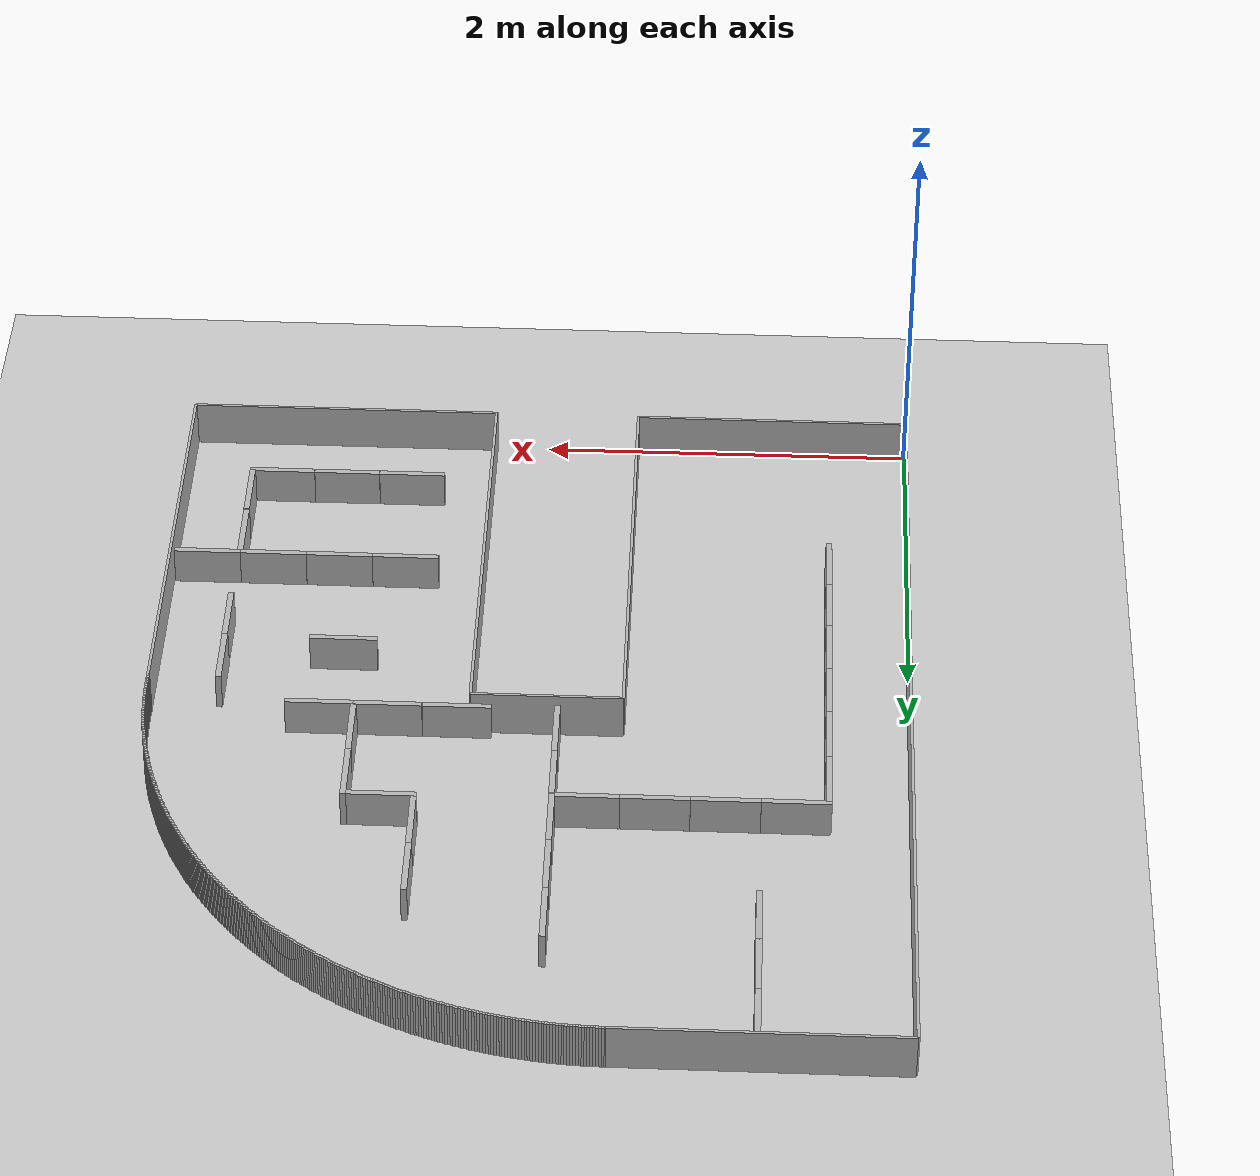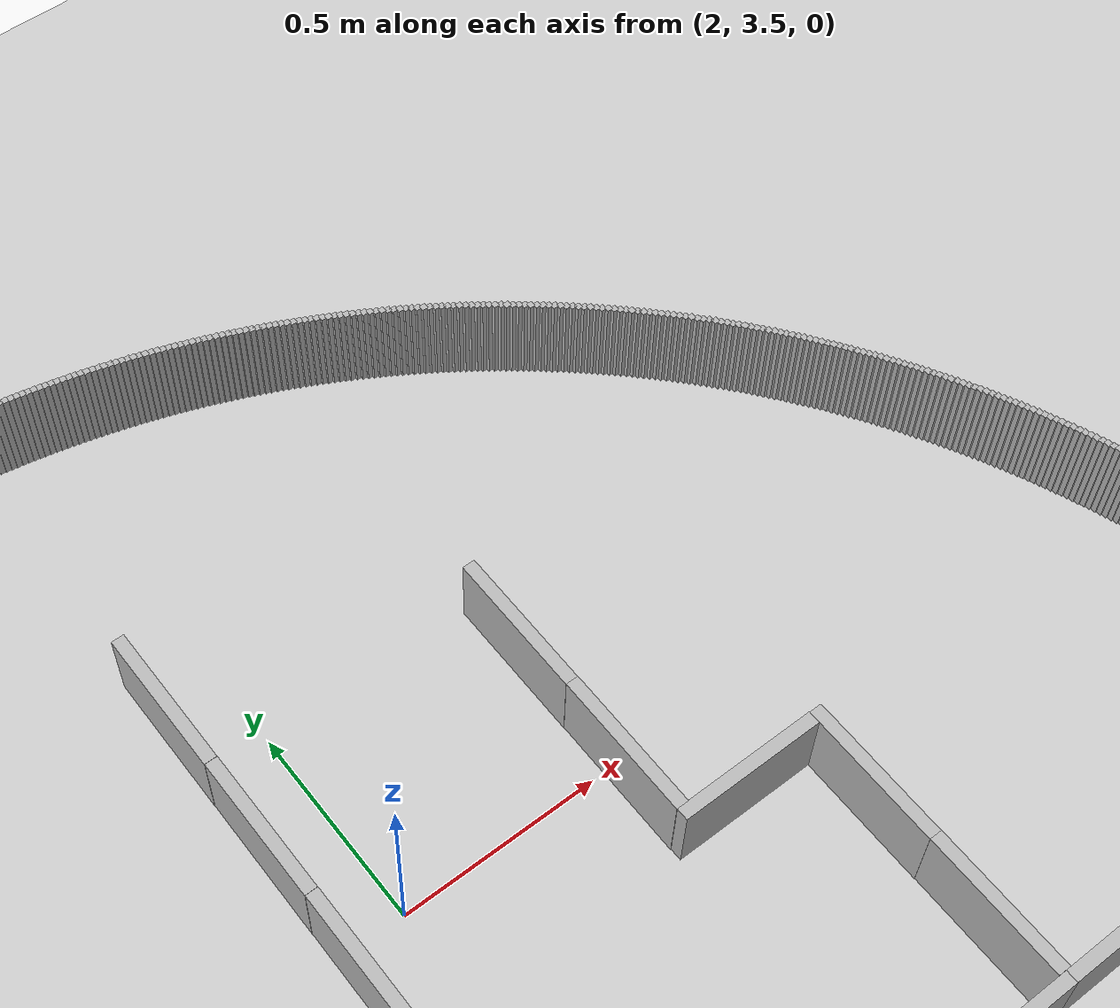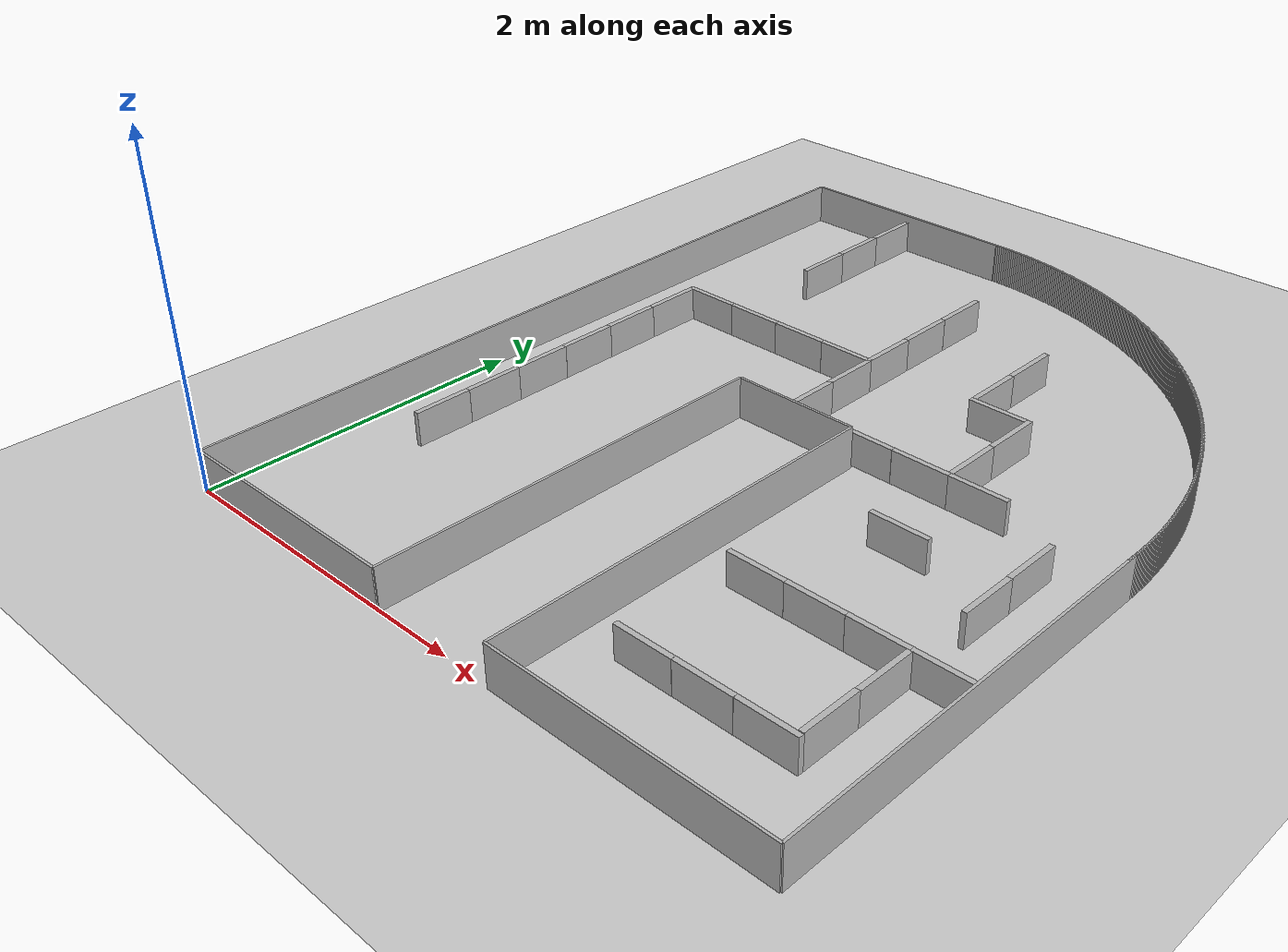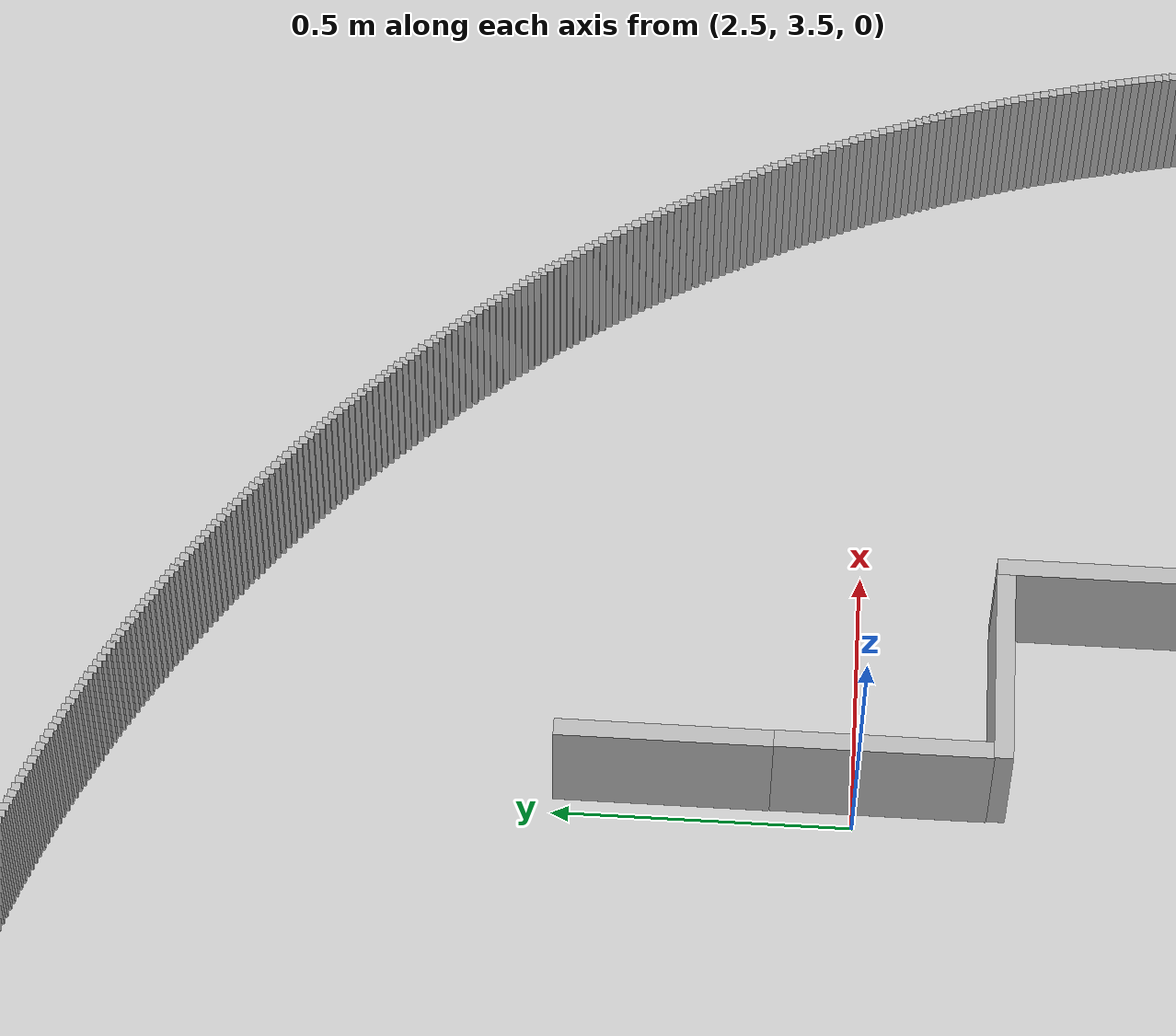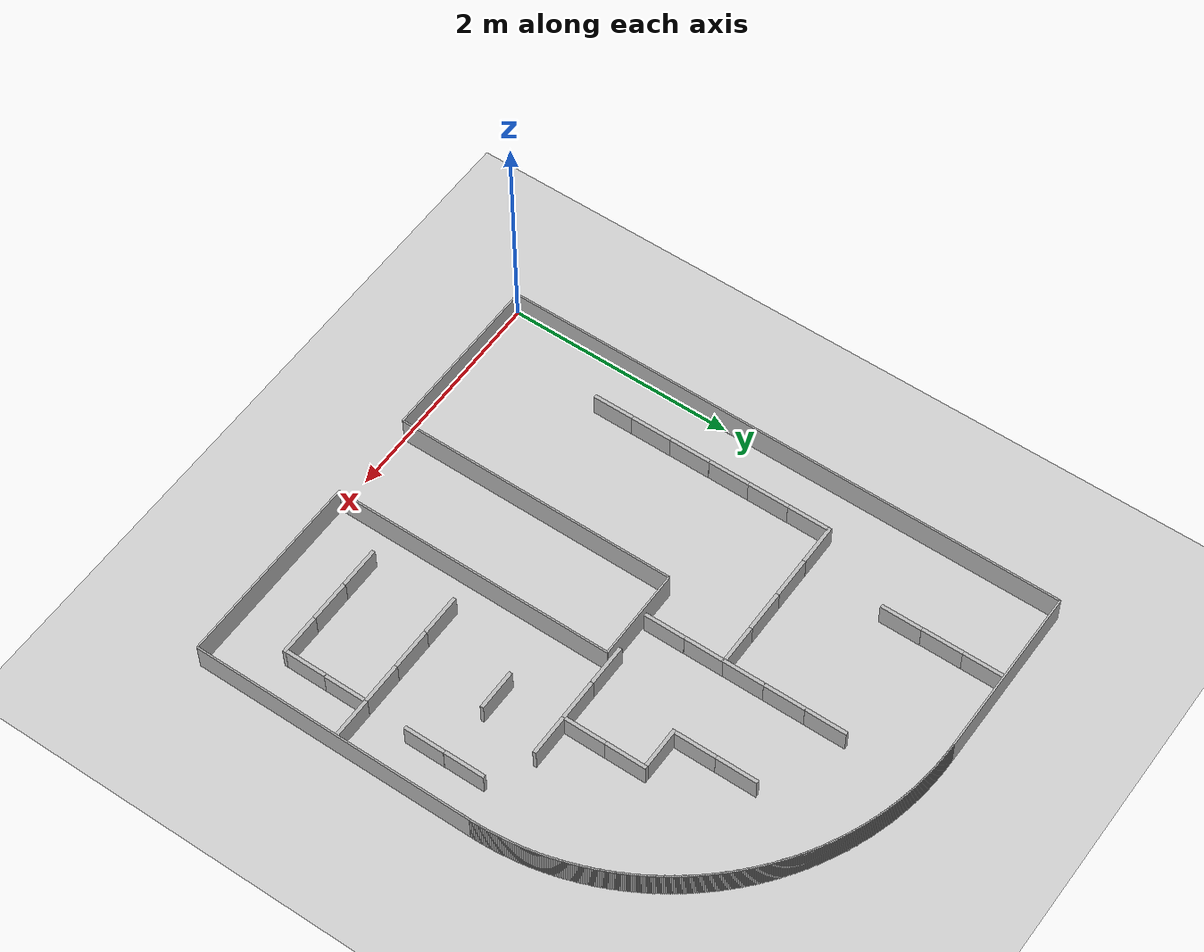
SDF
<?xml version='1.0'?>
<sdf version='1.6'>
  <world name='base'>
    <light name='sun' type='directional'>
      <cast_shadows>1</cast_shadows>
      <pose>0 0 10 0 -0 0</pose>
      <diffuse>0.8 0.8 0.8 1</diffuse>
      <specular>0.2 0.2 0.2 1</specular>
      <attenuation>
        <range>1000</range>
        <constant>0.9</constant>
        <linear>0.01</linear>
        <quadratic>0.001</quadratic>
      </attenuation>
      <direction>-0.5 0.1 -0.9</direction>
      <spot>
        <inner_angle>0</inner_angle>
        <outer_angle>0</outer_angle>
        <falloff>0</falloff>
      </spot>
    </light>
    <model name='ground_plane'>
      <static>1</static>
      <link name='link'>
        <collision name='collision'>
          <geometry>
            <plane>
              <normal>0 0 1</normal>
              <size>100 100</size>
            </plane>
          </geometry>
          <surface>
            <contact>
              <collide_bitmask>65535</collide_bitmask>
              <ode/>
            </contact>
            <friction>
              <ode>
                <mu>100</mu>
                <mu2>50</mu2>
              </ode>
              <torsional>
                <ode/>
              </torsional>
            </friction>
            <bounce/>
          </surface>
          <max_contacts>10</max_contacts>
        </collision>
        <visual name='visual'>
          <cast_shadows>0</cast_shadows>
          <geometry>
            <plane>
              <normal>0 0 1</normal>
              <size>100 100</size>
            </plane>
          </geometry>
          <material>
            <script>
              <uri>file://media/materials/scripts/gazebo.material</uri>
              <name>Gazebo/Grey</name>
            </script>
          </material>
        </visual>
        <self_collide>0</self_collide>
        <enable_wind>0</enable_wind>
        <kinematic>0</kinematic>
      </link>
    </model>
    <model name='k404'>
      <pose>0 0 0 0 -0 0</pose>
      <link name='0_link'>
        <collision name='collision_0'>
          <pose>0.75 5 0 0 -0 0</pose>
          <geometry>
            <box>
              <size>1.5 0.015 0.5</size>
            </box>
          </geometry>
          <max_contacts>10</max_contacts>
          <surface>
            <contact>
              <ode/>
            </contact>
            <bounce/>
            <friction>
              <torsional>
                <ode/>
              </torsional>
              <ode/>
            </friction>
          </surface>
        </collision>
        <visual name='visual_0'>
          <pose>0.75 5 0 0 -0 0</pose>
          <geometry>
            <box>
              <size>1.5 0.015 0.5</size>
            </box>
          </geometry>
        </visual>
        <self_collide>0</self_collide>
        <enable_wind>0</enable_wind>
        <kinematic>0</kinematic>
      </link>
      <link name='1_link'>
        <collision name='collision_1'>
          <pose>0 2.5 0 0 -0 0</pose>
          <geometry>
            <box>
              <size>0.015 5 0.5</size>
            </box>
          </geometry>
          <max_contacts>10</max_contacts>
          <surface>
            <contact>
              <ode/>
            </contact>
            <bounce/>
            <friction>
              <torsional>
                <ode/>
              </torsional>
              <ode/>
            </friction>
          </surface>
        </collision>
        <visual name='visual_1'>
          <pose>0 2.5 0 0 -0 0</pose>
          <geometry>
            <box>
              <size>0.015 5 0.5</size>
            </box>
          </geometry>
        </visual>
        <self_collide>0</self_collide>
        <enable_wind>0</enable_wind>
        <kinematic>0</kinematic>
      </link>
      <link name='2_link'>
        <collision name='collision_2'>
          <pose>0.75 0 0 0 -0 0</pose>
          <geometry>
            <box>
              <size>1.5 0.015 0.5</size>
            </box>
          </geometry>
          <max_contacts>10</max_contacts>
          <surface>
            <contact>
              <ode/>
            </contact>
            <bounce/>
            <friction>
              <torsional>
                <ode/>
              </torsional>
              <ode/>
            </friction>
          </surface>
        </collision>
        <visual name='visual_2'>
          <pose>0.75 0 0 0 -0 0</pose>
          <geometry>
            <box>
              <size>1.5 0.015 0.5</size>
            </box>
          </geometry>
        </visual>
        <self_collide>0</self_collide>
        <enable_wind>0</enable_wind>
        <kinematic>0</kinematic>
      </link>
      <link name='3_link'>
        <collision name='collision_3'>
          <pose>1.5 1.25 0 0 -0 0</pose>
          <geometry>
            <box>
              <size>0.015 2.5 0.5</size>
            </box>
          </geometry>
          <max_contacts>10</max_contacts>
          <surface>
            <contact>
              <ode/>
            </contact>
            <bounce/>
            <friction>
              <torsional>
                <ode/>
              </torsional>
              <ode/>
            </friction>
          </surface>
        </collision>
        <visual name='visual_3'>
          <pose>1.5 1.25 0 0 -0 0</pose>
          <geometry>
            <box>
              <size>0.015 2.5 0.5</size>
            </box>
          </geometry>
        </visual>
        <self_collide>0</self_collide>
        <enable_wind>0</enable_wind>
        <kinematic>0</kinematic>
      </link>
      <link name='4_link'>
        <collision name='collision_4'>
          <pose>1.9 2.5 0 0 -0 0</pose>
          <geometry>
            <box>
              <size>0.8 0.015 0.5</size>
            </box>
          </geometry>
          <max_contacts>10</max_contacts>
          <surface>
            <contact>
              <ode/>
            </contact>
            <bounce/>
            <friction>
              <torsional>
                <ode/>
              </torsional>
              <ode/>
            </friction>
          </surface>
        </collision>
        <visual name='visual_4'>
          <pose>1.9 2.5 0 0 -0 0</pose>
          <geometry>
            <box>
              <size>0.8 0.015 0.5</size>
            </box>
          </geometry>
        </visual>
        <self_collide>0</self_collide>
        <enable_wind>0</enable_wind>
        <kinematic>0</kinematic>
      </link>
      <link name='5_link'>
        <collision name='collision_5'>
          <pose>2.3 1.25 0 0 -0 0</pose>
          <geometry>
            <box>
              <size>0.015 2.5 0.5</size>
            </box>
          </geometry>
          <max_contacts>10</max_contacts>
          <surface>
            <contact>
              <ode/>
            </contact>
            <bounce/>
            <friction>
              <torsional>
                <ode/>
              </torsional>
              <ode/>
            </friction>
          </surface>
        </collision>
        <visual name='visual_5'>
          <pose>2.3 1.25 0 0 -0 0</pose>
          <geometry>
            <box>
              <size>0.015 2.5 0.5</size>
            </box>
          </geometry>
        </visual>
        <self_collide>0</self_collide>
        <enable_wind>0</enable_wind>
        <kinematic>0</kinematic>
      </link>
      <link name='6_link'>
        <collision name='collision_6'>
          <pose>3.15 0 0 0 -0 0</pose>
          <geometry>
            <box>
              <size>1.7 0.015 0.5</size>
            </box>
          </geometry>
          <max_contacts>10</max_contacts>
          <surface>
            <contact>
              <ode/>
            </contact>
            <bounce/>
            <friction>
              <torsional>
                <ode/>
              </torsional>
              <ode/>
            </friction>
          </surface>
        </collision>
        <visual name='visual_6'>
          <pose>3.15 0 0 0 -0 0</pose>
          <geometry>
            <box>
              <size>1.7 0.015 0.5</size>
            </box>
          </geometry>
        </visual>
        <self_collide>0</self_collide>
        <enable_wind>0</enable_wind>
        <kinematic>0</kinematic>
      </link>
      <link name='7_link'>
        <collision name='collision_7'>
          <pose>4 1.25 0 0 -0 0</pose>
          <geometry>
            <box>
              <size>0.015 2.5 0.5</size>
            </box>
          </geometry>
          <max_contacts>10</max_contacts>
          <surface>
            <contact>
              <ode/>
            </contact>
            <bounce/>
            <friction>
              <torsional>
                <ode/>
              </torsional>
              <ode/>
            </friction>
          </surface>
        </collision>
        <visual name='visual_7'>
          <pose>4 1.25 0 0 -0 0</pose>
          <geometry>
            <box>
              <size>0.015 2.5 0.5</size>
            </box>
          </geometry>
        </visual>
        <self_collide>0</self_collide>
        <enable_wind>0</enable_wind>
        <kinematic>0</kinematic>
      </link>
      <link name='8_link'>
        <collision name='collision_8'>
          <pose>1.5 5 0 0 -0 0</pose>
          <geometry>
            <box>
              <size>0.015 0.015 0.5</size>
            </box>
          </geometry>
          <max_contacts>10</max_contacts>
          <surface>
            <contact>
              <ode/>
            </contact>
            <bounce/>
            <friction>
              <torsional>
                <ode/>
              </torsional>
              <ode/>
            </friction>
          </surface>
        </collision>
        <visual name='visual_8'>
          <pose>1.5 5 0 0 -0 0</pose>
          <geometry>
            <box>
              <size>0.015 0.015 0.5</size>
            </box>
          </geometry>
        </visual>
        <self_collide>0</self_collide>
        <enable_wind>0</enable_wind>
        <kinematic>0</kinematic>
      </link>
      <link name='9_link'>
        <collision name='collision_9'>
          <pose>1.51389 4.99996 0 0 -0 0</pose>
          <geometry>
            <box>
              <size>0.015 0.015 0.5</size>
            </box>
          </geometry>
          <max_contacts>10</max_contacts>
          <surface>
            <contact>
              <ode/>
            </contact>
            <bounce/>
            <friction>
              <torsional>
                <ode/>
              </torsional>
              <ode/>
            </friction>
          </surface>
        </collision>
        <visual name='visual_9'>
          <pose>1.51389 4.99996 0 0 -0 0</pose>
          <geometry>
            <box>
              <size>0.015 0.015 0.5</size>
            </box>
          </geometry>
        </visual>
        <self_collide>0</self_collide>
        <enable_wind>0</enable_wind>
        <kinematic>0</kinematic>
      </link>
      <link name='10_link'>
        <collision name='collision_10'>
          <pose>1.52778 4.99985 0 0 -0 0</pose>
          <geometry>
            <box>
              <size>0.015 0.015 0.5</size>
            </box>
          </geometry>
          <max_contacts>10</max_contacts>
          <surface>
            <contact>
              <ode/>
            </contact>
            <bounce/>
            <friction>
              <torsional>
                <ode/>
              </torsional>
              <ode/>
            </friction>
          </surface>
        </collision>
        <visual name='visual_10'>
          <pose>1.52778 4.99985 0 0 -0 0</pose>
          <geometry>
            <box>
              <size>0.015 0.015 0.5</size>
            </box>
          </geometry>
        </visual>
        <self_collide>0</self_collide>
        <enable_wind>0</enable_wind>
        <kinematic>0</kinematic>
      </link>
      <link name='11_link'>
        <collision name='collision_11'>
          <pose>1.54167 4.99965 0 0 -0 0</pose>
          <geometry>
            <box>
              <size>0.015 0.015 0.5</size>
            </box>
          </geometry>
          <max_contacts>10</max_contacts>
          <surface>
            <contact>
              <ode/>
            </contact>
            <bounce/>
            <friction>
              <torsional>
                <ode/>
              </torsional>
              <ode/>
            </friction>
          </surface>
        </collision>
        <visual name='visual_11'>
          <pose>1.54167 4.99965 0 0 -0 0</pose>
          <geometry>
            <box>
              <size>0.015 0.015 0.5</size>
            </box>
          </geometry>
        </visual>
        <self_collide>0</self_collide>
        <enable_wind>0</enable_wind>
        <kinematic>0</kinematic>
      </link>
      <link name='12_link'>
        <collision name='collision_12'>
          <pose>1.55555 4.99938 0 0 -0 0</pose>
          <geometry>
            <box>
              <size>0.015 0.015 0.5</size>
            </box>
          </geometry>
          <max_contacts>10</max_contacts>
          <surface>
            <contact>
              <ode/>
            </contact>
            <bounce/>
            <friction>
              <torsional>
                <ode/>
              </torsional>
              <ode/>
            </friction>
          </surface>
        </collision>
        <visual name='visual_12'>
          <pose>1.55555 4.99938 0 0 -0 0</pose>
          <geometry>
            <box>
              <size>0.015 0.015 0.5</size>
            </box>
          </geometry>
        </visual>
        <self_collide>0</self_collide>
        <enable_wind>0</enable_wind>
        <kinematic>0</kinematic>
      </link>
      <link name='13_link'>
        <collision name='collision_13'>
          <pose>1.56944 4.99904 0 0 -0 0</pose>
          <geometry>
            <box>
              <size>0.015 0.015 0.5</size>
            </box>
          </geometry>
          <max_contacts>10</max_contacts>
          <surface>
            <contact>
              <ode/>
            </contact>
            <bounce/>
            <friction>
              <torsional>
                <ode/>
              </torsional>
              <ode/>
            </friction>
          </surface>
        </collision>
        <visual name='visual_13'>
          <pose>1.56944 4.99904 0 0 -0 0</pose>
          <geometry>
            <box>
              <size>0.015 0.015 0.5</size>
            </box>
          </geometry>
        </visual>
        <self_collide>0</self_collide>
        <enable_wind>0</enable_wind>
        <kinematic>0</kinematic>
      </link>
      <link name='14_link'>
        <collision name='collision_14'>
          <pose>1.58332 4.99861 0 0 -0 0</pose>
          <geometry>
            <box>
              <size>0.015 0.015 0.5</size>
            </box>
          </geometry>
          <max_contacts>10</max_contacts>
          <surface>
            <contact>
              <ode/>
            </contact>
            <bounce/>
            <friction>
              <torsional>
                <ode/>
              </torsional>
              <ode/>
            </friction>
          </surface>
        </collision>
        <visual name='visual_14'>
          <pose>1.58332 4.99861 0 0 -0 0</pose>
          <geometry>
            <box>
              <size>0.015 0.015 0.5</size>
            </box>
          </geometry>
        </visual>
        <self_collide>0</self_collide>
        <enable_wind>0</enable_wind>
        <kinematic>0</kinematic>
      </link>
      <link name='15_link'>
        <collision name='collision_15'>
          <pose>1.5972 4.99811 0 0 -0 0</pose>
          <geometry>
            <box>
              <size>0.015 0.015 0.5</size>
            </box>
          </geometry>
          <max_contacts>10</max_contacts>
          <surface>
            <contact>
              <ode/>
            </contact>
            <bounce/>
            <friction>
              <torsional>
                <ode/>
              </torsional>
              <ode/>
            </friction>
          </surface>
        </collision>
        <visual name='visual_15'>
          <pose>1.5972 4.99811 0 0 -0 0</pose>
          <geometry>
            <box>
              <size>0.015 0.015 0.5</size>
            </box>
          </geometry>
        </visual>
        <self_collide>0</self_collide>
        <enable_wind>0</enable_wind>
        <kinematic>0</kinematic>
      </link>
      <link name='16_link'>
        <collision name='collision_16'>
          <pose>1.61108 4.99753 0 0 -0 0</pose>
          <geometry>
            <box>
              <size>0.015 0.015 0.5</size>
            </box>
          </geometry>
          <max_contacts>10</max_contacts>
          <surface>
            <contact>
              <ode/>
            </contact>
            <bounce/>
            <friction>
              <torsional>
                <ode/>
              </torsional>
              <ode/>
            </friction>
          </surface>
        </collision>
        <visual name='visual_16'>
          <pose>1.61108 4.99753 0 0 -0 0</pose>
          <geometry>
            <box>
              <size>0.015 0.015 0.5</size>
            </box>
          </geometry>
        </visual>
        <self_collide>0</self_collide>
        <enable_wind>0</enable_wind>
        <kinematic>0</kinematic>
      </link>
      <link name='17_link'>
        <collision name='collision_17'>
          <pose>1.62495 4.99688 0 0 -0 0</pose>
          <geometry>
            <box>
              <size>0.015 0.015 0.5</size>
            </box>
          </geometry>
          <max_contacts>10</max_contacts>
          <surface>
            <contact>
              <ode/>
            </contact>
            <bounce/>
            <friction>
              <torsional>
                <ode/>
              </torsional>
              <ode/>
            </friction>
          </surface>
        </collision>
        <visual name='visual_17'>
          <pose>1.62495 4.99688 0 0 -0 0</pose>
          <geometry>
            <box>
              <size>0.015 0.015 0.5</size>
            </box>
          </geometry>
        </visual>
        <self_collide>0</self_collide>
        <enable_wind>0</enable_wind>
        <kinematic>0</kinematic>
      </link>
      <link name='18_link'>
        <collision name='collision_18'>
          <pose>1.63882 4.99614 0 0 -0 0</pose>
          <geometry>
            <box>
              <size>0.015 0.015 0.5</size>
            </box>
          </geometry>
          <max_contacts>10</max_contacts>
          <surface>
            <contact>
              <ode/>
            </contact>
            <bounce/>
            <friction>
              <torsional>
                <ode/>
              </torsional>
              <ode/>
            </friction>
          </surface>
        </collision>
        <visual name='visual_18'>
          <pose>1.63882 4.99614 0 0 -0 0</pose>
          <geometry>
            <box>
              <size>0.015 0.015 0.5</size>
            </box>
          </geometry>
        </visual>
        <self_collide>0</self_collide>
        <enable_wind>0</enable_wind>
        <kinematic>0</kinematic>
      </link>
      <link name='19_link'>
        <collision name='collision_19'>
          <pose>1.65268 4.99533 0 0 -0 0</pose>
          <geometry>
            <box>
              <size>0.015 0.015 0.5</size>
            </box>
          </geometry>
          <max_contacts>10</max_contacts>
          <surface>
            <contact>
              <ode/>
            </contact>
            <bounce/>
            <friction>
              <torsional>
                <ode/>
              </torsional>
              <ode/>
            </friction>
          </surface>
        </collision>
        <visual name='visual_19'>
          <pose>1.65268 4.99533 0 0 -0 0</pose>
          <geometry>
            <box>
              <size>0.015 0.015 0.5</size>
            </box>
          </geometry>
        </visual>
        <self_collide>0</self_collide>
        <enable_wind>0</enable_wind>
        <kinematic>0</kinematic>
      </link>
      <link name='20_link'>
        <collision name='collision_20'>
          <pose>1.66654 4.99445 0 0 -0 0</pose>
          <geometry>
            <box>
              <size>0.015 0.015 0.5</size>
            </box>
          </geometry>
          <max_contacts>10</max_contacts>
          <surface>
            <contact>
              <ode/>
            </contact>
            <bounce/>
            <friction>
              <torsional>
                <ode/>
              </torsional>
              <ode/>
            </friction>
          </surface>
        </collision>
        <visual name='visual_20'>
          <pose>1.66654 4.99445 0 0 -0 0</pose>
          <geometry>
            <box>
              <size>0.015 0.015 0.5</size>
            </box>
          </geometry>
        </visual>
        <self_collide>0</self_collide>
        <enable_wind>0</enable_wind>
        <kinematic>0</kinematic>
      </link>
      <link name='21_link'>
        <collision name='collision_21'>
          <pose>1.6804 4.99348 0 0 -0 0</pose>
          <geometry>
            <box>
              <size>0.015 0.015 0.5</size>
            </box>
          </geometry>
          <max_contacts>10</max_contacts>
          <surface>
            <contact>
              <ode/>
            </contact>
            <bounce/>
            <friction>
              <torsional>
                <ode/>
              </torsional>
              <ode/>
            </friction>
          </surface>
        </collision>
        <visual name='visual_21'>
          <pose>1.6804 4.99348 0 0 -0 0</pose>
          <geometry>
            <box>
              <size>0.015 0.015 0.5</size>
            </box>
          </geometry>
        </visual>
        <self_collide>0</self_collide>
        <enable_wind>0</enable_wind>
        <kinematic>0</kinematic>
      </link>
      <link name='22_link'>
        <collision name='collision_22'>
          <pose>1.69425 4.99244 0 0 -0 0</pose>
          <geometry>
            <box>
              <size>0.015 0.015 0.5</size>
            </box>
          </geometry>
          <max_contacts>10</max_contacts>
          <surface>
            <contact>
              <ode/>
            </contact>
            <bounce/>
            <friction>
              <torsional>
                <ode/>
              </torsional>
              <ode/>
            </friction>
          </surface>
        </collision>
        <visual name='visual_22'>
          <pose>1.69425 4.99244 0 0 -0 0</pose>
          <geometry>
            <box>
              <size>0.015 0.015 0.5</size>
            </box>
          </geometry>
        </visual>
        <self_collide>0</self_collide>
        <enable_wind>0</enable_wind>
        <kinematic>0</kinematic>
      </link>
      <link name='23_link'>
        <collision name='collision_23'>
          <pose>1.70809 4.99132 0 0 -0 0</pose>
          <geometry>
            <box>
              <size>0.015 0.015 0.5</size>
            </box>
          </geometry>
          <max_contacts>10</max_contacts>
          <surface>
            <contact>
              <ode/>
            </contact>
            <bounce/>
            <friction>
              <torsional>
                <ode/>
              </torsional>
              <ode/>
            </friction>
          </surface>
        </collision>
        <visual name='visual_23'>
          <pose>1.70809 4.99132 0 0 -0 0</pose>
          <geometry>
            <box>
              <size>0.015 0.015 0.5</size>
            </box>
          </geometry>
        </visual>
        <self_collide>0</self_collide>
        <enable_wind>0</enable_wind>
        <kinematic>0</kinematic>
      </link>
      <link name='24_link'>
        <collision name='collision_24'>
          <pose>1.72193 4.99013 0 0 -0 0</pose>
          <geometry>
            <box>
              <size>0.015 0.015 0.5</size>
            </box>
          </geometry>
          <max_contacts>10</max_contacts>
          <surface>
            <contact>
              <ode/>
            </contact>
            <bounce/>
            <friction>
              <torsional>
                <ode/>
              </torsional>
              <ode/>
            </friction>
          </surface>
        </collision>
        <visual name='visual_24'>
          <pose>1.72193 4.99013 0 0 -0 0</pose>
          <geometry>
            <box>
              <size>0.015 0.015 0.5</size>
            </box>
          </geometry>
        </visual>
        <self_collide>0</self_collide>
        <enable_wind>0</enable_wind>
        <kinematic>0</kinematic>
      </link>
      <link name='25_link'>
        <collision name='collision_25'>
          <pose>1.73576 4.98886 0 0 -0 0</pose>
          <geometry>
            <box>
              <size>0.015 0.015 0.5</size>
            </box>
          </geometry>
          <max_contacts>10</max_contacts>
          <surface>
            <contact>
              <ode/>
            </contact>
            <bounce/>
            <friction>
              <torsional>
                <ode/>
              </torsional>
              <ode/>
            </friction>
          </surface>
        </collision>
        <visual name='visual_25'>
          <pose>1.73576 4.98886 0 0 -0 0</pose>
          <geometry>
            <box>
              <size>0.015 0.015 0.5</size>
            </box>
          </geometry>
        </visual>
        <self_collide>0</self_collide>
        <enable_wind>0</enable_wind>
        <kinematic>0</kinematic>
      </link>
      <link name='26_link'>
        <collision name='collision_26'>
          <pose>1.74958 4.98751 0 0 -0 0</pose>
          <geometry>
            <box>
              <size>0.015 0.015 0.5</size>
            </box>
          </geometry>
          <max_contacts>10</max_contacts>
          <surface>
            <contact>
              <ode/>
            </contact>
            <bounce/>
            <friction>
              <torsional>
                <ode/>
              </torsional>
              <ode/>
            </friction>
          </surface>
        </collision>
        <visual name='visual_26'>
          <pose>1.74958 4.98751 0 0 -0 0</pose>
          <geometry>
            <box>
              <size>0.015 0.015 0.5</size>
            </box>
          </geometry>
        </visual>
        <self_collide>0</self_collide>
        <enable_wind>0</enable_wind>
        <kinematic>0</kinematic>
      </link>
      <link name='27_link'>
        <collision name='collision_27'>
          <pose>1.7634 4.98609 0 0 -0 0</pose>
          <geometry>
            <box>
              <size>0.015 0.015 0.5</size>
            </box>
          </geometry>
          <max_contacts>10</max_contacts>
          <surface>
            <contact>
              <ode/>
            </contact>
            <bounce/>
            <friction>
              <torsional>
                <ode/>
              </torsional>
              <ode/>
            </friction>
          </surface>
        </collision>
        <visual name='visual_27'>
          <pose>1.7634 4.98609 0 0 -0 0</pose>
          <geometry>
            <box>
              <size>0.015 0.015 0.5</size>
            </box>
          </geometry>
        </visual>
        <self_collide>0</self_collide>
        <enable_wind>0</enable_wind>
        <kinematic>0</kinematic>
      </link>
      <link name='28_link'>
        <collision name='collision_28'>
          <pose>1.77721 4.98458 0 0 -0 0</pose>
          <geometry>
            <box>
              <size>0.015 0.015 0.5</size>
            </box>
          </geometry>
          <max_contacts>10</max_contacts>
          <surface>
            <contact>
              <ode/>
            </contact>
            <bounce/>
            <friction>
              <torsional>
                <ode/>
              </torsional>
              <ode/>
            </friction>
          </surface>
        </collision>
        <visual name='visual_28'>
          <pose>1.77721 4.98458 0 0 -0 0</pose>
          <geometry>
            <box>
              <size>0.015 0.015 0.5</size>
            </box>
          </geometry>
        </visual>
        <self_collide>0</self_collide>
        <enable_wind>0</enable_wind>
        <kinematic>0</kinematic>
      </link>
      <link name='29_link'>
        <collision name='collision_29'>
          <pose>1.791 4.98301 0 0 -0 0</pose>
          <geometry>
            <box>
              <size>0.015 0.015 0.5</size>
            </box>
          </geometry>
          <max_contacts>10</max_contacts>
          <surface>
            <contact>
              <ode/>
            </contact>
            <bounce/>
            <friction>
              <torsional>
                <ode/>
              </torsional>
              <ode/>
            </friction>
          </surface>
        </collision>
        <visual name='visual_29'>
          <pose>1.791 4.98301 0 0 -0 0</pose>
          <geometry>
            <box>
              <size>0.015 0.015 0.5</size>
            </box>
          </geometry>
        </visual>
        <self_collide>0</self_collide>
        <enable_wind>0</enable_wind>
        <kinematic>0</kinematic>
      </link>
      <link name='30_link'>
        <collision name='collision_30'>
          <pose>1.80479 4.98135 0 0 -0 0</pose>
          <geometry>
            <box>
              <size>0.015 0.015 0.5</size>
            </box>
          </geometry>
          <max_contacts>10</max_contacts>
          <surface>
            <contact>
              <ode/>
            </contact>
            <bounce/>
            <friction>
              <torsional>
                <ode/>
              </torsional>
              <ode/>
            </friction>
          </surface>
        </collision>
        <visual name='visual_30'>
          <pose>1.80479 4.98135 0 0 -0 0</pose>
          <geometry>
            <box>
              <size>0.015 0.015 0.5</size>
            </box>
          </geometry>
        </visual>
        <self_collide>0</self_collide>
        <enable_wind>0</enable_wind>
        <kinematic>0</kinematic>
      </link>
      <link name='31_link'>
        <collision name='collision_31'>
          <pose>1.81858 4.97962 0 0 -0 0</pose>
          <geometry>
            <box>
              <size>0.015 0.015 0.5</size>
            </box>
          </geometry>
          <max_contacts>10</max_contacts>
          <surface>
            <contact>
              <ode/>
            </contact>
            <bounce/>
            <friction>
              <torsional>
                <ode/>
              </torsional>
              <ode/>
            </friction>
          </surface>
        </collision>
        <visual name='visual_31'>
          <pose>1.81858 4.97962 0 0 -0 0</pose>
          <geometry>
            <box>
              <size>0.015 0.015 0.5</size>
            </box>
          </geometry>
        </visual>
        <self_collide>0</self_collide>
        <enable_wind>0</enable_wind>
        <kinematic>0</kinematic>
      </link>
      <link name='32_link'>
        <collision name='collision_32'>
          <pose>1.83235 4.97781 0 0 -0 0</pose>
          <geometry>
            <box>
              <size>0.015 0.015 0.5</size>
            </box>
          </geometry>
          <max_contacts>10</max_contacts>
          <surface>
            <contact>
              <ode/>
            </contact>
            <bounce/>
            <friction>
              <torsional>
                <ode/>
              </torsional>
              <ode/>
            </friction>
          </surface>
        </collision>
        <visual name='visual_32'>
          <pose>1.83235 4.97781 0 0 -0 0</pose>
          <geometry>
            <box>
              <size>0.015 0.015 0.5</size>
            </box>
          </geometry>
        </visual>
        <self_collide>0</self_collide>
        <enable_wind>0</enable_wind>
        <kinematic>0</kinematic>
      </link>
      <link name='33_link'>
        <collision name='collision_33'>
          <pose>1.84611 4.97593 0 0 -0 0</pose>
          <geometry>
            <box>
              <size>0.015 0.015 0.5</size>
            </box>
          </geometry>
          <max_contacts>10</max_contacts>
          <surface>
            <contact>
              <ode/>
            </contact>
            <bounce/>
            <friction>
              <torsional>
                <ode/>
              </torsional>
              <ode/>
            </friction>
          </surface>
        </collision>
        <visual name='visual_33'>
          <pose>1.84611 4.97593 0 0 -0 0</pose>
          <geometry>
            <box>
              <size>0.015 0.015 0.5</size>
            </box>
          </geometry>
        </visual>
        <self_collide>0</self_collide>
        <enable_wind>0</enable_wind>
        <kinematic>0</kinematic>
      </link>
      <link name='34_link'>
        <collision name='collision_34'>
          <pose>1.85986 4.97396 0 0 -0 0</pose>
          <geometry>
            <box>
              <size>0.015 0.015 0.5</size>
            </box>
          </geometry>
          <max_contacts>10</max_contacts>
          <surface>
            <contact>
              <ode/>
            </contact>
            <bounce/>
            <friction>
              <torsional>
                <ode/>
              </torsional>
              <ode/>
            </friction>
          </surface>
        </collision>
        <visual name='visual_34'>
          <pose>1.85986 4.97396 0 0 -0 0</pose>
          <geometry>
            <box>
              <size>0.015 0.015 0.5</size>
            </box>
          </geometry>
        </visual>
        <self_collide>0</self_collide>
        <enable_wind>0</enable_wind>
        <kinematic>0</kinematic>
      </link>
      <link name='35_link'>
        <collision name='collision_35'>
          <pose>1.87359 4.97193 0 0 -0 0</pose>
          <geometry>
            <box>
              <size>0.015 0.015 0.5</size>
            </box>
          </geometry>
          <max_contacts>10</max_contacts>
          <surface>
            <contact>
              <ode/>
            </contact>
            <bounce/>
            <friction>
              <torsional>
                <ode/>
              </torsional>
              <ode/>
            </friction>
          </surface>
        </collision>
        <visual name='visual_35'>
          <pose>1.87359 4.97193 0 0 -0 0</pose>
          <geometry>
            <box>
              <size>0.015 0.015 0.5</size>
            </box>
          </geometry>
        </visual>
        <self_collide>0</self_collide>
        <enable_wind>0</enable_wind>
        <kinematic>0</kinematic>
      </link>
      <link name='36_link'>
        <collision name='collision_36'>
          <pose>1.88732 4.96981 0 0 -0 0</pose>
          <geometry>
            <box>
              <size>0.015 0.015 0.5</size>
            </box>
          </geometry>
          <max_contacts>10</max_contacts>
          <surface>
            <contact>
              <ode/>
            </contact>
            <bounce/>
            <friction>
              <torsional>
                <ode/>
              </torsional>
              <ode/>
            </friction>
          </surface>
        </collision>
        <visual name='visual_36'>
          <pose>1.88732 4.96981 0 0 -0 0</pose>
          <geometry>
            <box>
              <size>0.015 0.015 0.5</size>
            </box>
          </geometry>
        </visual>
        <self_collide>0</self_collide>
        <enable_wind>0</enable_wind>
        <kinematic>0</kinematic>
      </link>
      <link name='37_link'>
        <collision name='collision_37'>
          <pose>1.90104 4.96762 0 0 -0 0</pose>
          <geometry>
            <box>
              <size>0.015 0.015 0.5</size>
            </box>
          </geometry>
          <max_contacts>10</max_contacts>
          <surface>
            <contact>
              <ode/>
            </contact>
            <bounce/>
            <friction>
              <torsional>
                <ode/>
              </torsional>
              <ode/>
            </friction>
          </surface>
        </collision>
        <visual name='visual_37'>
          <pose>1.90104 4.96762 0 0 -0 0</pose>
          <geometry>
            <box>
              <size>0.015 0.015 0.5</size>
            </box>
          </geometry>
        </visual>
        <self_collide>0</self_collide>
        <enable_wind>0</enable_wind>
        <kinematic>0</kinematic>
      </link>
      <link name='38_link'>
        <collision name='collision_38'>
          <pose>1.91474 4.96536 0 0 -0 0</pose>
          <geometry>
            <box>
              <size>0.015 0.015 0.5</size>
            </box>
          </geometry>
          <max_contacts>10</max_contacts>
          <surface>
            <contact>
              <ode/>
            </contact>
            <bounce/>
            <friction>
              <torsional>
                <ode/>
              </torsional>
              <ode/>
            </friction>
          </surface>
        </collision>
        <visual name='visual_38'>
          <pose>1.91474 4.96536 0 0 -0 0</pose>
          <geometry>
            <box>
              <size>0.015 0.015 0.5</size>
            </box>
          </geometry>
        </visual>
        <self_collide>0</self_collide>
        <enable_wind>0</enable_wind>
        <kinematic>0</kinematic>
      </link>
      <link name='39_link'>
        <collision name='collision_39'>
          <pose>1.92843 4.96302 0 0 -0 0</pose>
          <geometry>
            <box>
              <size>0.015 0.015 0.5</size>
            </box>
          </geometry>
          <max_contacts>10</max_contacts>
          <surface>
            <contact>
              <ode/>
            </contact>
            <bounce/>
            <friction>
              <torsional>
                <ode/>
              </torsional>
              <ode/>
            </friction>
          </surface>
        </collision>
        <visual name='visual_39'>
          <pose>1.92843 4.96302 0 0 -0 0</pose>
          <geometry>
            <box>
              <size>0.015 0.015 0.5</size>
            </box>
          </geometry>
        </visual>
        <self_collide>0</self_collide>
        <enable_wind>0</enable_wind>
        <kinematic>0</kinematic>
      </link>
      <link name='40_link'>
        <collision name='collision_40'>
          <pose>1.94211 4.9606 0 0 -0 0</pose>
          <geometry>
            <box>
              <size>0.015 0.015 0.5</size>
            </box>
          </geometry>
          <max_contacts>10</max_contacts>
          <surface>
            <contact>
              <ode/>
            </contact>
            <bounce/>
            <friction>
              <torsional>
                <ode/>
              </torsional>
              <ode/>
            </friction>
          </surface>
        </collision>
        <visual name='visual_40'>
          <pose>1.94211 4.9606 0 0 -0 0</pose>
          <geometry>
            <box>
              <size>0.015 0.015 0.5</size>
            </box>
          </geometry>
        </visual>
        <self_collide>0</self_collide>
        <enable_wind>0</enable_wind>
        <kinematic>0</kinematic>
      </link>
      <link name='41_link'>
        <collision name='collision_41'>
          <pose>1.95577 4.9581 0 0 -0 0</pose>
          <geometry>
            <box>
              <size>0.015 0.015 0.5</size>
            </box>
          </geometry>
          <max_contacts>10</max_contacts>
          <surface>
            <contact>
              <ode/>
            </contact>
            <bounce/>
            <friction>
              <torsional>
                <ode/>
              </torsional>
              <ode/>
            </friction>
          </surface>
        </collision>
        <visual name='visual_41'>
          <pose>1.95577 4.9581 0 0 -0 0</pose>
          <geometry>
            <box>
              <size>0.015 0.015 0.5</size>
            </box>
          </geometry>
        </visual>
        <self_collide>0</self_collide>
        <enable_wind>0</enable_wind>
        <kinematic>0</kinematic>
      </link>
      <link name='42_link'>
        <collision name='collision_42'>
          <pose>1.96942 4.95553 0 0 -0 0</pose>
          <geometry>
            <box>
              <size>0.015 0.015 0.5</size>
            </box>
          </geometry>
          <max_contacts>10</max_contacts>
          <surface>
            <contact>
              <ode/>
            </contact>
            <bounce/>
            <friction>
              <torsional>
                <ode/>
              </torsional>
              <ode/>
            </friction>
          </surface>
        </collision>
        <visual name='visual_42'>
          <pose>1.96942 4.95553 0 0 -0 0</pose>
          <geometry>
            <box>
              <size>0.015 0.015 0.5</size>
            </box>
          </geometry>
        </visual>
        <self_collide>0</self_collide>
        <enable_wind>0</enable_wind>
        <kinematic>0</kinematic>
      </link>
      <link name='43_link'>
        <collision name='collision_43'>
          <pose>1.98305 4.95289 0 0 -0 0</pose>
          <geometry>
            <box>
              <size>0.015 0.015 0.5</size>
            </box>
          </geometry>
          <max_contacts>10</max_contacts>
          <surface>
            <contact>
              <ode/>
            </contact>
            <bounce/>
            <friction>
              <torsional>
                <ode/>
              </torsional>
              <ode/>
            </friction>
          </surface>
        </collision>
        <visual name='visual_43'>
          <pose>1.98305 4.95289 0 0 -0 0</pose>
          <geometry>
            <box>
              <size>0.015 0.015 0.5</size>
            </box>
          </geometry>
        </visual>
        <self_collide>0</self_collide>
        <enable_wind>0</enable_wind>
        <kinematic>0</kinematic>
      </link>
      <link name='44_link'>
        <collision name='collision_44'>
          <pose>1.99667 4.95017 0 0 -0 0</pose>
          <geometry>
            <box>
              <size>0.015 0.015 0.5</size>
            </box>
          </geometry>
          <max_contacts>10</max_contacts>
          <surface>
            <contact>
              <ode/>
            </contact>
            <bounce/>
            <friction>
              <torsional>
                <ode/>
              </torsional>
              <ode/>
            </friction>
          </surface>
        </collision>
        <visual name='visual_44'>
          <pose>1.99667 4.95017 0 0 -0 0</pose>
          <geometry>
            <box>
              <size>0.015 0.015 0.5</size>
            </box>
          </geometry>
        </visual>
        <self_collide>0</self_collide>
        <enable_wind>0</enable_wind>
        <kinematic>0</kinematic>
      </link>
      <link name='45_link'>
        <collision name='collision_45'>
          <pose>2.01028 4.94737 0 0 -0 0</pose>
          <geometry>
            <box>
              <size>0.015 0.015 0.5</size>
            </box>
          </geometry>
          <max_contacts>10</max_contacts>
          <surface>
            <contact>
              <ode/>
            </contact>
            <bounce/>
            <friction>
              <torsional>
                <ode/>
              </torsional>
              <ode/>
            </friction>
          </surface>
        </collision>
        <visual name='visual_45'>
          <pose>2.01028 4.94737 0 0 -0 0</pose>
          <geometry>
            <box>
              <size>0.015 0.015 0.5</size>
            </box>
          </geometry>
        </visual>
        <self_collide>0</self_collide>
        <enable_wind>0</enable_wind>
        <kinematic>0</kinematic>
      </link>
      <link name='46_link'>
        <collision name='collision_46'>
          <pose>2.02387 4.9445 0 0 -0 0</pose>
          <geometry>
            <box>
              <size>0.015 0.015 0.5</size>
            </box>
          </geometry>
          <max_contacts>10</max_contacts>
          <surface>
            <contact>
              <ode/>
            </contact>
            <bounce/>
            <friction>
              <torsional>
                <ode/>
              </torsional>
              <ode/>
            </friction>
          </surface>
        </collision>
        <visual name='visual_46'>
          <pose>2.02387 4.9445 0 0 -0 0</pose>
          <geometry>
            <box>
              <size>0.015 0.015 0.5</size>
            </box>
          </geometry>
        </visual>
        <self_collide>0</self_collide>
        <enable_wind>0</enable_wind>
        <kinematic>0</kinematic>
      </link>
      <link name='47_link'>
        <collision name='collision_47'>
          <pose>2.03744 4.94155 0 0 -0 0</pose>
          <geometry>
            <box>
              <size>0.015 0.015 0.5</size>
            </box>
          </geometry>
          <max_contacts>10</max_contacts>
          <surface>
            <contact>
              <ode/>
            </contact>
            <bounce/>
            <friction>
              <torsional>
                <ode/>
              </torsional>
              <ode/>
            </friction>
          </surface>
        </collision>
        <visual name='visual_47'>
          <pose>2.03744 4.94155 0 0 -0 0</pose>
          <geometry>
            <box>
              <size>0.015 0.015 0.5</size>
            </box>
          </geometry>
        </visual>
        <self_collide>0</self_collide>
        <enable_wind>0</enable_wind>
        <kinematic>0</kinematic>
      </link>
      <link name='48_link'>
        <collision name='collision_48'>
          <pose>2.05099 4.93853 0 0 -0 0</pose>
          <geometry>
            <box>
              <size>0.015 0.015 0.5</size>
            </box>
          </geometry>
          <max_contacts>10</max_contacts>
          <surface>
            <contact>
              <ode/>
            </contact>
            <bounce/>
            <friction>
              <torsional>
                <ode/>
              </torsional>
              <ode/>
            </friction>
          </surface>
        </collision>
        <visual name='visual_48'>
          <pose>2.05099 4.93853 0 0 -0 0</pose>
          <geometry>
            <box>
              <size>0.015 0.015 0.5</size>
            </box>
          </geometry>
        </visual>
        <self_collide>0</self_collide>
        <enable_wind>0</enable_wind>
        <kinematic>0</kinematic>
      </link>
      <link name='49_link'>
        <collision name='collision_49'>
          <pose>2.06453 4.93543 0 0 -0 0</pose>
          <geometry>
            <box>
              <size>0.015 0.015 0.5</size>
            </box>
          </geometry>
          <max_contacts>10</max_contacts>
          <surface>
            <contact>
              <ode/>
            </contact>
            <bounce/>
            <friction>
              <torsional>
                <ode/>
              </torsional>
              <ode/>
            </friction>
          </surface>
        </collision>
        <visual name='visual_49'>
          <pose>2.06453 4.93543 0 0 -0 0</pose>
          <geometry>
            <box>
              <size>0.015 0.015 0.5</size>
            </box>
          </geometry>
        </visual>
        <self_collide>0</self_collide>
        <enable_wind>0</enable_wind>
        <kinematic>0</kinematic>
      </link>
      <link name='50_link'>
        <collision name='collision_50'>
          <pose>2.07805 4.93225 0 0 -0 0</pose>
          <geometry>
            <box>
              <size>0.015 0.015 0.5</size>
            </box>
          </geometry>
          <max_contacts>10</max_contacts>
          <surface>
            <contact>
              <ode/>
            </contact>
            <bounce/>
            <friction>
              <torsional>
                <ode/>
              </torsional>
              <ode/>
            </friction>
          </surface>
        </collision>
        <visual name='visual_50'>
          <pose>2.07805 4.93225 0 0 -0 0</pose>
          <geometry>
            <box>
              <size>0.015 0.015 0.5</size>
            </box>
          </geometry>
        </visual>
        <self_collide>0</self_collide>
        <enable_wind>0</enable_wind>
        <kinematic>0</kinematic>
      </link>
      <link name='51_link'>
        <collision name='collision_51'>
          <pose>2.09156 4.929 0 0 -0 0</pose>
          <geometry>
            <box>
              <size>0.015 0.015 0.5</size>
            </box>
          </geometry>
          <max_contacts>10</max_contacts>
          <surface>
            <contact>
              <ode/>
            </contact>
            <bounce/>
            <friction>
              <torsional>
                <ode/>
              </torsional>
              <ode/>
            </friction>
          </surface>
        </collision>
        <visual name='visual_51'>
          <pose>2.09156 4.929 0 0 -0 0</pose>
          <geometry>
            <box>
              <size>0.015 0.015 0.5</size>
            </box>
          </geometry>
        </visual>
        <self_collide>0</self_collide>
        <enable_wind>0</enable_wind>
        <kinematic>0</kinematic>
      </link>
      <link name='52_link'>
        <collision name='collision_52'>
          <pose>2.10504 4.92568 0 0 -0 0</pose>
          <geometry>
            <box>
              <size>0.015 0.015 0.5</size>
            </box>
          </geometry>
          <max_contacts>10</max_contacts>
          <surface>
            <contact>
              <ode/>
            </contact>
            <bounce/>
            <friction>
              <torsional>
                <ode/>
              </torsional>
              <ode/>
            </friction>
          </surface>
        </collision>
        <visual name='visual_52'>
          <pose>2.10504 4.92568 0 0 -0 0</pose>
          <geometry>
            <box>
              <size>0.015 0.015 0.5</size>
            </box>
          </geometry>
        </visual>
        <self_collide>0</self_collide>
        <enable_wind>0</enable_wind>
        <kinematic>0</kinematic>
      </link>
      <link name='53_link'>
        <collision name='collision_53'>
          <pose>2.11851 4.92228 0 0 -0 0</pose>
          <geometry>
            <box>
              <size>0.015 0.015 0.5</size>
            </box>
          </geometry>
          <max_contacts>10</max_contacts>
          <surface>
            <contact>
              <ode/>
            </contact>
            <bounce/>
            <friction>
              <torsional>
                <ode/>
              </torsional>
              <ode/>
            </friction>
          </surface>
        </collision>
        <visual name='visual_53'>
          <pose>2.11851 4.92228 0 0 -0 0</pose>
          <geometry>
            <box>
              <size>0.015 0.015 0.5</size>
            </box>
          </geometry>
        </visual>
        <self_collide>0</self_collide>
        <enable_wind>0</enable_wind>
        <kinematic>0</kinematic>
      </link>
      <link name='54_link'>
        <collision name='collision_54'>
          <pose>2.13196 4.91881 0 0 -0 0</pose>
          <geometry>
            <box>
              <size>0.015 0.015 0.5</size>
            </box>
          </geometry>
          <max_contacts>10</max_contacts>
          <surface>
            <contact>
              <ode/>
            </contact>
            <bounce/>
            <friction>
              <torsional>
                <ode/>
              </torsional>
              <ode/>
            </friction>
          </surface>
        </collision>
        <visual name='visual_54'>
          <pose>2.13196 4.91881 0 0 -0 0</pose>
          <geometry>
            <box>
              <size>0.015 0.015 0.5</size>
            </box>
          </geometry>
        </visual>
        <self_collide>0</self_collide>
        <enable_wind>0</enable_wind>
        <kinematic>0</kinematic>
      </link>
      <link name='55_link'>
        <collision name='collision_55'>
          <pose>2.14539 4.91526 0 0 -0 0</pose>
          <geometry>
            <box>
              <size>0.015 0.015 0.5</size>
            </box>
          </geometry>
          <max_contacts>10</max_contacts>
          <surface>
            <contact>
              <ode/>
            </contact>
            <bounce/>
            <friction>
              <torsional>
                <ode/>
              </torsional>
              <ode/>
            </friction>
          </surface>
        </collision>
        <visual name='visual_55'>
          <pose>2.14539 4.91526 0 0 -0 0</pose>
          <geometry>
            <box>
              <size>0.015 0.015 0.5</size>
            </box>
          </geometry>
        </visual>
        <self_collide>0</self_collide>
        <enable_wind>0</enable_wind>
        <kinematic>0</kinematic>
      </link>
      <link name='56_link'>
        <collision name='collision_56'>
          <pose>2.15879 4.91164 0 0 -0 0</pose>
          <geometry>
            <box>
              <size>0.015 0.015 0.5</size>
            </box>
          </geometry>
          <max_contacts>10</max_contacts>
          <surface>
            <contact>
              <ode/>
            </contact>
            <bounce/>
            <friction>
              <torsional>
                <ode/>
              </torsional>
              <ode/>
            </friction>
          </surface>
        </collision>
        <visual name='visual_56'>
          <pose>2.15879 4.91164 0 0 -0 0</pose>
          <geometry>
            <box>
              <size>0.015 0.015 0.5</size>
            </box>
          </geometry>
        </visual>
        <self_collide>0</self_collide>
        <enable_wind>0</enable_wind>
        <kinematic>0</kinematic>
      </link>
      <link name='57_link'>
        <collision name='collision_57'>
          <pose>2.17218 4.90794 0 0 -0 0</pose>
          <geometry>
            <box>
              <size>0.015 0.015 0.5</size>
            </box>
          </geometry>
          <max_contacts>10</max_contacts>
          <surface>
            <contact>
              <ode/>
            </contact>
            <bounce/>
            <friction>
              <torsional>
                <ode/>
              </torsional>
              <ode/>
            </friction>
          </surface>
        </collision>
        <visual name='visual_57'>
          <pose>2.17218 4.90794 0 0 -0 0</pose>
          <geometry>
            <box>
              <size>0.015 0.015 0.5</size>
            </box>
          </geometry>
        </visual>
        <self_collide>0</self_collide>
        <enable_wind>0</enable_wind>
        <kinematic>0</kinematic>
      </link>
      <link name='58_link'>
        <collision name='collision_58'>
          <pose>2.18555 4.90417 0 0 -0 0</pose>
          <geometry>
            <box>
              <size>0.015 0.015 0.5</size>
            </box>
          </geometry>
          <max_contacts>10</max_contacts>
          <surface>
            <contact>
              <ode/>
            </contact>
            <bounce/>
            <friction>
              <torsional>
                <ode/>
              </torsional>
              <ode/>
            </friction>
          </surface>
        </collision>
        <visual name='visual_58'>
          <pose>2.18555 4.90417 0 0 -0 0</pose>
          <geometry>
            <box>
              <size>0.015 0.015 0.5</size>
            </box>
          </geometry>
        </visual>
        <self_collide>0</self_collide>
        <enable_wind>0</enable_wind>
        <kinematic>0</kinematic>
      </link>
      <link name='59_link'>
        <collision name='collision_59'>
          <pose>2.19889 4.90032 0 0 -0 0</pose>
          <geometry>
            <box>
              <size>0.015 0.015 0.5</size>
            </box>
          </geometry>
          <max_contacts>10</max_contacts>
          <surface>
            <contact>
              <ode/>
            </contact>
            <bounce/>
            <friction>
              <torsional>
                <ode/>
              </torsional>
              <ode/>
            </friction>
          </surface>
        </collision>
        <visual name='visual_59'>
          <pose>2.19889 4.90032 0 0 -0 0</pose>
          <geometry>
            <box>
              <size>0.015 0.015 0.5</size>
            </box>
          </geometry>
        </visual>
        <self_collide>0</self_collide>
        <enable_wind>0</enable_wind>
        <kinematic>0</kinematic>
      </link>
      <link name='60_link'>
        <collision name='collision_60'>
          <pose>2.21222 4.8964 0 0 -0 0</pose>
          <geometry>
            <box>
              <size>0.015 0.015 0.5</size>
            </box>
          </geometry>
          <max_contacts>10</max_contacts>
          <surface>
            <contact>
              <ode/>
            </contact>
            <bounce/>
            <friction>
              <torsional>
                <ode/>
              </torsional>
              <ode/>
            </friction>
          </surface>
        </collision>
        <visual name='visual_60'>
          <pose>2.21222 4.8964 0 0 -0 0</pose>
          <geometry>
            <box>
              <size>0.015 0.015 0.5</size>
            </box>
          </geometry>
        </visual>
        <self_collide>0</self_collide>
        <enable_wind>0</enable_wind>
        <kinematic>0</kinematic>
      </link>
      <link name='61_link'>
        <collision name='collision_61'>
          <pose>2.22552 4.89241 0 0 -0 0</pose>
          <geometry>
            <box>
              <size>0.015 0.015 0.5</size>
            </box>
          </geometry>
          <max_contacts>10</max_contacts>
          <surface>
            <contact>
              <ode/>
            </contact>
            <bounce/>
            <friction>
              <torsional>
                <ode/>
              </torsional>
              <ode/>
            </friction>
          </surface>
        </collision>
        <visual name='visual_61'>
          <pose>2.22552 4.89241 0 0 -0 0</pose>
          <geometry>
            <box>
              <size>0.015 0.015 0.5</size>
            </box>
          </geometry>
        </visual>
        <self_collide>0</self_collide>
        <enable_wind>0</enable_wind>
        <kinematic>0</kinematic>
      </link>
      <link name='62_link'>
        <collision name='collision_62'>
          <pose>2.2388 4.88834 0 0 -0 0</pose>
          <geometry>
            <box>
              <size>0.015 0.015 0.5</size>
            </box>
          </geometry>
          <max_contacts>10</max_contacts>
          <surface>
            <contact>
              <ode/>
            </contact>
            <bounce/>
            <friction>
              <torsional>
                <ode/>
              </torsional>
              <ode/>
            </friction>
          </surface>
        </collision>
        <visual name='visual_62'>
          <pose>2.2388 4.88834 0 0 -0 0</pose>
          <geometry>
            <box>
              <size>0.015 0.015 0.5</size>
            </box>
          </geometry>
        </visual>
        <self_collide>0</self_collide>
        <enable_wind>0</enable_wind>
        <kinematic>0</kinematic>
      </link>
      <link name='63_link'>
        <collision name='collision_63'>
          <pose>2.25206 4.8842 0 0 -0 0</pose>
          <geometry>
            <box>
              <size>0.015 0.015 0.5</size>
            </box>
          </geometry>
          <max_contacts>10</max_contacts>
          <surface>
            <contact>
              <ode/>
            </contact>
            <bounce/>
            <friction>
              <torsional>
                <ode/>
              </torsional>
              <ode/>
            </friction>
          </surface>
        </collision>
        <visual name='visual_63'>
          <pose>2.25206 4.8842 0 0 -0 0</pose>
          <geometry>
            <box>
              <size>0.015 0.015 0.5</size>
            </box>
          </geometry>
        </visual>
        <self_collide>0</self_collide>
        <enable_wind>0</enable_wind>
        <kinematic>0</kinematic>
      </link>
      <link name='64_link'>
        <collision name='collision_64'>
          <pose>2.26529 4.87998 0 0 -0 0</pose>
          <geometry>
            <box>
              <size>0.015 0.015 0.5</size>
            </box>
          </geometry>
          <max_contacts>10</max_contacts>
          <surface>
            <contact>
              <ode/>
            </contact>
            <bounce/>
            <friction>
              <torsional>
                <ode/>
              </torsional>
              <ode/>
            </friction>
          </surface>
        </collision>
        <visual name='visual_64'>
          <pose>2.26529 4.87998 0 0 -0 0</pose>
          <geometry>
            <box>
              <size>0.015 0.015 0.5</size>
            </box>
          </geometry>
        </visual>
        <self_collide>0</self_collide>
        <enable_wind>0</enable_wind>
        <kinematic>0</kinematic>
      </link>
      <link name='65_link'>
        <collision name='collision_65'>
          <pose>2.2785 4.8757 0 0 -0 0</pose>
          <geometry>
            <box>
              <size>0.015 0.015 0.5</size>
            </box>
          </geometry>
          <max_contacts>10</max_contacts>
          <surface>
            <contact>
              <ode/>
            </contact>
            <bounce/>
            <friction>
              <torsional>
                <ode/>
              </torsional>
              <ode/>
            </friction>
          </surface>
        </collision>
        <visual name='visual_65'>
          <pose>2.2785 4.8757 0 0 -0 0</pose>
          <geometry>
            <box>
              <size>0.015 0.015 0.5</size>
            </box>
          </geometry>
        </visual>
        <self_collide>0</self_collide>
        <enable_wind>0</enable_wind>
        <kinematic>0</kinematic>
      </link>
      <link name='66_link'>
        <collision name='collision_66'>
          <pose>2.29169 4.87134 0 0 -0 0</pose>
          <geometry>
            <box>
              <size>0.015 0.015 0.5</size>
            </box>
          </geometry>
          <max_contacts>10</max_contacts>
          <surface>
            <contact>
              <ode/>
            </contact>
            <bounce/>
            <friction>
              <torsional>
                <ode/>
              </torsional>
              <ode/>
            </friction>
          </surface>
        </collision>
        <visual name='visual_66'>
          <pose>2.29169 4.87134 0 0 -0 0</pose>
          <geometry>
            <box>
              <size>0.015 0.015 0.5</size>
            </box>
          </geometry>
        </visual>
        <self_collide>0</self_collide>
        <enable_wind>0</enable_wind>
        <kinematic>0</kinematic>
      </link>
      <link name='67_link'>
        <collision name='collision_67'>
          <pose>2.30485 4.8669 0 0 -0 0</pose>
          <geometry>
            <box>
              <size>0.015 0.015 0.5</size>
            </box>
          </geometry>
          <max_contacts>10</max_contacts>
          <surface>
            <contact>
              <ode/>
            </contact>
            <bounce/>
            <friction>
              <torsional>
                <ode/>
              </torsional>
              <ode/>
            </friction>
          </surface>
        </collision>
        <visual name='visual_67'>
          <pose>2.30485 4.8669 0 0 -0 0</pose>
          <geometry>
            <box>
              <size>0.015 0.015 0.5</size>
            </box>
          </geometry>
        </visual>
        <self_collide>0</self_collide>
        <enable_wind>0</enable_wind>
        <kinematic>0</kinematic>
      </link>
      <link name='68_link'>
        <collision name='collision_68'>
          <pose>2.31799 4.86239 0 0 -0 0</pose>
          <geometry>
            <box>
              <size>0.015 0.015 0.5</size>
            </box>
          </geometry>
          <max_contacts>10</max_contacts>
          <surface>
            <contact>
              <ode/>
            </contact>
            <bounce/>
            <friction>
              <torsional>
                <ode/>
              </torsional>
              <ode/>
            </friction>
          </surface>
        </collision>
        <visual name='visual_68'>
          <pose>2.31799 4.86239 0 0 -0 0</pose>
          <geometry>
            <box>
              <size>0.015 0.015 0.5</size>
            </box>
          </geometry>
        </visual>
        <self_collide>0</self_collide>
        <enable_wind>0</enable_wind>
        <kinematic>0</kinematic>
      </link>
      <link name='69_link'>
        <collision name='collision_69'>
          <pose>2.3311 4.85781 0 0 -0 0</pose>
          <geometry>
            <box>
              <size>0.015 0.015 0.5</size>
            </box>
          </geometry>
          <max_contacts>10</max_contacts>
          <surface>
            <contact>
              <ode/>
            </contact>
            <bounce/>
            <friction>
              <torsional>
                <ode/>
              </torsional>
              <ode/>
            </friction>
          </surface>
        </collision>
        <visual name='visual_69'>
          <pose>2.3311 4.85781 0 0 -0 0</pose>
          <geometry>
            <box>
              <size>0.015 0.015 0.5</size>
            </box>
          </geometry>
        </visual>
        <self_collide>0</self_collide>
        <enable_wind>0</enable_wind>
        <kinematic>0</kinematic>
      </link>
      <link name='70_link'>
        <collision name='collision_70'>
          <pose>2.34418 4.85316 0 0 -0 0</pose>
          <geometry>
            <box>
              <size>0.015 0.015 0.5</size>
            </box>
          </geometry>
          <max_contacts>10</max_contacts>
          <surface>
            <contact>
              <ode/>
            </contact>
            <bounce/>
            <friction>
              <torsional>
                <ode/>
              </torsional>
              <ode/>
            </friction>
          </surface>
        </collision>
        <visual name='visual_70'>
          <pose>2.34418 4.85316 0 0 -0 0</pose>
          <geometry>
            <box>
              <size>0.015 0.015 0.5</size>
            </box>
          </geometry>
        </visual>
        <self_collide>0</self_collide>
        <enable_wind>0</enable_wind>
        <kinematic>0</kinematic>
      </link>
      <link name='71_link'>
        <collision name='collision_71'>
          <pose>2.35724 4.84843 0 0 -0 0</pose>
          <geometry>
            <box>
              <size>0.015 0.015 0.5</size>
            </box>
          </geometry>
          <max_contacts>10</max_contacts>
          <surface>
            <contact>
              <ode/>
            </contact>
            <bounce/>
            <friction>
              <torsional>
                <ode/>
              </torsional>
              <ode/>
            </friction>
          </surface>
        </collision>
        <visual name='visual_71'>
          <pose>2.35724 4.84843 0 0 -0 0</pose>
          <geometry>
            <box>
              <size>0.015 0.015 0.5</size>
            </box>
          </geometry>
        </visual>
        <self_collide>0</self_collide>
        <enable_wind>0</enable_wind>
        <kinematic>0</kinematic>
      </link>
      <link name='72_link'>
        <collision name='collision_72'>
          <pose>2.37028 4.84363 0 0 -0 0</pose>
          <geometry>
            <box>
              <size>0.015 0.015 0.5</size>
            </box>
          </geometry>
          <max_contacts>10</max_contacts>
          <surface>
            <contact>
              <ode/>
            </contact>
            <bounce/>
            <friction>
              <torsional>
                <ode/>
              </torsional>
              <ode/>
            </friction>
          </surface>
        </collision>
        <visual name='visual_72'>
          <pose>2.37028 4.84363 0 0 -0 0</pose>
          <geometry>
            <box>
              <size>0.015 0.015 0.5</size>
            </box>
          </geometry>
        </visual>
        <self_collide>0</self_collide>
        <enable_wind>0</enable_wind>
        <kinematic>0</kinematic>
      </link>
      <link name='73_link'>
        <collision name='collision_73'>
          <pose>2.38328 4.83876 0 0 -0 0</pose>
          <geometry>
            <box>
              <size>0.015 0.015 0.5</size>
            </box>
          </geometry>
          <max_contacts>10</max_contacts>
          <surface>
            <contact>
              <ode/>
            </contact>
            <bounce/>
            <friction>
              <torsional>
                <ode/>
              </torsional>
              <ode/>
            </friction>
          </surface>
        </collision>
        <visual name='visual_73'>
          <pose>2.38328 4.83876 0 0 -0 0</pose>
          <geometry>
            <box>
              <size>0.015 0.015 0.5</size>
            </box>
          </geometry>
        </visual>
        <self_collide>0</self_collide>
        <enable_wind>0</enable_wind>
        <kinematic>0</kinematic>
      </link>
      <link name='74_link'>
        <collision name='collision_74'>
          <pose>2.39626 4.83382 0 0 -0 0</pose>
          <geometry>
            <box>
              <size>0.015 0.015 0.5</size>
            </box>
          </geometry>
          <max_contacts>10</max_contacts>
          <surface>
            <contact>
              <ode/>
            </contact>
            <bounce/>
            <friction>
              <torsional>
                <ode/>
              </torsional>
              <ode/>
            </friction>
          </surface>
        </collision>
        <visual name='visual_74'>
          <pose>2.39626 4.83382 0 0 -0 0</pose>
          <geometry>
            <box>
              <size>0.015 0.015 0.5</size>
            </box>
          </geometry>
        </visual>
        <self_collide>0</self_collide>
        <enable_wind>0</enable_wind>
        <kinematic>0</kinematic>
      </link>
      <link name='75_link'>
        <collision name='collision_75'>
          <pose>2.40922 4.8288 0 0 -0 0</pose>
          <geometry>
            <box>
              <size>0.015 0.015 0.5</size>
            </box>
          </geometry>
          <max_contacts>10</max_contacts>
          <surface>
            <contact>
              <ode/>
            </contact>
            <bounce/>
            <friction>
              <torsional>
                <ode/>
              </torsional>
              <ode/>
            </friction>
          </surface>
        </collision>
        <visual name='visual_75'>
          <pose>2.40922 4.8288 0 0 -0 0</pose>
          <geometry>
            <box>
              <size>0.015 0.015 0.5</size>
            </box>
          </geometry>
        </visual>
        <self_collide>0</self_collide>
        <enable_wind>0</enable_wind>
        <kinematic>0</kinematic>
      </link>
      <link name='76_link'>
        <collision name='collision_76'>
          <pose>2.42214 4.82372 0 0 -0 0</pose>
          <geometry>
            <box>
              <size>0.015 0.015 0.5</size>
            </box>
          </geometry>
          <max_contacts>10</max_contacts>
          <surface>
            <contact>
              <ode/>
            </contact>
            <bounce/>
            <friction>
              <torsional>
                <ode/>
              </torsional>
              <ode/>
            </friction>
          </surface>
        </collision>
        <visual name='visual_76'>
          <pose>2.42214 4.82372 0 0 -0 0</pose>
          <geometry>
            <box>
              <size>0.015 0.015 0.5</size>
            </box>
          </geometry>
        </visual>
        <self_collide>0</self_collide>
        <enable_wind>0</enable_wind>
        <kinematic>0</kinematic>
      </link>
      <link name='77_link'>
        <collision name='collision_77'>
          <pose>2.43504 4.81856 0 0 -0 0</pose>
          <geometry>
            <box>
              <size>0.015 0.015 0.5</size>
            </box>
          </geometry>
          <max_contacts>10</max_contacts>
          <surface>
            <contact>
              <ode/>
            </contact>
            <bounce/>
            <friction>
              <torsional>
                <ode/>
              </torsional>
              <ode/>
            </friction>
          </surface>
        </collision>
        <visual name='visual_77'>
          <pose>2.43504 4.81856 0 0 -0 0</pose>
          <geometry>
            <box>
              <size>0.015 0.015 0.5</size>
            </box>
          </geometry>
        </visual>
        <self_collide>0</self_collide>
        <enable_wind>0</enable_wind>
        <kinematic>0</kinematic>
      </link>
      <link name='78_link'>
        <collision name='collision_78'>
          <pose>2.4479 4.81333 0 0 -0 0</pose>
          <geometry>
            <box>
              <size>0.015 0.015 0.5</size>
            </box>
          </geometry>
          <max_contacts>10</max_contacts>
          <surface>
            <contact>
              <ode/>
            </contact>
            <bounce/>
            <friction>
              <torsional>
                <ode/>
              </torsional>
              <ode/>
            </friction>
          </surface>
        </collision>
        <visual name='visual_78'>
          <pose>2.4479 4.81333 0 0 -0 0</pose>
          <geometry>
            <box>
              <size>0.015 0.015 0.5</size>
            </box>
          </geometry>
        </visual>
        <self_collide>0</self_collide>
        <enable_wind>0</enable_wind>
        <kinematic>0</kinematic>
      </link>
      <link name='79_link'>
        <collision name='collision_79'>
          <pose>2.46074 4.80803 0 0 -0 0</pose>
          <geometry>
            <box>
              <size>0.015 0.015 0.5</size>
            </box>
          </geometry>
          <max_contacts>10</max_contacts>
          <surface>
            <contact>
              <ode/>
            </contact>
            <bounce/>
            <friction>
              <torsional>
                <ode/>
              </torsional>
              <ode/>
            </friction>
          </surface>
        </collision>
        <visual name='visual_79'>
          <pose>2.46074 4.80803 0 0 -0 0</pose>
          <geometry>
            <box>
              <size>0.015 0.015 0.5</size>
            </box>
          </geometry>
        </visual>
        <self_collide>0</self_collide>
        <enable_wind>0</enable_wind>
        <kinematic>0</kinematic>
      </link>
      <link name='80_link'>
        <collision name='collision_80'>
          <pose>2.47355 4.80265 0 0 -0 0</pose>
          <geometry>
            <box>
              <size>0.015 0.015 0.5</size>
            </box>
          </geometry>
          <max_contacts>10</max_contacts>
          <surface>
            <contact>
              <ode/>
            </contact>
            <bounce/>
            <friction>
              <torsional>
                <ode/>
              </torsional>
              <ode/>
            </friction>
          </surface>
        </collision>
        <visual name='visual_80'>
          <pose>2.47355 4.80265 0 0 -0 0</pose>
          <geometry>
            <box>
              <size>0.015 0.015 0.5</size>
            </box>
          </geometry>
        </visual>
        <self_collide>0</self_collide>
        <enable_wind>0</enable_wind>
        <kinematic>0</kinematic>
      </link>
      <link name='81_link'>
        <collision name='collision_81'>
          <pose>2.48632 4.79721 0 0 -0 0</pose>
          <geometry>
            <box>
              <size>0.015 0.015 0.5</size>
            </box>
          </geometry>
          <max_contacts>10</max_contacts>
          <surface>
            <contact>
              <ode/>
            </contact>
            <bounce/>
            <friction>
              <torsional>
                <ode/>
              </torsional>
              <ode/>
            </friction>
          </surface>
        </collision>
        <visual name='visual_81'>
          <pose>2.48632 4.79721 0 0 -0 0</pose>
          <geometry>
            <box>
              <size>0.015 0.015 0.5</size>
            </box>
          </geometry>
        </visual>
        <self_collide>0</self_collide>
        <enable_wind>0</enable_wind>
        <kinematic>0</kinematic>
      </link>
      <link name='82_link'>
        <collision name='collision_82'>
          <pose>2.49907 4.79169 0 0 -0 0</pose>
          <geometry>
            <box>
              <size>0.015 0.015 0.5</size>
            </box>
          </geometry>
          <max_contacts>10</max_contacts>
          <surface>
            <contact>
              <ode/>
            </contact>
            <bounce/>
            <friction>
              <torsional>
                <ode/>
              </torsional>
              <ode/>
            </friction>
          </surface>
        </collision>
        <visual name='visual_82'>
          <pose>2.49907 4.79169 0 0 -0 0</pose>
          <geometry>
            <box>
              <size>0.015 0.015 0.5</size>
            </box>
          </geometry>
        </visual>
        <self_collide>0</self_collide>
        <enable_wind>0</enable_wind>
        <kinematic>0</kinematic>
      </link>
      <link name='83_link'>
        <collision name='collision_83'>
          <pose>2.51179 4.78611 0 0 -0 0</pose>
          <geometry>
            <box>
              <size>0.015 0.015 0.5</size>
            </box>
          </geometry>
          <max_contacts>10</max_contacts>
          <surface>
            <contact>
              <ode/>
            </contact>
            <bounce/>
            <friction>
              <torsional>
                <ode/>
              </torsional>
              <ode/>
            </friction>
          </surface>
        </collision>
        <visual name='visual_83'>
          <pose>2.51179 4.78611 0 0 -0 0</pose>
          <geometry>
            <box>
              <size>0.015 0.015 0.5</size>
            </box>
          </geometry>
        </visual>
        <self_collide>0</self_collide>
        <enable_wind>0</enable_wind>
        <kinematic>0</kinematic>
      </link>
      <link name='84_link'>
        <collision name='collision_84'>
          <pose>2.52447 4.78045 0 0 -0 0</pose>
          <geometry>
            <box>
              <size>0.015 0.015 0.5</size>
            </box>
          </geometry>
          <max_contacts>10</max_contacts>
          <surface>
            <contact>
              <ode/>
            </contact>
            <bounce/>
            <friction>
              <torsional>
                <ode/>
              </torsional>
              <ode/>
            </friction>
          </surface>
        </collision>
        <visual name='visual_84'>
          <pose>2.52447 4.78045 0 0 -0 0</pose>
          <geometry>
            <box>
              <size>0.015 0.015 0.5</size>
            </box>
          </geometry>
        </visual>
        <self_collide>0</self_collide>
        <enable_wind>0</enable_wind>
        <kinematic>0</kinematic>
      </link>
      <link name='85_link'>
        <collision name='collision_85'>
          <pose>2.53713 4.77473 0 0 -0 0</pose>
          <geometry>
            <box>
              <size>0.015 0.015 0.5</size>
            </box>
          </geometry>
          <max_contacts>10</max_contacts>
          <surface>
            <contact>
              <ode/>
            </contact>
            <bounce/>
            <friction>
              <torsional>
                <ode/>
              </torsional>
              <ode/>
            </friction>
          </surface>
        </collision>
        <visual name='visual_85'>
          <pose>2.53713 4.77473 0 0 -0 0</pose>
          <geometry>
            <box>
              <size>0.015 0.015 0.5</size>
            </box>
          </geometry>
        </visual>
        <self_collide>0</self_collide>
        <enable_wind>0</enable_wind>
        <kinematic>0</kinematic>
      </link>
      <link name='86_link'>
        <collision name='collision_86'>
          <pose>2.54975 4.76893 0 0 -0 0</pose>
          <geometry>
            <box>
              <size>0.015 0.015 0.5</size>
            </box>
          </geometry>
          <max_contacts>10</max_contacts>
          <surface>
            <contact>
              <ode/>
            </contact>
            <bounce/>
            <friction>
              <torsional>
                <ode/>
              </torsional>
              <ode/>
            </friction>
          </surface>
        </collision>
        <visual name='visual_86'>
          <pose>2.54975 4.76893 0 0 -0 0</pose>
          <geometry>
            <box>
              <size>0.015 0.015 0.5</size>
            </box>
          </geometry>
        </visual>
        <self_collide>0</self_collide>
        <enable_wind>0</enable_wind>
        <kinematic>0</kinematic>
      </link>
      <link name='87_link'>
        <collision name='collision_87'>
          <pose>2.56234 4.76306 0 0 -0 0</pose>
          <geometry>
            <box>
              <size>0.015 0.015 0.5</size>
            </box>
          </geometry>
          <max_contacts>10</max_contacts>
          <surface>
            <contact>
              <ode/>
            </contact>
            <bounce/>
            <friction>
              <torsional>
                <ode/>
              </torsional>
              <ode/>
            </friction>
          </surface>
        </collision>
        <visual name='visual_87'>
          <pose>2.56234 4.76306 0 0 -0 0</pose>
          <geometry>
            <box>
              <size>0.015 0.015 0.5</size>
            </box>
          </geometry>
        </visual>
        <self_collide>0</self_collide>
        <enable_wind>0</enable_wind>
        <kinematic>0</kinematic>
      </link>
      <link name='88_link'>
        <collision name='collision_88'>
          <pose>2.57489 4.75712 0 0 -0 0</pose>
          <geometry>
            <box>
              <size>0.015 0.015 0.5</size>
            </box>
          </geometry>
          <max_contacts>10</max_contacts>
          <surface>
            <contact>
              <ode/>
            </contact>
            <bounce/>
            <friction>
              <torsional>
                <ode/>
              </torsional>
              <ode/>
            </friction>
          </surface>
        </collision>
        <visual name='visual_88'>
          <pose>2.57489 4.75712 0 0 -0 0</pose>
          <geometry>
            <box>
              <size>0.015 0.015 0.5</size>
            </box>
          </geometry>
        </visual>
        <self_collide>0</self_collide>
        <enable_wind>0</enable_wind>
        <kinematic>0</kinematic>
      </link>
      <link name='89_link'>
        <collision name='collision_89'>
          <pose>2.58741 4.75112 0 0 -0 0</pose>
          <geometry>
            <box>
              <size>0.015 0.015 0.5</size>
            </box>
          </geometry>
          <max_contacts>10</max_contacts>
          <surface>
            <contact>
              <ode/>
            </contact>
            <bounce/>
            <friction>
              <torsional>
                <ode/>
              </torsional>
              <ode/>
            </friction>
          </surface>
        </collision>
        <visual name='visual_89'>
          <pose>2.58741 4.75112 0 0 -0 0</pose>
          <geometry>
            <box>
              <size>0.015 0.015 0.5</size>
            </box>
          </geometry>
        </visual>
        <self_collide>0</self_collide>
        <enable_wind>0</enable_wind>
        <kinematic>0</kinematic>
      </link>
      <link name='90_link'>
        <collision name='collision_90'>
          <pose>2.5999 4.74504 0 0 -0 0</pose>
          <geometry>
            <box>
              <size>0.015 0.015 0.5</size>
            </box>
          </geometry>
          <max_contacts>10</max_contacts>
          <surface>
            <contact>
              <ode/>
            </contact>
            <bounce/>
            <friction>
              <torsional>
                <ode/>
              </torsional>
              <ode/>
            </friction>
          </surface>
        </collision>
        <visual name='visual_90'>
          <pose>2.5999 4.74504 0 0 -0 0</pose>
          <geometry>
            <box>
              <size>0.015 0.015 0.5</size>
            </box>
          </geometry>
        </visual>
        <self_collide>0</self_collide>
        <enable_wind>0</enable_wind>
        <kinematic>0</kinematic>
      </link>
      <link name='91_link'>
        <collision name='collision_91'>
          <pose>2.61236 4.7389 0 0 -0 0</pose>
          <geometry>
            <box>
              <size>0.015 0.015 0.5</size>
            </box>
          </geometry>
          <max_contacts>10</max_contacts>
          <surface>
            <contact>
              <ode/>
            </contact>
            <bounce/>
            <friction>
              <torsional>
                <ode/>
              </torsional>
              <ode/>
            </friction>
          </surface>
        </collision>
        <visual name='visual_91'>
          <pose>2.61236 4.7389 0 0 -0 0</pose>
          <geometry>
            <box>
              <size>0.015 0.015 0.5</size>
            </box>
          </geometry>
        </visual>
        <self_collide>0</self_collide>
        <enable_wind>0</enable_wind>
        <kinematic>0</kinematic>
      </link>
      <link name='92_link'>
        <collision name='collision_92'>
          <pose>2.62478 4.73268 0 0 -0 0</pose>
          <geometry>
            <box>
              <size>0.015 0.015 0.5</size>
            </box>
          </geometry>
          <max_contacts>10</max_contacts>
          <surface>
            <contact>
              <ode/>
            </contact>
            <bounce/>
            <friction>
              <torsional>
                <ode/>
              </torsional>
              <ode/>
            </friction>
          </surface>
        </collision>
        <visual name='visual_92'>
          <pose>2.62478 4.73268 0 0 -0 0</pose>
          <geometry>
            <box>
              <size>0.015 0.015 0.5</size>
            </box>
          </geometry>
        </visual>
        <self_collide>0</self_collide>
        <enable_wind>0</enable_wind>
        <kinematic>0</kinematic>
      </link>
      <link name='93_link'>
        <collision name='collision_93'>
          <pose>2.63717 4.7264 0 0 -0 0</pose>
          <geometry>
            <box>
              <size>0.015 0.015 0.5</size>
            </box>
          </geometry>
          <max_contacts>10</max_contacts>
          <surface>
            <contact>
              <ode/>
            </contact>
            <bounce/>
            <friction>
              <torsional>
                <ode/>
              </torsional>
              <ode/>
            </friction>
          </surface>
        </collision>
        <visual name='visual_93'>
          <pose>2.63717 4.7264 0 0 -0 0</pose>
          <geometry>
            <box>
              <size>0.015 0.015 0.5</size>
            </box>
          </geometry>
        </visual>
        <self_collide>0</self_collide>
        <enable_wind>0</enable_wind>
        <kinematic>0</kinematic>
      </link>
      <link name='94_link'>
        <collision name='collision_94'>
          <pose>2.64952 4.72005 0 0 -0 0</pose>
          <geometry>
            <box>
              <size>0.015 0.015 0.5</size>
            </box>
          </geometry>
          <max_contacts>10</max_contacts>
          <surface>
            <contact>
              <ode/>
            </contact>
            <bounce/>
            <friction>
              <torsional>
                <ode/>
              </torsional>
              <ode/>
            </friction>
          </surface>
        </collision>
        <visual name='visual_94'>
          <pose>2.64952 4.72005 0 0 -0 0</pose>
          <geometry>
            <box>
              <size>0.015 0.015 0.5</size>
            </box>
          </geometry>
        </visual>
        <self_collide>0</self_collide>
        <enable_wind>0</enable_wind>
        <kinematic>0</kinematic>
      </link>
      <link name='95_link'>
        <collision name='collision_95'>
          <pose>2.66183 4.71363 0 0 -0 0</pose>
          <geometry>
            <box>
              <size>0.015 0.015 0.5</size>
            </box>
          </geometry>
          <max_contacts>10</max_contacts>
          <surface>
            <contact>
              <ode/>
            </contact>
            <bounce/>
            <friction>
              <torsional>
                <ode/>
              </torsional>
              <ode/>
            </friction>
          </surface>
        </collision>
        <visual name='visual_95'>
          <pose>2.66183 4.71363 0 0 -0 0</pose>
          <geometry>
            <box>
              <size>0.015 0.015 0.5</size>
            </box>
          </geometry>
        </visual>
        <self_collide>0</self_collide>
        <enable_wind>0</enable_wind>
        <kinematic>0</kinematic>
      </link>
      <link name='96_link'>
        <collision name='collision_96'>
          <pose>2.67411 4.70714 0 0 -0 0</pose>
          <geometry>
            <box>
              <size>0.015 0.015 0.5</size>
            </box>
          </geometry>
          <max_contacts>10</max_contacts>
          <surface>
            <contact>
              <ode/>
            </contact>
            <bounce/>
            <friction>
              <torsional>
                <ode/>
              </torsional>
              <ode/>
            </friction>
          </surface>
        </collision>
        <visual name='visual_96'>
          <pose>2.67411 4.70714 0 0 -0 0</pose>
          <geometry>
            <box>
              <size>0.015 0.015 0.5</size>
            </box>
          </geometry>
        </visual>
        <self_collide>0</self_collide>
        <enable_wind>0</enable_wind>
        <kinematic>0</kinematic>
      </link>
      <link name='97_link'>
        <collision name='collision_97'>
          <pose>2.68636 4.70058 0 0 -0 0</pose>
          <geometry>
            <box>
              <size>0.015 0.015 0.5</size>
            </box>
          </geometry>
          <max_contacts>10</max_contacts>
          <surface>
            <contact>
              <ode/>
            </contact>
            <bounce/>
            <friction>
              <torsional>
                <ode/>
              </torsional>
              <ode/>
            </friction>
          </surface>
        </collision>
        <visual name='visual_97'>
          <pose>2.68636 4.70058 0 0 -0 0</pose>
          <geometry>
            <box>
              <size>0.015 0.015 0.5</size>
            </box>
          </geometry>
        </visual>
        <self_collide>0</self_collide>
        <enable_wind>0</enable_wind>
        <kinematic>0</kinematic>
      </link>
      <link name='98_link'>
        <collision name='collision_98'>
          <pose>2.69856 4.69396 0 0 -0 0</pose>
          <geometry>
            <box>
              <size>0.015 0.015 0.5</size>
            </box>
          </geometry>
          <max_contacts>10</max_contacts>
          <surface>
            <contact>
              <ode/>
            </contact>
            <bounce/>
            <friction>
              <torsional>
                <ode/>
              </torsional>
              <ode/>
            </friction>
          </surface>
        </collision>
        <visual name='visual_98'>
          <pose>2.69856 4.69396 0 0 -0 0</pose>
          <geometry>
            <box>
              <size>0.015 0.015 0.5</size>
            </box>
          </geometry>
        </visual>
        <self_collide>0</self_collide>
        <enable_wind>0</enable_wind>
        <kinematic>0</kinematic>
      </link>
      <link name='99_link'>
        <collision name='collision_99'>
          <pose>2.71073 4.68726 0 0 -0 0</pose>
          <geometry>
            <box>
              <size>0.015 0.015 0.5</size>
            </box>
          </geometry>
          <max_contacts>10</max_contacts>
          <surface>
            <contact>
              <ode/>
            </contact>
            <bounce/>
            <friction>
              <torsional>
                <ode/>
              </torsional>
              <ode/>
            </friction>
          </surface>
        </collision>
        <visual name='visual_99'>
          <pose>2.71073 4.68726 0 0 -0 0</pose>
          <geometry>
            <box>
              <size>0.015 0.015 0.5</size>
            </box>
          </geometry>
        </visual>
        <self_collide>0</self_collide>
        <enable_wind>0</enable_wind>
        <kinematic>0</kinematic>
      </link>
      <link name='100_link'>
        <collision name='collision_100'>
          <pose>2.72287 4.6805 0 0 -0 0</pose>
          <geometry>
            <box>
              <size>0.015 0.015 0.5</size>
            </box>
          </geometry>
          <max_contacts>10</max_contacts>
          <surface>
            <contact>
              <ode/>
            </contact>
            <bounce/>
            <friction>
              <torsional>
                <ode/>
              </torsional>
              <ode/>
            </friction>
          </surface>
        </collision>
        <visual name='visual_100'>
          <pose>2.72287 4.6805 0 0 -0 0</pose>
          <geometry>
            <box>
              <size>0.015 0.015 0.5</size>
            </box>
          </geometry>
        </visual>
        <self_collide>0</self_collide>
        <enable_wind>0</enable_wind>
        <kinematic>0</kinematic>
      </link>
      <link name='101_link'>
        <collision name='collision_101'>
          <pose>2.73496 4.67368 0 0 -0 0</pose>
          <geometry>
            <box>
              <size>0.015 0.015 0.5</size>
            </box>
          </geometry>
          <max_contacts>10</max_contacts>
          <surface>
            <contact>
              <ode/>
            </contact>
            <bounce/>
            <friction>
              <torsional>
                <ode/>
              </torsional>
              <ode/>
            </friction>
          </surface>
        </collision>
        <visual name='visual_101'>
          <pose>2.73496 4.67368 0 0 -0 0</pose>
          <geometry>
            <box>
              <size>0.015 0.015 0.5</size>
            </box>
          </geometry>
        </visual>
        <self_collide>0</self_collide>
        <enable_wind>0</enable_wind>
        <kinematic>0</kinematic>
      </link>
      <link name='102_link'>
        <collision name='collision_102'>
          <pose>2.74702 4.66678 0 0 -0 0</pose>
          <geometry>
            <box>
              <size>0.015 0.015 0.5</size>
            </box>
          </geometry>
          <max_contacts>10</max_contacts>
          <surface>
            <contact>
              <ode/>
            </contact>
            <bounce/>
            <friction>
              <torsional>
                <ode/>
              </torsional>
              <ode/>
            </friction>
          </surface>
        </collision>
        <visual name='visual_102'>
          <pose>2.74702 4.66678 0 0 -0 0</pose>
          <geometry>
            <box>
              <size>0.015 0.015 0.5</size>
            </box>
          </geometry>
        </visual>
        <self_collide>0</self_collide>
        <enable_wind>0</enable_wind>
        <kinematic>0</kinematic>
      </link>
      <link name='103_link'>
        <collision name='collision_103'>
          <pose>2.75904 4.65982 0 0 -0 0</pose>
          <geometry>
            <box>
              <size>0.015 0.015 0.5</size>
            </box>
          </geometry>
          <max_contacts>10</max_contacts>
          <surface>
            <contact>
              <ode/>
            </contact>
            <bounce/>
            <friction>
              <torsional>
                <ode/>
              </torsional>
              <ode/>
            </friction>
          </surface>
        </collision>
        <visual name='visual_103'>
          <pose>2.75904 4.65982 0 0 -0 0</pose>
          <geometry>
            <box>
              <size>0.015 0.015 0.5</size>
            </box>
          </geometry>
        </visual>
        <self_collide>0</self_collide>
        <enable_wind>0</enable_wind>
        <kinematic>0</kinematic>
      </link>
      <link name='104_link'>
        <collision name='collision_104'>
          <pose>2.77102 4.65279 0 0 -0 0</pose>
          <geometry>
            <box>
              <size>0.015 0.015 0.5</size>
            </box>
          </geometry>
          <max_contacts>10</max_contacts>
          <surface>
            <contact>
              <ode/>
            </contact>
            <bounce/>
            <friction>
              <torsional>
                <ode/>
              </torsional>
              <ode/>
            </friction>
          </surface>
        </collision>
        <visual name='visual_104'>
          <pose>2.77102 4.65279 0 0 -0 0</pose>
          <geometry>
            <box>
              <size>0.015 0.015 0.5</size>
            </box>
          </geometry>
        </visual>
        <self_collide>0</self_collide>
        <enable_wind>0</enable_wind>
        <kinematic>0</kinematic>
      </link>
      <link name='105_link'>
        <collision name='collision_105'>
          <pose>2.78296 4.6457 0 0 -0 0</pose>
          <geometry>
            <box>
              <size>0.015 0.015 0.5</size>
            </box>
          </geometry>
          <max_contacts>10</max_contacts>
          <surface>
            <contact>
              <ode/>
            </contact>
            <bounce/>
            <friction>
              <torsional>
                <ode/>
              </torsional>
              <ode/>
            </friction>
          </surface>
        </collision>
        <visual name='visual_105'>
          <pose>2.78296 4.6457 0 0 -0 0</pose>
          <geometry>
            <box>
              <size>0.015 0.015 0.5</size>
            </box>
          </geometry>
        </visual>
        <self_collide>0</self_collide>
        <enable_wind>0</enable_wind>
        <kinematic>0</kinematic>
      </link>
      <link name='106_link'>
        <collision name='collision_106'>
          <pose>2.79486 4.63854 0 0 -0 0</pose>
          <geometry>
            <box>
              <size>0.015 0.015 0.5</size>
            </box>
          </geometry>
          <max_contacts>10</max_contacts>
          <surface>
            <contact>
              <ode/>
            </contact>
            <bounce/>
            <friction>
              <torsional>
                <ode/>
              </torsional>
              <ode/>
            </friction>
          </surface>
        </collision>
        <visual name='visual_106'>
          <pose>2.79486 4.63854 0 0 -0 0</pose>
          <geometry>
            <box>
              <size>0.015 0.015 0.5</size>
            </box>
          </geometry>
        </visual>
        <self_collide>0</self_collide>
        <enable_wind>0</enable_wind>
        <kinematic>0</kinematic>
      </link>
      <link name='107_link'>
        <collision name='collision_107'>
          <pose>2.80672 4.63131 0 0 -0 0</pose>
          <geometry>
            <box>
              <size>0.015 0.015 0.5</size>
            </box>
          </geometry>
          <max_contacts>10</max_contacts>
          <surface>
            <contact>
              <ode/>
            </contact>
            <bounce/>
            <friction>
              <torsional>
                <ode/>
              </torsional>
              <ode/>
            </friction>
          </surface>
        </collision>
        <visual name='visual_107'>
          <pose>2.80672 4.63131 0 0 -0 0</pose>
          <geometry>
            <box>
              <size>0.015 0.015 0.5</size>
            </box>
          </geometry>
        </visual>
        <self_collide>0</self_collide>
        <enable_wind>0</enable_wind>
        <kinematic>0</kinematic>
      </link>
      <link name='108_link'>
        <collision name='collision_108'>
          <pose>2.81854 4.62402 0 0 -0 0</pose>
          <geometry>
            <box>
              <size>0.015 0.015 0.5</size>
            </box>
          </geometry>
          <max_contacts>10</max_contacts>
          <surface>
            <contact>
              <ode/>
            </contact>
            <bounce/>
            <friction>
              <torsional>
                <ode/>
              </torsional>
              <ode/>
            </friction>
          </surface>
        </collision>
        <visual name='visual_108'>
          <pose>2.81854 4.62402 0 0 -0 0</pose>
          <geometry>
            <box>
              <size>0.015 0.015 0.5</size>
            </box>
          </geometry>
        </visual>
        <self_collide>0</self_collide>
        <enable_wind>0</enable_wind>
        <kinematic>0</kinematic>
      </link>
      <link name='109_link'>
        <collision name='collision_109'>
          <pose>2.83032 4.61666 0 0 -0 0</pose>
          <geometry>
            <box>
              <size>0.015 0.015 0.5</size>
            </box>
          </geometry>
          <max_contacts>10</max_contacts>
          <surface>
            <contact>
              <ode/>
            </contact>
            <bounce/>
            <friction>
              <torsional>
                <ode/>
              </torsional>
              <ode/>
            </friction>
          </surface>
        </collision>
        <visual name='visual_109'>
          <pose>2.83032 4.61666 0 0 -0 0</pose>
          <geometry>
            <box>
              <size>0.015 0.015 0.5</size>
            </box>
          </geometry>
        </visual>
        <self_collide>0</self_collide>
        <enable_wind>0</enable_wind>
        <kinematic>0</kinematic>
      </link>
      <link name='110_link'>
        <collision name='collision_110'>
          <pose>2.84206 4.60924 0 0 -0 0</pose>
          <geometry>
            <box>
              <size>0.015 0.015 0.5</size>
            </box>
          </geometry>
          <max_contacts>10</max_contacts>
          <surface>
            <contact>
              <ode/>
            </contact>
            <bounce/>
            <friction>
              <torsional>
                <ode/>
              </torsional>
              <ode/>
            </friction>
          </surface>
        </collision>
        <visual name='visual_110'>
          <pose>2.84206 4.60924 0 0 -0 0</pose>
          <geometry>
            <box>
              <size>0.015 0.015 0.5</size>
            </box>
          </geometry>
        </visual>
        <self_collide>0</self_collide>
        <enable_wind>0</enable_wind>
        <kinematic>0</kinematic>
      </link>
      <link name='111_link'>
        <collision name='collision_111'>
          <pose>2.85375 4.60175 0 0 -0 0</pose>
          <geometry>
            <box>
              <size>0.015 0.015 0.5</size>
            </box>
          </geometry>
          <max_contacts>10</max_contacts>
          <surface>
            <contact>
              <ode/>
            </contact>
            <bounce/>
            <friction>
              <torsional>
                <ode/>
              </torsional>
              <ode/>
            </friction>
          </surface>
        </collision>
        <visual name='visual_111'>
          <pose>2.85375 4.60175 0 0 -0 0</pose>
          <geometry>
            <box>
              <size>0.015 0.015 0.5</size>
            </box>
          </geometry>
        </visual>
        <self_collide>0</self_collide>
        <enable_wind>0</enable_wind>
        <kinematic>0</kinematic>
      </link>
      <link name='112_link'>
        <collision name='collision_112'>
          <pose>2.86541 4.5942 0 0 -0 0</pose>
          <geometry>
            <box>
              <size>0.015 0.015 0.5</size>
            </box>
          </geometry>
          <max_contacts>10</max_contacts>
          <surface>
            <contact>
              <ode/>
            </contact>
            <bounce/>
            <friction>
              <torsional>
                <ode/>
              </torsional>
              <ode/>
            </friction>
          </surface>
        </collision>
        <visual name='visual_112'>
          <pose>2.86541 4.5942 0 0 -0 0</pose>
          <geometry>
            <box>
              <size>0.015 0.015 0.5</size>
            </box>
          </geometry>
        </visual>
        <self_collide>0</self_collide>
        <enable_wind>0</enable_wind>
        <kinematic>0</kinematic>
      </link>
      <link name='113_link'>
        <collision name='collision_113'>
          <pose>2.87702 4.58658 0 0 -0 0</pose>
          <geometry>
            <box>
              <size>0.015 0.015 0.5</size>
            </box>
          </geometry>
          <max_contacts>10</max_contacts>
          <surface>
            <contact>
              <ode/>
            </contact>
            <bounce/>
            <friction>
              <torsional>
                <ode/>
              </torsional>
              <ode/>
            </friction>
          </surface>
        </collision>
        <visual name='visual_113'>
          <pose>2.87702 4.58658 0 0 -0 0</pose>
          <geometry>
            <box>
              <size>0.015 0.015 0.5</size>
            </box>
          </geometry>
        </visual>
        <self_collide>0</self_collide>
        <enable_wind>0</enable_wind>
        <kinematic>0</kinematic>
      </link>
      <link name='114_link'>
        <collision name='collision_114'>
          <pose>2.88859 4.5789 0 0 -0 0</pose>
          <geometry>
            <box>
              <size>0.015 0.015 0.5</size>
            </box>
          </geometry>
          <max_contacts>10</max_contacts>
          <surface>
            <contact>
              <ode/>
            </contact>
            <bounce/>
            <friction>
              <torsional>
                <ode/>
              </torsional>
              <ode/>
            </friction>
          </surface>
        </collision>
        <visual name='visual_114'>
          <pose>2.88859 4.5789 0 0 -0 0</pose>
          <geometry>
            <box>
              <size>0.015 0.015 0.5</size>
            </box>
          </geometry>
        </visual>
        <self_collide>0</self_collide>
        <enable_wind>0</enable_wind>
        <kinematic>0</kinematic>
      </link>
      <link name='115_link'>
        <collision name='collision_115'>
          <pose>2.90012 4.57115 0 0 -0 0</pose>
          <geometry>
            <box>
              <size>0.015 0.015 0.5</size>
            </box>
          </geometry>
          <max_contacts>10</max_contacts>
          <surface>
            <contact>
              <ode/>
            </contact>
            <bounce/>
            <friction>
              <torsional>
                <ode/>
              </torsional>
              <ode/>
            </friction>
          </surface>
        </collision>
        <visual name='visual_115'>
          <pose>2.90012 4.57115 0 0 -0 0</pose>
          <geometry>
            <box>
              <size>0.015 0.015 0.5</size>
            </box>
          </geometry>
        </visual>
        <self_collide>0</self_collide>
        <enable_wind>0</enable_wind>
        <kinematic>0</kinematic>
      </link>
      <link name='116_link'>
        <collision name='collision_116'>
          <pose>2.91161 4.56334 0 0 -0 0</pose>
          <geometry>
            <box>
              <size>0.015 0.015 0.5</size>
            </box>
          </geometry>
          <max_contacts>10</max_contacts>
          <surface>
            <contact>
              <ode/>
            </contact>
            <bounce/>
            <friction>
              <torsional>
                <ode/>
              </torsional>
              <ode/>
            </friction>
          </surface>
        </collision>
        <visual name='visual_116'>
          <pose>2.91161 4.56334 0 0 -0 0</pose>
          <geometry>
            <box>
              <size>0.015 0.015 0.5</size>
            </box>
          </geometry>
        </visual>
        <self_collide>0</self_collide>
        <enable_wind>0</enable_wind>
        <kinematic>0</kinematic>
      </link>
      <link name='117_link'>
        <collision name='collision_117'>
          <pose>2.92305 4.55546 0 0 -0 0</pose>
          <geometry>
            <box>
              <size>0.015 0.015 0.5</size>
            </box>
          </geometry>
          <max_contacts>10</max_contacts>
          <surface>
            <contact>
              <ode/>
            </contact>
            <bounce/>
            <friction>
              <torsional>
                <ode/>
              </torsional>
              <ode/>
            </friction>
          </surface>
        </collision>
        <visual name='visual_117'>
          <pose>2.92305 4.55546 0 0 -0 0</pose>
          <geometry>
            <box>
              <size>0.015 0.015 0.5</size>
            </box>
          </geometry>
        </visual>
        <self_collide>0</self_collide>
        <enable_wind>0</enable_wind>
        <kinematic>0</kinematic>
      </link>
      <link name='118_link'>
        <collision name='collision_118'>
          <pose>2.93445 4.54753 0 0 -0 0</pose>
          <geometry>
            <box>
              <size>0.015 0.015 0.5</size>
            </box>
          </geometry>
          <max_contacts>10</max_contacts>
          <surface>
            <contact>
              <ode/>
            </contact>
            <bounce/>
            <friction>
              <torsional>
                <ode/>
              </torsional>
              <ode/>
            </friction>
          </surface>
        </collision>
        <visual name='visual_118'>
          <pose>2.93445 4.54753 0 0 -0 0</pose>
          <geometry>
            <box>
              <size>0.015 0.015 0.5</size>
            </box>
          </geometry>
        </visual>
        <self_collide>0</self_collide>
        <enable_wind>0</enable_wind>
        <kinematic>0</kinematic>
      </link>
      <link name='119_link'>
        <collision name='collision_119'>
          <pose>2.9458 4.53953 0 0 -0 0</pose>
          <geometry>
            <box>
              <size>0.015 0.015 0.5</size>
            </box>
          </geometry>
          <max_contacts>10</max_contacts>
          <surface>
            <contact>
              <ode/>
            </contact>
            <bounce/>
            <friction>
              <torsional>
                <ode/>
              </torsional>
              <ode/>
            </friction>
          </surface>
        </collision>
        <visual name='visual_119'>
          <pose>2.9458 4.53953 0 0 -0 0</pose>
          <geometry>
            <box>
              <size>0.015 0.015 0.5</size>
            </box>
          </geometry>
        </visual>
        <self_collide>0</self_collide>
        <enable_wind>0</enable_wind>
        <kinematic>0</kinematic>
      </link>
      <link name='120_link'>
        <collision name='collision_120'>
          <pose>2.95711 4.53146 0 0 -0 0</pose>
          <geometry>
            <box>
              <size>0.015 0.015 0.5</size>
            </box>
          </geometry>
          <max_contacts>10</max_contacts>
          <surface>
            <contact>
              <ode/>
            </contact>
            <bounce/>
            <friction>
              <torsional>
                <ode/>
              </torsional>
              <ode/>
            </friction>
          </surface>
        </collision>
        <visual name='visual_120'>
          <pose>2.95711 4.53146 0 0 -0 0</pose>
          <geometry>
            <box>
              <size>0.015 0.015 0.5</size>
            </box>
          </geometry>
        </visual>
        <self_collide>0</self_collide>
        <enable_wind>0</enable_wind>
        <kinematic>0</kinematic>
      </link>
      <link name='121_link'>
        <collision name='collision_121'>
          <pose>2.96837 4.52334 0 0 -0 0</pose>
          <geometry>
            <box>
              <size>0.015 0.015 0.5</size>
            </box>
          </geometry>
          <max_contacts>10</max_contacts>
          <surface>
            <contact>
              <ode/>
            </contact>
            <bounce/>
            <friction>
              <torsional>
                <ode/>
              </torsional>
              <ode/>
            </friction>
          </surface>
        </collision>
        <visual name='visual_121'>
          <pose>2.96837 4.52334 0 0 -0 0</pose>
          <geometry>
            <box>
              <size>0.015 0.015 0.5</size>
            </box>
          </geometry>
        </visual>
        <self_collide>0</self_collide>
        <enable_wind>0</enable_wind>
        <kinematic>0</kinematic>
      </link>
      <link name='122_link'>
        <collision name='collision_122'>
          <pose>2.97959 4.51515 0 0 -0 0</pose>
          <geometry>
            <box>
              <size>0.015 0.015 0.5</size>
            </box>
          </geometry>
          <max_contacts>10</max_contacts>
          <surface>
            <contact>
              <ode/>
            </contact>
            <bounce/>
            <friction>
              <torsional>
                <ode/>
              </torsional>
              <ode/>
            </friction>
          </surface>
        </collision>
        <visual name='visual_122'>
          <pose>2.97959 4.51515 0 0 -0 0</pose>
          <geometry>
            <box>
              <size>0.015 0.015 0.5</size>
            </box>
          </geometry>
        </visual>
        <self_collide>0</self_collide>
        <enable_wind>0</enable_wind>
        <kinematic>0</kinematic>
      </link>
      <link name='123_link'>
        <collision name='collision_123'>
          <pose>2.99076 4.5069 0 0 -0 0</pose>
          <geometry>
            <box>
              <size>0.015 0.015 0.5</size>
            </box>
          </geometry>
          <max_contacts>10</max_contacts>
          <surface>
            <contact>
              <ode/>
            </contact>
            <bounce/>
            <friction>
              <torsional>
                <ode/>
              </torsional>
              <ode/>
            </friction>
          </surface>
        </collision>
        <visual name='visual_123'>
          <pose>2.99076 4.5069 0 0 -0 0</pose>
          <geometry>
            <box>
              <size>0.015 0.015 0.5</size>
            </box>
          </geometry>
        </visual>
        <self_collide>0</self_collide>
        <enable_wind>0</enable_wind>
        <kinematic>0</kinematic>
      </link>
      <link name='124_link'>
        <collision name='collision_124'>
          <pose>3.00189 4.49858 0 0 -0 0</pose>
          <geometry>
            <box>
              <size>0.015 0.015 0.5</size>
            </box>
          </geometry>
          <max_contacts>10</max_contacts>
          <surface>
            <contact>
              <ode/>
            </contact>
            <bounce/>
            <friction>
              <torsional>
                <ode/>
              </torsional>
              <ode/>
            </friction>
          </surface>
        </collision>
        <visual name='visual_124'>
          <pose>3.00189 4.49858 0 0 -0 0</pose>
          <geometry>
            <box>
              <size>0.015 0.015 0.5</size>
            </box>
          </geometry>
        </visual>
        <self_collide>0</self_collide>
        <enable_wind>0</enable_wind>
        <kinematic>0</kinematic>
      </link>
      <link name='125_link'>
        <collision name='collision_125'>
          <pose>3.01297 4.49021 0 0 -0 0</pose>
          <geometry>
            <box>
              <size>0.015 0.015 0.5</size>
            </box>
          </geometry>
          <max_contacts>10</max_contacts>
          <surface>
            <contact>
              <ode/>
            </contact>
            <bounce/>
            <friction>
              <torsional>
                <ode/>
              </torsional>
              <ode/>
            </friction>
          </surface>
        </collision>
        <visual name='visual_125'>
          <pose>3.01297 4.49021 0 0 -0 0</pose>
          <geometry>
            <box>
              <size>0.015 0.015 0.5</size>
            </box>
          </geometry>
        </visual>
        <self_collide>0</self_collide>
        <enable_wind>0</enable_wind>
        <kinematic>0</kinematic>
      </link>
      <link name='126_link'>
        <collision name='collision_126'>
          <pose>3.024 4.48177 0 0 -0 0</pose>
          <geometry>
            <box>
              <size>0.015 0.015 0.5</size>
            </box>
          </geometry>
          <max_contacts>10</max_contacts>
          <surface>
            <contact>
              <ode/>
            </contact>
            <bounce/>
            <friction>
              <torsional>
                <ode/>
              </torsional>
              <ode/>
            </friction>
          </surface>
        </collision>
        <visual name='visual_126'>
          <pose>3.024 4.48177 0 0 -0 0</pose>
          <geometry>
            <box>
              <size>0.015 0.015 0.5</size>
            </box>
          </geometry>
        </visual>
        <self_collide>0</self_collide>
        <enable_wind>0</enable_wind>
        <kinematic>0</kinematic>
      </link>
      <link name='127_link'>
        <collision name='collision_127'>
          <pose>3.03499 4.47328 0 0 -0 0</pose>
          <geometry>
            <box>
              <size>0.015 0.015 0.5</size>
            </box>
          </geometry>
          <max_contacts>10</max_contacts>
          <surface>
            <contact>
              <ode/>
            </contact>
            <bounce/>
            <friction>
              <torsional>
                <ode/>
              </torsional>
              <ode/>
            </friction>
          </surface>
        </collision>
        <visual name='visual_127'>
          <pose>3.03499 4.47328 0 0 -0 0</pose>
          <geometry>
            <box>
              <size>0.015 0.015 0.5</size>
            </box>
          </geometry>
        </visual>
        <self_collide>0</self_collide>
        <enable_wind>0</enable_wind>
        <kinematic>0</kinematic>
      </link>
      <link name='128_link'>
        <collision name='collision_128'>
          <pose>3.04592 4.46472 0 0 -0 0</pose>
          <geometry>
            <box>
              <size>0.015 0.015 0.5</size>
            </box>
          </geometry>
          <max_contacts>10</max_contacts>
          <surface>
            <contact>
              <ode/>
            </contact>
            <bounce/>
            <friction>
              <torsional>
                <ode/>
              </torsional>
              <ode/>
            </friction>
          </surface>
        </collision>
        <visual name='visual_128'>
          <pose>3.04592 4.46472 0 0 -0 0</pose>
          <geometry>
            <box>
              <size>0.015 0.015 0.5</size>
            </box>
          </geometry>
        </visual>
        <self_collide>0</self_collide>
        <enable_wind>0</enable_wind>
        <kinematic>0</kinematic>
      </link>
      <link name='129_link'>
        <collision name='collision_129'>
          <pose>3.05682 4.4561 0 0 -0 0</pose>
          <geometry>
            <box>
              <size>0.015 0.015 0.5</size>
            </box>
          </geometry>
          <max_contacts>10</max_contacts>
          <surface>
            <contact>
              <ode/>
            </contact>
            <bounce/>
            <friction>
              <torsional>
                <ode/>
              </torsional>
              <ode/>
            </friction>
          </surface>
        </collision>
        <visual name='visual_129'>
          <pose>3.05682 4.4561 0 0 -0 0</pose>
          <geometry>
            <box>
              <size>0.015 0.015 0.5</size>
            </box>
          </geometry>
        </visual>
        <self_collide>0</self_collide>
        <enable_wind>0</enable_wind>
        <kinematic>0</kinematic>
      </link>
      <link name='130_link'>
        <collision name='collision_130'>
          <pose>3.06766 4.44742 0 0 -0 0</pose>
          <geometry>
            <box>
              <size>0.015 0.015 0.5</size>
            </box>
          </geometry>
          <max_contacts>10</max_contacts>
          <surface>
            <contact>
              <ode/>
            </contact>
            <bounce/>
            <friction>
              <torsional>
                <ode/>
              </torsional>
              <ode/>
            </friction>
          </surface>
        </collision>
        <visual name='visual_130'>
          <pose>3.06766 4.44742 0 0 -0 0</pose>
          <geometry>
            <box>
              <size>0.015 0.015 0.5</size>
            </box>
          </geometry>
        </visual>
        <self_collide>0</self_collide>
        <enable_wind>0</enable_wind>
        <kinematic>0</kinematic>
      </link>
      <link name='131_link'>
        <collision name='collision_131'>
          <pose>3.07845 4.43868 0 0 -0 0</pose>
          <geometry>
            <box>
              <size>0.015 0.015 0.5</size>
            </box>
          </geometry>
          <max_contacts>10</max_contacts>
          <surface>
            <contact>
              <ode/>
            </contact>
            <bounce/>
            <friction>
              <torsional>
                <ode/>
              </torsional>
              <ode/>
            </friction>
          </surface>
        </collision>
        <visual name='visual_131'>
          <pose>3.07845 4.43868 0 0 -0 0</pose>
          <geometry>
            <box>
              <size>0.015 0.015 0.5</size>
            </box>
          </geometry>
        </visual>
        <self_collide>0</self_collide>
        <enable_wind>0</enable_wind>
        <kinematic>0</kinematic>
      </link>
      <link name='132_link'>
        <collision name='collision_132'>
          <pose>3.0892 4.42988 0 0 -0 0</pose>
          <geometry>
            <box>
              <size>0.015 0.015 0.5</size>
            </box>
          </geometry>
          <max_contacts>10</max_contacts>
          <surface>
            <contact>
              <ode/>
            </contact>
            <bounce/>
            <friction>
              <torsional>
                <ode/>
              </torsional>
              <ode/>
            </friction>
          </surface>
        </collision>
        <visual name='visual_132'>
          <pose>3.0892 4.42988 0 0 -0 0</pose>
          <geometry>
            <box>
              <size>0.015 0.015 0.5</size>
            </box>
          </geometry>
        </visual>
        <self_collide>0</self_collide>
        <enable_wind>0</enable_wind>
        <kinematic>0</kinematic>
      </link>
      <link name='133_link'>
        <collision name='collision_133'>
          <pose>3.0999 4.42102 0 0 -0 0</pose>
          <geometry>
            <box>
              <size>0.015 0.015 0.5</size>
            </box>
          </geometry>
          <max_contacts>10</max_contacts>
          <surface>
            <contact>
              <ode/>
            </contact>
            <bounce/>
            <friction>
              <torsional>
                <ode/>
              </torsional>
              <ode/>
            </friction>
          </surface>
        </collision>
        <visual name='visual_133'>
          <pose>3.0999 4.42102 0 0 -0 0</pose>
          <geometry>
            <box>
              <size>0.015 0.015 0.5</size>
            </box>
          </geometry>
        </visual>
        <self_collide>0</self_collide>
        <enable_wind>0</enable_wind>
        <kinematic>0</kinematic>
      </link>
      <link name='134_link'>
        <collision name='collision_134'>
          <pose>3.11054 4.41211 0 0 -0 0</pose>
          <geometry>
            <box>
              <size>0.015 0.015 0.5</size>
            </box>
          </geometry>
          <max_contacts>10</max_contacts>
          <surface>
            <contact>
              <ode/>
            </contact>
            <bounce/>
            <friction>
              <torsional>
                <ode/>
              </torsional>
              <ode/>
            </friction>
          </surface>
        </collision>
        <visual name='visual_134'>
          <pose>3.11054 4.41211 0 0 -0 0</pose>
          <geometry>
            <box>
              <size>0.015 0.015 0.5</size>
            </box>
          </geometry>
        </visual>
        <self_collide>0</self_collide>
        <enable_wind>0</enable_wind>
        <kinematic>0</kinematic>
      </link>
      <link name='135_link'>
        <collision name='collision_135'>
          <pose>3.12114 4.40313 0 0 -0 0</pose>
          <geometry>
            <box>
              <size>0.015 0.015 0.5</size>
            </box>
          </geometry>
          <max_contacts>10</max_contacts>
          <surface>
            <contact>
              <ode/>
            </contact>
            <bounce/>
            <friction>
              <torsional>
                <ode/>
              </torsional>
              <ode/>
            </friction>
          </surface>
        </collision>
        <visual name='visual_135'>
          <pose>3.12114 4.40313 0 0 -0 0</pose>
          <geometry>
            <box>
              <size>0.015 0.015 0.5</size>
            </box>
          </geometry>
        </visual>
        <self_collide>0</self_collide>
        <enable_wind>0</enable_wind>
        <kinematic>0</kinematic>
      </link>
      <link name='136_link'>
        <collision name='collision_136'>
          <pose>3.13169 4.39409 0 0 -0 0</pose>
          <geometry>
            <box>
              <size>0.015 0.015 0.5</size>
            </box>
          </geometry>
          <max_contacts>10</max_contacts>
          <surface>
            <contact>
              <ode/>
            </contact>
            <bounce/>
            <friction>
              <torsional>
                <ode/>
              </torsional>
              <ode/>
            </friction>
          </surface>
        </collision>
        <visual name='visual_136'>
          <pose>3.13169 4.39409 0 0 -0 0</pose>
          <geometry>
            <box>
              <size>0.015 0.015 0.5</size>
            </box>
          </geometry>
        </visual>
        <self_collide>0</self_collide>
        <enable_wind>0</enable_wind>
        <kinematic>0</kinematic>
      </link>
      <link name='137_link'>
        <collision name='collision_137'>
          <pose>3.14219 4.385 0 0 -0 0</pose>
          <geometry>
            <box>
              <size>0.015 0.015 0.5</size>
            </box>
          </geometry>
          <max_contacts>10</max_contacts>
          <surface>
            <contact>
              <ode/>
            </contact>
            <bounce/>
            <friction>
              <torsional>
                <ode/>
              </torsional>
              <ode/>
            </friction>
          </surface>
        </collision>
        <visual name='visual_137'>
          <pose>3.14219 4.385 0 0 -0 0</pose>
          <geometry>
            <box>
              <size>0.015 0.015 0.5</size>
            </box>
          </geometry>
        </visual>
        <self_collide>0</self_collide>
        <enable_wind>0</enable_wind>
        <kinematic>0</kinematic>
      </link>
      <link name='138_link'>
        <collision name='collision_138'>
          <pose>3.15263 4.37585 0 0 -0 0</pose>
          <geometry>
            <box>
              <size>0.015 0.015 0.5</size>
            </box>
          </geometry>
          <max_contacts>10</max_contacts>
          <surface>
            <contact>
              <ode/>
            </contact>
            <bounce/>
            <friction>
              <torsional>
                <ode/>
              </torsional>
              <ode/>
            </friction>
          </surface>
        </collision>
        <visual name='visual_138'>
          <pose>3.15263 4.37585 0 0 -0 0</pose>
          <geometry>
            <box>
              <size>0.015 0.015 0.5</size>
            </box>
          </geometry>
        </visual>
        <self_collide>0</self_collide>
        <enable_wind>0</enable_wind>
        <kinematic>0</kinematic>
      </link>
      <link name='139_link'>
        <collision name='collision_139'>
          <pose>3.16303 4.36664 0 0 -0 0</pose>
          <geometry>
            <box>
              <size>0.015 0.015 0.5</size>
            </box>
          </geometry>
          <max_contacts>10</max_contacts>
          <surface>
            <contact>
              <ode/>
            </contact>
            <bounce/>
            <friction>
              <torsional>
                <ode/>
              </torsional>
              <ode/>
            </friction>
          </surface>
        </collision>
        <visual name='visual_139'>
          <pose>3.16303 4.36664 0 0 -0 0</pose>
          <geometry>
            <box>
              <size>0.015 0.015 0.5</size>
            </box>
          </geometry>
        </visual>
        <self_collide>0</self_collide>
        <enable_wind>0</enable_wind>
        <kinematic>0</kinematic>
      </link>
      <link name='140_link'>
        <collision name='collision_140'>
          <pose>3.17338 4.35737 0 0 -0 0</pose>
          <geometry>
            <box>
              <size>0.015 0.015 0.5</size>
            </box>
          </geometry>
          <max_contacts>10</max_contacts>
          <surface>
            <contact>
              <ode/>
            </contact>
            <bounce/>
            <friction>
              <torsional>
                <ode/>
              </torsional>
              <ode/>
            </friction>
          </surface>
        </collision>
        <visual name='visual_140'>
          <pose>3.17338 4.35737 0 0 -0 0</pose>
          <geometry>
            <box>
              <size>0.015 0.015 0.5</size>
            </box>
          </geometry>
        </visual>
        <self_collide>0</self_collide>
        <enable_wind>0</enable_wind>
        <kinematic>0</kinematic>
      </link>
      <link name='141_link'>
        <collision name='collision_141'>
          <pose>3.18367 4.34804 0 0 -0 0</pose>
          <geometry>
            <box>
              <size>0.015 0.015 0.5</size>
            </box>
          </geometry>
          <max_contacts>10</max_contacts>
          <surface>
            <contact>
              <ode/>
            </contact>
            <bounce/>
            <friction>
              <torsional>
                <ode/>
              </torsional>
              <ode/>
            </friction>
          </surface>
        </collision>
        <visual name='visual_141'>
          <pose>3.18367 4.34804 0 0 -0 0</pose>
          <geometry>
            <box>
              <size>0.015 0.015 0.5</size>
            </box>
          </geometry>
        </visual>
        <self_collide>0</self_collide>
        <enable_wind>0</enable_wind>
        <kinematic>0</kinematic>
      </link>
      <link name='142_link'>
        <collision name='collision_142'>
          <pose>3.19391 4.33866 0 0 -0 0</pose>
          <geometry>
            <box>
              <size>0.015 0.015 0.5</size>
            </box>
          </geometry>
          <max_contacts>10</max_contacts>
          <surface>
            <contact>
              <ode/>
            </contact>
            <bounce/>
            <friction>
              <torsional>
                <ode/>
              </torsional>
              <ode/>
            </friction>
          </surface>
        </collision>
        <visual name='visual_142'>
          <pose>3.19391 4.33866 0 0 -0 0</pose>
          <geometry>
            <box>
              <size>0.015 0.015 0.5</size>
            </box>
          </geometry>
        </visual>
        <self_collide>0</self_collide>
        <enable_wind>0</enable_wind>
        <kinematic>0</kinematic>
      </link>
      <link name='143_link'>
        <collision name='collision_143'>
          <pose>3.2041 4.32922 0 0 -0 0</pose>
          <geometry>
            <box>
              <size>0.015 0.015 0.5</size>
            </box>
          </geometry>
          <max_contacts>10</max_contacts>
          <surface>
            <contact>
              <ode/>
            </contact>
            <bounce/>
            <friction>
              <torsional>
                <ode/>
              </torsional>
              <ode/>
            </friction>
          </surface>
        </collision>
        <visual name='visual_143'>
          <pose>3.2041 4.32922 0 0 -0 0</pose>
          <geometry>
            <box>
              <size>0.015 0.015 0.5</size>
            </box>
          </geometry>
        </visual>
        <self_collide>0</self_collide>
        <enable_wind>0</enable_wind>
        <kinematic>0</kinematic>
      </link>
      <link name='144_link'>
        <collision name='collision_144'>
          <pose>3.21423 4.31973 0 0 -0 0</pose>
          <geometry>
            <box>
              <size>0.015 0.015 0.5</size>
            </box>
          </geometry>
          <max_contacts>10</max_contacts>
          <surface>
            <contact>
              <ode/>
            </contact>
            <bounce/>
            <friction>
              <torsional>
                <ode/>
              </torsional>
              <ode/>
            </friction>
          </surface>
        </collision>
        <visual name='visual_144'>
          <pose>3.21423 4.31973 0 0 -0 0</pose>
          <geometry>
            <box>
              <size>0.015 0.015 0.5</size>
            </box>
          </geometry>
        </visual>
        <self_collide>0</self_collide>
        <enable_wind>0</enable_wind>
        <kinematic>0</kinematic>
      </link>
      <link name='145_link'>
        <collision name='collision_145'>
          <pose>3.22432 4.31018 0 0 -0 0</pose>
          <geometry>
            <box>
              <size>0.015 0.015 0.5</size>
            </box>
          </geometry>
          <max_contacts>10</max_contacts>
          <surface>
            <contact>
              <ode/>
            </contact>
            <bounce/>
            <friction>
              <torsional>
                <ode/>
              </torsional>
              <ode/>
            </friction>
          </surface>
        </collision>
        <visual name='visual_145'>
          <pose>3.22432 4.31018 0 0 -0 0</pose>
          <geometry>
            <box>
              <size>0.015 0.015 0.5</size>
            </box>
          </geometry>
        </visual>
        <self_collide>0</self_collide>
        <enable_wind>0</enable_wind>
        <kinematic>0</kinematic>
      </link>
      <link name='146_link'>
        <collision name='collision_146'>
          <pose>3.23435 4.30057 0 0 -0 0</pose>
          <geometry>
            <box>
              <size>0.015 0.015 0.5</size>
            </box>
          </geometry>
          <max_contacts>10</max_contacts>
          <surface>
            <contact>
              <ode/>
            </contact>
            <bounce/>
            <friction>
              <torsional>
                <ode/>
              </torsional>
              <ode/>
            </friction>
          </surface>
        </collision>
        <visual name='visual_146'>
          <pose>3.23435 4.30057 0 0 -0 0</pose>
          <geometry>
            <box>
              <size>0.015 0.015 0.5</size>
            </box>
          </geometry>
        </visual>
        <self_collide>0</self_collide>
        <enable_wind>0</enable_wind>
        <kinematic>0</kinematic>
      </link>
      <link name='147_link'>
        <collision name='collision_147'>
          <pose>3.24432 4.29091 0 0 -0 0</pose>
          <geometry>
            <box>
              <size>0.015 0.015 0.5</size>
            </box>
          </geometry>
          <max_contacts>10</max_contacts>
          <surface>
            <contact>
              <ode/>
            </contact>
            <bounce/>
            <friction>
              <torsional>
                <ode/>
              </torsional>
              <ode/>
            </friction>
          </surface>
        </collision>
        <visual name='visual_147'>
          <pose>3.24432 4.29091 0 0 -0 0</pose>
          <geometry>
            <box>
              <size>0.015 0.015 0.5</size>
            </box>
          </geometry>
        </visual>
        <self_collide>0</self_collide>
        <enable_wind>0</enable_wind>
        <kinematic>0</kinematic>
      </link>
      <link name='148_link'>
        <collision name='collision_148'>
          <pose>3.25425 4.28119 0 0 -0 0</pose>
          <geometry>
            <box>
              <size>0.015 0.015 0.5</size>
            </box>
          </geometry>
          <max_contacts>10</max_contacts>
          <surface>
            <contact>
              <ode/>
            </contact>
            <bounce/>
            <friction>
              <torsional>
                <ode/>
              </torsional>
              <ode/>
            </friction>
          </surface>
        </collision>
        <visual name='visual_148'>
          <pose>3.25425 4.28119 0 0 -0 0</pose>
          <geometry>
            <box>
              <size>0.015 0.015 0.5</size>
            </box>
          </geometry>
        </visual>
        <self_collide>0</self_collide>
        <enable_wind>0</enable_wind>
        <kinematic>0</kinematic>
      </link>
      <link name='149_link'>
        <collision name='collision_149'>
          <pose>3.26411 4.27141 0 0 -0 0</pose>
          <geometry>
            <box>
              <size>0.015 0.015 0.5</size>
            </box>
          </geometry>
          <max_contacts>10</max_contacts>
          <surface>
            <contact>
              <ode/>
            </contact>
            <bounce/>
            <friction>
              <torsional>
                <ode/>
              </torsional>
              <ode/>
            </friction>
          </surface>
        </collision>
        <visual name='visual_149'>
          <pose>3.26411 4.27141 0 0 -0 0</pose>
          <geometry>
            <box>
              <size>0.015 0.015 0.5</size>
            </box>
          </geometry>
        </visual>
        <self_collide>0</self_collide>
        <enable_wind>0</enable_wind>
        <kinematic>0</kinematic>
      </link>
      <link name='150_link'>
        <collision name='collision_150'>
          <pose>3.27393 4.26159 0 0 -0 0</pose>
          <geometry>
            <box>
              <size>0.015 0.015 0.5</size>
            </box>
          </geometry>
          <max_contacts>10</max_contacts>
          <surface>
            <contact>
              <ode/>
            </contact>
            <bounce/>
            <friction>
              <torsional>
                <ode/>
              </torsional>
              <ode/>
            </friction>
          </surface>
        </collision>
        <visual name='visual_150'>
          <pose>3.27393 4.26159 0 0 -0 0</pose>
          <geometry>
            <box>
              <size>0.015 0.015 0.5</size>
            </box>
          </geometry>
        </visual>
        <self_collide>0</self_collide>
        <enable_wind>0</enable_wind>
        <kinematic>0</kinematic>
      </link>
      <link name='151_link'>
        <collision name='collision_151'>
          <pose>3.28369 4.2517 0 0 -0 0</pose>
          <geometry>
            <box>
              <size>0.015 0.015 0.5</size>
            </box>
          </geometry>
          <max_contacts>10</max_contacts>
          <surface>
            <contact>
              <ode/>
            </contact>
            <bounce/>
            <friction>
              <torsional>
                <ode/>
              </torsional>
              <ode/>
            </friction>
          </surface>
        </collision>
        <visual name='visual_151'>
          <pose>3.28369 4.2517 0 0 -0 0</pose>
          <geometry>
            <box>
              <size>0.015 0.015 0.5</size>
            </box>
          </geometry>
        </visual>
        <self_collide>0</self_collide>
        <enable_wind>0</enable_wind>
        <kinematic>0</kinematic>
      </link>
      <link name='152_link'>
        <collision name='collision_152'>
          <pose>3.29339 4.24177 0 0 -0 0</pose>
          <geometry>
            <box>
              <size>0.015 0.015 0.5</size>
            </box>
          </geometry>
          <max_contacts>10</max_contacts>
          <surface>
            <contact>
              <ode/>
            </contact>
            <bounce/>
            <friction>
              <torsional>
                <ode/>
              </torsional>
              <ode/>
            </friction>
          </surface>
        </collision>
        <visual name='visual_152'>
          <pose>3.29339 4.24177 0 0 -0 0</pose>
          <geometry>
            <box>
              <size>0.015 0.015 0.5</size>
            </box>
          </geometry>
        </visual>
        <self_collide>0</self_collide>
        <enable_wind>0</enable_wind>
        <kinematic>0</kinematic>
      </link>
      <link name='153_link'>
        <collision name='collision_153'>
          <pose>3.30304 4.23178 0 0 -0 0</pose>
          <geometry>
            <box>
              <size>0.015 0.015 0.5</size>
            </box>
          </geometry>
          <max_contacts>10</max_contacts>
          <surface>
            <contact>
              <ode/>
            </contact>
            <bounce/>
            <friction>
              <torsional>
                <ode/>
              </torsional>
              <ode/>
            </friction>
          </surface>
        </collision>
        <visual name='visual_153'>
          <pose>3.30304 4.23178 0 0 -0 0</pose>
          <geometry>
            <box>
              <size>0.015 0.015 0.5</size>
            </box>
          </geometry>
        </visual>
        <self_collide>0</self_collide>
        <enable_wind>0</enable_wind>
        <kinematic>0</kinematic>
      </link>
      <link name='154_link'>
        <collision name='collision_154'>
          <pose>3.31263 4.22173 0 0 -0 0</pose>
          <geometry>
            <box>
              <size>0.015 0.015 0.5</size>
            </box>
          </geometry>
          <max_contacts>10</max_contacts>
          <surface>
            <contact>
              <ode/>
            </contact>
            <bounce/>
            <friction>
              <torsional>
                <ode/>
              </torsional>
              <ode/>
            </friction>
          </surface>
        </collision>
        <visual name='visual_154'>
          <pose>3.31263 4.22173 0 0 -0 0</pose>
          <geometry>
            <box>
              <size>0.015 0.015 0.5</size>
            </box>
          </geometry>
        </visual>
        <self_collide>0</self_collide>
        <enable_wind>0</enable_wind>
        <kinematic>0</kinematic>
      </link>
      <link name='155_link'>
        <collision name='collision_155'>
          <pose>3.32217 4.21164 0 0 -0 0</pose>
          <geometry>
            <box>
              <size>0.015 0.015 0.5</size>
            </box>
          </geometry>
          <max_contacts>10</max_contacts>
          <surface>
            <contact>
              <ode/>
            </contact>
            <bounce/>
            <friction>
              <torsional>
                <ode/>
              </torsional>
              <ode/>
            </friction>
          </surface>
        </collision>
        <visual name='visual_155'>
          <pose>3.32217 4.21164 0 0 -0 0</pose>
          <geometry>
            <box>
              <size>0.015 0.015 0.5</size>
            </box>
          </geometry>
        </visual>
        <self_collide>0</self_collide>
        <enable_wind>0</enable_wind>
        <kinematic>0</kinematic>
      </link>
      <link name='156_link'>
        <collision name='collision_156'>
          <pose>3.33165 4.20149 0 0 -0 0</pose>
          <geometry>
            <box>
              <size>0.015 0.015 0.5</size>
            </box>
          </geometry>
          <max_contacts>10</max_contacts>
          <surface>
            <contact>
              <ode/>
            </contact>
            <bounce/>
            <friction>
              <torsional>
                <ode/>
              </torsional>
              <ode/>
            </friction>
          </surface>
        </collision>
        <visual name='visual_156'>
          <pose>3.33165 4.20149 0 0 -0 0</pose>
          <geometry>
            <box>
              <size>0.015 0.015 0.5</size>
            </box>
          </geometry>
        </visual>
        <self_collide>0</self_collide>
        <enable_wind>0</enable_wind>
        <kinematic>0</kinematic>
      </link>
      <link name='157_link'>
        <collision name='collision_157'>
          <pose>3.34108 4.19128 0 0 -0 0</pose>
          <geometry>
            <box>
              <size>0.015 0.015 0.5</size>
            </box>
          </geometry>
          <max_contacts>10</max_contacts>
          <surface>
            <contact>
              <ode/>
            </contact>
            <bounce/>
            <friction>
              <torsional>
                <ode/>
              </torsional>
              <ode/>
            </friction>
          </surface>
        </collision>
        <visual name='visual_157'>
          <pose>3.34108 4.19128 0 0 -0 0</pose>
          <geometry>
            <box>
              <size>0.015 0.015 0.5</size>
            </box>
          </geometry>
        </visual>
        <self_collide>0</self_collide>
        <enable_wind>0</enable_wind>
        <kinematic>0</kinematic>
      </link>
      <link name='158_link'>
        <collision name='collision_158'>
          <pose>3.35044 4.18103 0 0 -0 0</pose>
          <geometry>
            <box>
              <size>0.015 0.015 0.5</size>
            </box>
          </geometry>
          <max_contacts>10</max_contacts>
          <surface>
            <contact>
              <ode/>
            </contact>
            <bounce/>
            <friction>
              <torsional>
                <ode/>
              </torsional>
              <ode/>
            </friction>
          </surface>
        </collision>
        <visual name='visual_158'>
          <pose>3.35044 4.18103 0 0 -0 0</pose>
          <geometry>
            <box>
              <size>0.015 0.015 0.5</size>
            </box>
          </geometry>
        </visual>
        <self_collide>0</self_collide>
        <enable_wind>0</enable_wind>
        <kinematic>0</kinematic>
      </link>
      <link name='159_link'>
        <collision name='collision_159'>
          <pose>3.35975 4.17072 0 0 -0 0</pose>
          <geometry>
            <box>
              <size>0.015 0.015 0.5</size>
            </box>
          </geometry>
          <max_contacts>10</max_contacts>
          <surface>
            <contact>
              <ode/>
            </contact>
            <bounce/>
            <friction>
              <torsional>
                <ode/>
              </torsional>
              <ode/>
            </friction>
          </surface>
        </collision>
        <visual name='visual_159'>
          <pose>3.35975 4.17072 0 0 -0 0</pose>
          <geometry>
            <box>
              <size>0.015 0.015 0.5</size>
            </box>
          </geometry>
        </visual>
        <self_collide>0</self_collide>
        <enable_wind>0</enable_wind>
        <kinematic>0</kinematic>
      </link>
      <link name='160_link'>
        <collision name='collision_160'>
          <pose>3.36901 4.16037 0 0 -0 0</pose>
          <geometry>
            <box>
              <size>0.015 0.015 0.5</size>
            </box>
          </geometry>
          <max_contacts>10</max_contacts>
          <surface>
            <contact>
              <ode/>
            </contact>
            <bounce/>
            <friction>
              <torsional>
                <ode/>
              </torsional>
              <ode/>
            </friction>
          </surface>
        </collision>
        <visual name='visual_160'>
          <pose>3.36901 4.16037 0 0 -0 0</pose>
          <geometry>
            <box>
              <size>0.015 0.015 0.5</size>
            </box>
          </geometry>
        </visual>
        <self_collide>0</self_collide>
        <enable_wind>0</enable_wind>
        <kinematic>0</kinematic>
      </link>
      <link name='161_link'>
        <collision name='collision_161'>
          <pose>3.3782 4.14996 0 0 -0 0</pose>
          <geometry>
            <box>
              <size>0.015 0.015 0.5</size>
            </box>
          </geometry>
          <max_contacts>10</max_contacts>
          <surface>
            <contact>
              <ode/>
            </contact>
            <bounce/>
            <friction>
              <torsional>
                <ode/>
              </torsional>
              <ode/>
            </friction>
          </surface>
        </collision>
        <visual name='visual_161'>
          <pose>3.3782 4.14996 0 0 -0 0</pose>
          <geometry>
            <box>
              <size>0.015 0.015 0.5</size>
            </box>
          </geometry>
        </visual>
        <self_collide>0</self_collide>
        <enable_wind>0</enable_wind>
        <kinematic>0</kinematic>
      </link>
      <link name='162_link'>
        <collision name='collision_162'>
          <pose>3.38734 4.1395 0 0 -0 0</pose>
          <geometry>
            <box>
              <size>0.015 0.015 0.5</size>
            </box>
          </geometry>
          <max_contacts>10</max_contacts>
          <surface>
            <contact>
              <ode/>
            </contact>
            <bounce/>
            <friction>
              <torsional>
                <ode/>
              </torsional>
              <ode/>
            </friction>
          </surface>
        </collision>
        <visual name='visual_162'>
          <pose>3.38734 4.1395 0 0 -0 0</pose>
          <geometry>
            <box>
              <size>0.015 0.015 0.5</size>
            </box>
          </geometry>
        </visual>
        <self_collide>0</self_collide>
        <enable_wind>0</enable_wind>
        <kinematic>0</kinematic>
      </link>
      <link name='163_link'>
        <collision name='collision_163'>
          <pose>3.39642 4.12899 0 0 -0 0</pose>
          <geometry>
            <box>
              <size>0.015 0.015 0.5</size>
            </box>
          </geometry>
          <max_contacts>10</max_contacts>
          <surface>
            <contact>
              <ode/>
            </contact>
            <bounce/>
            <friction>
              <torsional>
                <ode/>
              </torsional>
              <ode/>
            </friction>
          </surface>
        </collision>
        <visual name='visual_163'>
          <pose>3.39642 4.12899 0 0 -0 0</pose>
          <geometry>
            <box>
              <size>0.015 0.015 0.5</size>
            </box>
          </geometry>
        </visual>
        <self_collide>0</self_collide>
        <enable_wind>0</enable_wind>
        <kinematic>0</kinematic>
      </link>
      <link name='164_link'>
        <collision name='collision_164'>
          <pose>3.40544 4.11843 0 0 -0 0</pose>
          <geometry>
            <box>
              <size>0.015 0.015 0.5</size>
            </box>
          </geometry>
          <max_contacts>10</max_contacts>
          <surface>
            <contact>
              <ode/>
            </contact>
            <bounce/>
            <friction>
              <torsional>
                <ode/>
              </torsional>
              <ode/>
            </friction>
          </surface>
        </collision>
        <visual name='visual_164'>
          <pose>3.40544 4.11843 0 0 -0 0</pose>
          <geometry>
            <box>
              <size>0.015 0.015 0.5</size>
            </box>
          </geometry>
        </visual>
        <self_collide>0</self_collide>
        <enable_wind>0</enable_wind>
        <kinematic>0</kinematic>
      </link>
      <link name='165_link'>
        <collision name='collision_165'>
          <pose>3.4144 4.10782 0 0 -0 0</pose>
          <geometry>
            <box>
              <size>0.015 0.015 0.5</size>
            </box>
          </geometry>
          <max_contacts>10</max_contacts>
          <surface>
            <contact>
              <ode/>
            </contact>
            <bounce/>
            <friction>
              <torsional>
                <ode/>
              </torsional>
              <ode/>
            </friction>
          </surface>
        </collision>
        <visual name='visual_165'>
          <pose>3.4144 4.10782 0 0 -0 0</pose>
          <geometry>
            <box>
              <size>0.015 0.015 0.5</size>
            </box>
          </geometry>
        </visual>
        <self_collide>0</self_collide>
        <enable_wind>0</enable_wind>
        <kinematic>0</kinematic>
      </link>
      <link name='166_link'>
        <collision name='collision_166'>
          <pose>3.4233 4.09716 0 0 -0 0</pose>
          <geometry>
            <box>
              <size>0.015 0.015 0.5</size>
            </box>
          </geometry>
          <max_contacts>10</max_contacts>
          <surface>
            <contact>
              <ode/>
            </contact>
            <bounce/>
            <friction>
              <torsional>
                <ode/>
              </torsional>
              <ode/>
            </friction>
          </surface>
        </collision>
        <visual name='visual_166'>
          <pose>3.4233 4.09716 0 0 -0 0</pose>
          <geometry>
            <box>
              <size>0.015 0.015 0.5</size>
            </box>
          </geometry>
        </visual>
        <self_collide>0</self_collide>
        <enable_wind>0</enable_wind>
        <kinematic>0</kinematic>
      </link>
      <link name='167_link'>
        <collision name='collision_167'>
          <pose>3.43215 4.08645 0 0 -0 0</pose>
          <geometry>
            <box>
              <size>0.015 0.015 0.5</size>
            </box>
          </geometry>
          <max_contacts>10</max_contacts>
          <surface>
            <contact>
              <ode/>
            </contact>
            <bounce/>
            <friction>
              <torsional>
                <ode/>
              </torsional>
              <ode/>
            </friction>
          </surface>
        </collision>
        <visual name='visual_167'>
          <pose>3.43215 4.08645 0 0 -0 0</pose>
          <geometry>
            <box>
              <size>0.015 0.015 0.5</size>
            </box>
          </geometry>
        </visual>
        <self_collide>0</self_collide>
        <enable_wind>0</enable_wind>
        <kinematic>0</kinematic>
      </link>
      <link name='168_link'>
        <collision name='collision_168'>
          <pose>3.44093 4.07569 0 0 -0 0</pose>
          <geometry>
            <box>
              <size>0.015 0.015 0.5</size>
            </box>
          </geometry>
          <max_contacts>10</max_contacts>
          <surface>
            <contact>
              <ode/>
            </contact>
            <bounce/>
            <friction>
              <torsional>
                <ode/>
              </torsional>
              <ode/>
            </friction>
          </surface>
        </collision>
        <visual name='visual_168'>
          <pose>3.44093 4.07569 0 0 -0 0</pose>
          <geometry>
            <box>
              <size>0.015 0.015 0.5</size>
            </box>
          </geometry>
        </visual>
        <self_collide>0</self_collide>
        <enable_wind>0</enable_wind>
        <kinematic>0</kinematic>
      </link>
      <link name='169_link'>
        <collision name='collision_169'>
          <pose>3.44965 4.06488 0 0 -0 0</pose>
          <geometry>
            <box>
              <size>0.015 0.015 0.5</size>
            </box>
          </geometry>
          <max_contacts>10</max_contacts>
          <surface>
            <contact>
              <ode/>
            </contact>
            <bounce/>
            <friction>
              <torsional>
                <ode/>
              </torsional>
              <ode/>
            </friction>
          </surface>
        </collision>
        <visual name='visual_169'>
          <pose>3.44965 4.06488 0 0 -0 0</pose>
          <geometry>
            <box>
              <size>0.015 0.015 0.5</size>
            </box>
          </geometry>
        </visual>
        <self_collide>0</self_collide>
        <enable_wind>0</enable_wind>
        <kinematic>0</kinematic>
      </link>
      <link name='170_link'>
        <collision name='collision_170'>
          <pose>3.45832 4.05403 0 0 -0 0</pose>
          <geometry>
            <box>
              <size>0.015 0.015 0.5</size>
            </box>
          </geometry>
          <max_contacts>10</max_contacts>
          <surface>
            <contact>
              <ode/>
            </contact>
            <bounce/>
            <friction>
              <torsional>
                <ode/>
              </torsional>
              <ode/>
            </friction>
          </surface>
        </collision>
        <visual name='visual_170'>
          <pose>3.45832 4.05403 0 0 -0 0</pose>
          <geometry>
            <box>
              <size>0.015 0.015 0.5</size>
            </box>
          </geometry>
        </visual>
        <self_collide>0</self_collide>
        <enable_wind>0</enable_wind>
        <kinematic>0</kinematic>
      </link>
      <link name='171_link'>
        <collision name='collision_171'>
          <pose>3.46692 4.04312 0 0 -0 0</pose>
          <geometry>
            <box>
              <size>0.015 0.015 0.5</size>
            </box>
          </geometry>
          <max_contacts>10</max_contacts>
          <surface>
            <contact>
              <ode/>
            </contact>
            <bounce/>
            <friction>
              <torsional>
                <ode/>
              </torsional>
              <ode/>
            </friction>
          </surface>
        </collision>
        <visual name='visual_171'>
          <pose>3.46692 4.04312 0 0 -0 0</pose>
          <geometry>
            <box>
              <size>0.015 0.015 0.5</size>
            </box>
          </geometry>
        </visual>
        <self_collide>0</self_collide>
        <enable_wind>0</enable_wind>
        <kinematic>0</kinematic>
      </link>
      <link name='172_link'>
        <collision name='collision_172'>
          <pose>3.47546 4.03217 0 0 -0 0</pose>
          <geometry>
            <box>
              <size>0.015 0.015 0.5</size>
            </box>
          </geometry>
          <max_contacts>10</max_contacts>
          <surface>
            <contact>
              <ode/>
            </contact>
            <bounce/>
            <friction>
              <torsional>
                <ode/>
              </torsional>
              <ode/>
            </friction>
          </surface>
        </collision>
        <visual name='visual_172'>
          <pose>3.47546 4.03217 0 0 -0 0</pose>
          <geometry>
            <box>
              <size>0.015 0.015 0.5</size>
            </box>
          </geometry>
        </visual>
        <self_collide>0</self_collide>
        <enable_wind>0</enable_wind>
        <kinematic>0</kinematic>
      </link>
      <link name='173_link'>
        <collision name='collision_173'>
          <pose>3.48394 4.02117 0 0 -0 0</pose>
          <geometry>
            <box>
              <size>0.015 0.015 0.5</size>
            </box>
          </geometry>
          <max_contacts>10</max_contacts>
          <surface>
            <contact>
              <ode/>
            </contact>
            <bounce/>
            <friction>
              <torsional>
                <ode/>
              </torsional>
              <ode/>
            </friction>
          </surface>
        </collision>
        <visual name='visual_173'>
          <pose>3.48394 4.02117 0 0 -0 0</pose>
          <geometry>
            <box>
              <size>0.015 0.015 0.5</size>
            </box>
          </geometry>
        </visual>
        <self_collide>0</self_collide>
        <enable_wind>0</enable_wind>
        <kinematic>0</kinematic>
      </link>
      <link name='174_link'>
        <collision name='collision_174'>
          <pose>3.49236 4.01013 0 0 -0 0</pose>
          <geometry>
            <box>
              <size>0.015 0.015 0.5</size>
            </box>
          </geometry>
          <max_contacts>10</max_contacts>
          <surface>
            <contact>
              <ode/>
            </contact>
            <bounce/>
            <friction>
              <torsional>
                <ode/>
              </torsional>
              <ode/>
            </friction>
          </surface>
        </collision>
        <visual name='visual_174'>
          <pose>3.49236 4.01013 0 0 -0 0</pose>
          <geometry>
            <box>
              <size>0.015 0.015 0.5</size>
            </box>
          </geometry>
        </visual>
        <self_collide>0</self_collide>
        <enable_wind>0</enable_wind>
        <kinematic>0</kinematic>
      </link>
      <link name='175_link'>
        <collision name='collision_175'>
          <pose>3.50072 3.99904 0 0 -0 0</pose>
          <geometry>
            <box>
              <size>0.015 0.015 0.5</size>
            </box>
          </geometry>
          <max_contacts>10</max_contacts>
          <surface>
            <contact>
              <ode/>
            </contact>
            <bounce/>
            <friction>
              <torsional>
                <ode/>
              </torsional>
              <ode/>
            </friction>
          </surface>
        </collision>
        <visual name='visual_175'>
          <pose>3.50072 3.99904 0 0 -0 0</pose>
          <geometry>
            <box>
              <size>0.015 0.015 0.5</size>
            </box>
          </geometry>
        </visual>
        <self_collide>0</self_collide>
        <enable_wind>0</enable_wind>
        <kinematic>0</kinematic>
      </link>
      <link name='176_link'>
        <collision name='collision_176'>
          <pose>3.50902 3.9879 0 0 -0 0</pose>
          <geometry>
            <box>
              <size>0.015 0.015 0.5</size>
            </box>
          </geometry>
          <max_contacts>10</max_contacts>
          <surface>
            <contact>
              <ode/>
            </contact>
            <bounce/>
            <friction>
              <torsional>
                <ode/>
              </torsional>
              <ode/>
            </friction>
          </surface>
        </collision>
        <visual name='visual_176'>
          <pose>3.50902 3.9879 0 0 -0 0</pose>
          <geometry>
            <box>
              <size>0.015 0.015 0.5</size>
            </box>
          </geometry>
        </visual>
        <self_collide>0</self_collide>
        <enable_wind>0</enable_wind>
        <kinematic>0</kinematic>
      </link>
      <link name='177_link'>
        <collision name='collision_177'>
          <pose>3.51726 3.97671 0 0 -0 0</pose>
          <geometry>
            <box>
              <size>0.015 0.015 0.5</size>
            </box>
          </geometry>
          <max_contacts>10</max_contacts>
          <surface>
            <contact>
              <ode/>
            </contact>
            <bounce/>
            <friction>
              <torsional>
                <ode/>
              </torsional>
              <ode/>
            </friction>
          </surface>
        </collision>
        <visual name='visual_177'>
          <pose>3.51726 3.97671 0 0 -0 0</pose>
          <geometry>
            <box>
              <size>0.015 0.015 0.5</size>
            </box>
          </geometry>
        </visual>
        <self_collide>0</self_collide>
        <enable_wind>0</enable_wind>
        <kinematic>0</kinematic>
      </link>
      <link name='178_link'>
        <collision name='collision_178'>
          <pose>3.52543 3.96548 0 0 -0 0</pose>
          <geometry>
            <box>
              <size>0.015 0.015 0.5</size>
            </box>
          </geometry>
          <max_contacts>10</max_contacts>
          <surface>
            <contact>
              <ode/>
            </contact>
            <bounce/>
            <friction>
              <torsional>
                <ode/>
              </torsional>
              <ode/>
            </friction>
          </surface>
        </collision>
        <visual name='visual_178'>
          <pose>3.52543 3.96548 0 0 -0 0</pose>
          <geometry>
            <box>
              <size>0.015 0.015 0.5</size>
            </box>
          </geometry>
        </visual>
        <self_collide>0</self_collide>
        <enable_wind>0</enable_wind>
        <kinematic>0</kinematic>
      </link>
      <link name='179_link'>
        <collision name='collision_179'>
          <pose>3.53354 3.95421 0 0 -0 0</pose>
          <geometry>
            <box>
              <size>0.015 0.015 0.5</size>
            </box>
          </geometry>
          <max_contacts>10</max_contacts>
          <surface>
            <contact>
              <ode/>
            </contact>
            <bounce/>
            <friction>
              <torsional>
                <ode/>
              </torsional>
              <ode/>
            </friction>
          </surface>
        </collision>
        <visual name='visual_179'>
          <pose>3.53354 3.95421 0 0 -0 0</pose>
          <geometry>
            <box>
              <size>0.015 0.015 0.5</size>
            </box>
          </geometry>
        </visual>
        <self_collide>0</self_collide>
        <enable_wind>0</enable_wind>
        <kinematic>0</kinematic>
      </link>
      <link name='180_link'>
        <collision name='collision_180'>
          <pose>3.54159 3.94289 0 0 -0 0</pose>
          <geometry>
            <box>
              <size>0.015 0.015 0.5</size>
            </box>
          </geometry>
          <max_contacts>10</max_contacts>
          <surface>
            <contact>
              <ode/>
            </contact>
            <bounce/>
            <friction>
              <torsional>
                <ode/>
              </torsional>
              <ode/>
            </friction>
          </surface>
        </collision>
        <visual name='visual_180'>
          <pose>3.54159 3.94289 0 0 -0 0</pose>
          <geometry>
            <box>
              <size>0.015 0.015 0.5</size>
            </box>
          </geometry>
        </visual>
        <self_collide>0</self_collide>
        <enable_wind>0</enable_wind>
        <kinematic>0</kinematic>
      </link>
      <link name='181_link'>
        <collision name='collision_181'>
          <pose>3.54957 3.93152 0 0 -0 0</pose>
          <geometry>
            <box>
              <size>0.015 0.015 0.5</size>
            </box>
          </geometry>
          <max_contacts>10</max_contacts>
          <surface>
            <contact>
              <ode/>
            </contact>
            <bounce/>
            <friction>
              <torsional>
                <ode/>
              </torsional>
              <ode/>
            </friction>
          </surface>
        </collision>
        <visual name='visual_181'>
          <pose>3.54957 3.93152 0 0 -0 0</pose>
          <geometry>
            <box>
              <size>0.015 0.015 0.5</size>
            </box>
          </geometry>
        </visual>
        <self_collide>0</self_collide>
        <enable_wind>0</enable_wind>
        <kinematic>0</kinematic>
      </link>
      <link name='182_link'>
        <collision name='collision_182'>
          <pose>3.55749 3.92012 0 0 -0 0</pose>
          <geometry>
            <box>
              <size>0.015 0.015 0.5</size>
            </box>
          </geometry>
          <max_contacts>10</max_contacts>
          <surface>
            <contact>
              <ode/>
            </contact>
            <bounce/>
            <friction>
              <torsional>
                <ode/>
              </torsional>
              <ode/>
            </friction>
          </surface>
        </collision>
        <visual name='visual_182'>
          <pose>3.55749 3.92012 0 0 -0 0</pose>
          <geometry>
            <box>
              <size>0.015 0.015 0.5</size>
            </box>
          </geometry>
        </visual>
        <self_collide>0</self_collide>
        <enable_wind>0</enable_wind>
        <kinematic>0</kinematic>
      </link>
      <link name='183_link'>
        <collision name='collision_183'>
          <pose>3.56535 3.90866 0 0 -0 0</pose>
          <geometry>
            <box>
              <size>0.015 0.015 0.5</size>
            </box>
          </geometry>
          <max_contacts>10</max_contacts>
          <surface>
            <contact>
              <ode/>
            </contact>
            <bounce/>
            <friction>
              <torsional>
                <ode/>
              </torsional>
              <ode/>
            </friction>
          </surface>
        </collision>
        <visual name='visual_183'>
          <pose>3.56535 3.90866 0 0 -0 0</pose>
          <geometry>
            <box>
              <size>0.015 0.015 0.5</size>
            </box>
          </geometry>
        </visual>
        <self_collide>0</self_collide>
        <enable_wind>0</enable_wind>
        <kinematic>0</kinematic>
      </link>
      <link name='184_link'>
        <collision name='collision_184'>
          <pose>3.57314 3.89717 0 0 -0 0</pose>
          <geometry>
            <box>
              <size>0.015 0.015 0.5</size>
            </box>
          </geometry>
          <max_contacts>10</max_contacts>
          <surface>
            <contact>
              <ode/>
            </contact>
            <bounce/>
            <friction>
              <torsional>
                <ode/>
              </torsional>
              <ode/>
            </friction>
          </surface>
        </collision>
        <visual name='visual_184'>
          <pose>3.57314 3.89717 0 0 -0 0</pose>
          <geometry>
            <box>
              <size>0.015 0.015 0.5</size>
            </box>
          </geometry>
        </visual>
        <self_collide>0</self_collide>
        <enable_wind>0</enable_wind>
        <kinematic>0</kinematic>
      </link>
      <link name='185_link'>
        <collision name='collision_185'>
          <pose>3.58087 3.88563 0 0 -0 0</pose>
          <geometry>
            <box>
              <size>0.015 0.015 0.5</size>
            </box>
          </geometry>
          <max_contacts>10</max_contacts>
          <surface>
            <contact>
              <ode/>
            </contact>
            <bounce/>
            <friction>
              <torsional>
                <ode/>
              </torsional>
              <ode/>
            </friction>
          </surface>
        </collision>
        <visual name='visual_185'>
          <pose>3.58087 3.88563 0 0 -0 0</pose>
          <geometry>
            <box>
              <size>0.015 0.015 0.5</size>
            </box>
          </geometry>
        </visual>
        <self_collide>0</self_collide>
        <enable_wind>0</enable_wind>
        <kinematic>0</kinematic>
      </link>
      <link name='186_link'>
        <collision name='collision_186'>
          <pose>3.58854 3.87405 0 0 -0 0</pose>
          <geometry>
            <box>
              <size>0.015 0.015 0.5</size>
            </box>
          </geometry>
          <max_contacts>10</max_contacts>
          <surface>
            <contact>
              <ode/>
            </contact>
            <bounce/>
            <friction>
              <torsional>
                <ode/>
              </torsional>
              <ode/>
            </friction>
          </surface>
        </collision>
        <visual name='visual_186'>
          <pose>3.58854 3.87405 0 0 -0 0</pose>
          <geometry>
            <box>
              <size>0.015 0.015 0.5</size>
            </box>
          </geometry>
        </visual>
        <self_collide>0</self_collide>
        <enable_wind>0</enable_wind>
        <kinematic>0</kinematic>
      </link>
      <link name='187_link'>
        <collision name='collision_187'>
          <pose>3.59614 3.86242 0 0 -0 0</pose>
          <geometry>
            <box>
              <size>0.015 0.015 0.5</size>
            </box>
          </geometry>
          <max_contacts>10</max_contacts>
          <surface>
            <contact>
              <ode/>
            </contact>
            <bounce/>
            <friction>
              <torsional>
                <ode/>
              </torsional>
              <ode/>
            </friction>
          </surface>
        </collision>
        <visual name='visual_187'>
          <pose>3.59614 3.86242 0 0 -0 0</pose>
          <geometry>
            <box>
              <size>0.015 0.015 0.5</size>
            </box>
          </geometry>
        </visual>
        <self_collide>0</self_collide>
        <enable_wind>0</enable_wind>
        <kinematic>0</kinematic>
      </link>
      <link name='188_link'>
        <collision name='collision_188'>
          <pose>3.60368 3.85076 0 0 -0 0</pose>
          <geometry>
            <box>
              <size>0.015 0.015 0.5</size>
            </box>
          </geometry>
          <max_contacts>10</max_contacts>
          <surface>
            <contact>
              <ode/>
            </contact>
            <bounce/>
            <friction>
              <torsional>
                <ode/>
              </torsional>
              <ode/>
            </friction>
          </surface>
        </collision>
        <visual name='visual_188'>
          <pose>3.60368 3.85076 0 0 -0 0</pose>
          <geometry>
            <box>
              <size>0.015 0.015 0.5</size>
            </box>
          </geometry>
        </visual>
        <self_collide>0</self_collide>
        <enable_wind>0</enable_wind>
        <kinematic>0</kinematic>
      </link>
      <link name='189_link'>
        <collision name='collision_189'>
          <pose>3.61115 3.83905 0 0 -0 0</pose>
          <geometry>
            <box>
              <size>0.015 0.015 0.5</size>
            </box>
          </geometry>
          <max_contacts>10</max_contacts>
          <surface>
            <contact>
              <ode/>
            </contact>
            <bounce/>
            <friction>
              <torsional>
                <ode/>
              </torsional>
              <ode/>
            </friction>
          </surface>
        </collision>
        <visual name='visual_189'>
          <pose>3.61115 3.83905 0 0 -0 0</pose>
          <geometry>
            <box>
              <size>0.015 0.015 0.5</size>
            </box>
          </geometry>
        </visual>
        <self_collide>0</self_collide>
        <enable_wind>0</enable_wind>
        <kinematic>0</kinematic>
      </link>
      <link name='190_link'>
        <collision name='collision_190'>
          <pose>3.61856 3.8273 0 0 -0 0</pose>
          <geometry>
            <box>
              <size>0.015 0.015 0.5</size>
            </box>
          </geometry>
          <max_contacts>10</max_contacts>
          <surface>
            <contact>
              <ode/>
            </contact>
            <bounce/>
            <friction>
              <torsional>
                <ode/>
              </torsional>
              <ode/>
            </friction>
          </surface>
        </collision>
        <visual name='visual_190'>
          <pose>3.61856 3.8273 0 0 -0 0</pose>
          <geometry>
            <box>
              <size>0.015 0.015 0.5</size>
            </box>
          </geometry>
        </visual>
        <self_collide>0</self_collide>
        <enable_wind>0</enable_wind>
        <kinematic>0</kinematic>
      </link>
      <link name='191_link'>
        <collision name='collision_191'>
          <pose>3.6259 3.81551 0 0 -0 0</pose>
          <geometry>
            <box>
              <size>0.015 0.015 0.5</size>
            </box>
          </geometry>
          <max_contacts>10</max_contacts>
          <surface>
            <contact>
              <ode/>
            </contact>
            <bounce/>
            <friction>
              <torsional>
                <ode/>
              </torsional>
              <ode/>
            </friction>
          </surface>
        </collision>
        <visual name='visual_191'>
          <pose>3.6259 3.81551 0 0 -0 0</pose>
          <geometry>
            <box>
              <size>0.015 0.015 0.5</size>
            </box>
          </geometry>
        </visual>
        <self_collide>0</self_collide>
        <enable_wind>0</enable_wind>
        <kinematic>0</kinematic>
      </link>
      <link name='192_link'>
        <collision name='collision_192'>
          <pose>3.63317 3.80368 0 0 -0 0</pose>
          <geometry>
            <box>
              <size>0.015 0.015 0.5</size>
            </box>
          </geometry>
          <max_contacts>10</max_contacts>
          <surface>
            <contact>
              <ode/>
            </contact>
            <bounce/>
            <friction>
              <torsional>
                <ode/>
              </torsional>
              <ode/>
            </friction>
          </surface>
        </collision>
        <visual name='visual_192'>
          <pose>3.63317 3.80368 0 0 -0 0</pose>
          <geometry>
            <box>
              <size>0.015 0.015 0.5</size>
            </box>
          </geometry>
        </visual>
        <self_collide>0</self_collide>
        <enable_wind>0</enable_wind>
        <kinematic>0</kinematic>
      </link>
      <link name='193_link'>
        <collision name='collision_193'>
          <pose>3.64038 3.79181 0 0 -0 0</pose>
          <geometry>
            <box>
              <size>0.015 0.015 0.5</size>
            </box>
          </geometry>
          <max_contacts>10</max_contacts>
          <surface>
            <contact>
              <ode/>
            </contact>
            <bounce/>
            <friction>
              <torsional>
                <ode/>
              </torsional>
              <ode/>
            </friction>
          </surface>
        </collision>
        <visual name='visual_193'>
          <pose>3.64038 3.79181 0 0 -0 0</pose>
          <geometry>
            <box>
              <size>0.015 0.015 0.5</size>
            </box>
          </geometry>
        </visual>
        <self_collide>0</self_collide>
        <enable_wind>0</enable_wind>
        <kinematic>0</kinematic>
      </link>
      <link name='194_link'>
        <collision name='collision_194'>
          <pose>3.64753 3.7799 0 0 -0 0</pose>
          <geometry>
            <box>
              <size>0.015 0.015 0.5</size>
            </box>
          </geometry>
          <max_contacts>10</max_contacts>
          <surface>
            <contact>
              <ode/>
            </contact>
            <bounce/>
            <friction>
              <torsional>
                <ode/>
              </torsional>
              <ode/>
            </friction>
          </surface>
        </collision>
        <visual name='visual_194'>
          <pose>3.64753 3.7799 0 0 -0 0</pose>
          <geometry>
            <box>
              <size>0.015 0.015 0.5</size>
            </box>
          </geometry>
        </visual>
        <self_collide>0</self_collide>
        <enable_wind>0</enable_wind>
        <kinematic>0</kinematic>
      </link>
      <link name='195_link'>
        <collision name='collision_195'>
          <pose>3.6546 3.76795 0 0 -0 0</pose>
          <geometry>
            <box>
              <size>0.015 0.015 0.5</size>
            </box>
          </geometry>
          <max_contacts>10</max_contacts>
          <surface>
            <contact>
              <ode/>
            </contact>
            <bounce/>
            <friction>
              <torsional>
                <ode/>
              </torsional>
              <ode/>
            </friction>
          </surface>
        </collision>
        <visual name='visual_195'>
          <pose>3.6546 3.76795 0 0 -0 0</pose>
          <geometry>
            <box>
              <size>0.015 0.015 0.5</size>
            </box>
          </geometry>
        </visual>
        <self_collide>0</self_collide>
        <enable_wind>0</enable_wind>
        <kinematic>0</kinematic>
      </link>
      <link name='196_link'>
        <collision name='collision_196'>
          <pose>3.66161 3.75596 0 0 -0 0</pose>
          <geometry>
            <box>
              <size>0.015 0.015 0.5</size>
            </box>
          </geometry>
          <max_contacts>10</max_contacts>
          <surface>
            <contact>
              <ode/>
            </contact>
            <bounce/>
            <friction>
              <torsional>
                <ode/>
              </torsional>
              <ode/>
            </friction>
          </surface>
        </collision>
        <visual name='visual_196'>
          <pose>3.66161 3.75596 0 0 -0 0</pose>
          <geometry>
            <box>
              <size>0.015 0.015 0.5</size>
            </box>
          </geometry>
        </visual>
        <self_collide>0</self_collide>
        <enable_wind>0</enable_wind>
        <kinematic>0</kinematic>
      </link>
      <link name='197_link'>
        <collision name='collision_197'>
          <pose>3.66856 3.74393 0 0 -0 0</pose>
          <geometry>
            <box>
              <size>0.015 0.015 0.5</size>
            </box>
          </geometry>
          <max_contacts>10</max_contacts>
          <surface>
            <contact>
              <ode/>
            </contact>
            <bounce/>
            <friction>
              <torsional>
                <ode/>
              </torsional>
              <ode/>
            </friction>
          </surface>
        </collision>
        <visual name='visual_197'>
          <pose>3.66856 3.74393 0 0 -0 0</pose>
          <geometry>
            <box>
              <size>0.015 0.015 0.5</size>
            </box>
          </geometry>
        </visual>
        <self_collide>0</self_collide>
        <enable_wind>0</enable_wind>
        <kinematic>0</kinematic>
      </link>
      <link name='198_link'>
        <collision name='collision_198'>
          <pose>3.67543 3.73186 0 0 -0 0</pose>
          <geometry>
            <box>
              <size>0.015 0.015 0.5</size>
            </box>
          </geometry>
          <max_contacts>10</max_contacts>
          <surface>
            <contact>
              <ode/>
            </contact>
            <bounce/>
            <friction>
              <torsional>
                <ode/>
              </torsional>
              <ode/>
            </friction>
          </surface>
        </collision>
        <visual name='visual_198'>
          <pose>3.67543 3.73186 0 0 -0 0</pose>
          <geometry>
            <box>
              <size>0.015 0.015 0.5</size>
            </box>
          </geometry>
        </visual>
        <self_collide>0</self_collide>
        <enable_wind>0</enable_wind>
        <kinematic>0</kinematic>
      </link>
      <link name='199_link'>
        <collision name='collision_199'>
          <pose>3.68224 3.71976 0 0 -0 0</pose>
          <geometry>
            <box>
              <size>0.015 0.015 0.5</size>
            </box>
          </geometry>
          <max_contacts>10</max_contacts>
          <surface>
            <contact>
              <ode/>
            </contact>
            <bounce/>
            <friction>
              <torsional>
                <ode/>
              </torsional>
              <ode/>
            </friction>
          </surface>
        </collision>
        <visual name='visual_199'>
          <pose>3.68224 3.71976 0 0 -0 0</pose>
          <geometry>
            <box>
              <size>0.015 0.015 0.5</size>
            </box>
          </geometry>
        </visual>
        <self_collide>0</self_collide>
        <enable_wind>0</enable_wind>
        <kinematic>0</kinematic>
      </link>
      <link name='200_link'>
        <collision name='collision_200'>
          <pose>3.68899 3.70761 0 0 -0 0</pose>
          <geometry>
            <box>
              <size>0.015 0.015 0.5</size>
            </box>
          </geometry>
          <max_contacts>10</max_contacts>
          <surface>
            <contact>
              <ode/>
            </contact>
            <bounce/>
            <friction>
              <torsional>
                <ode/>
              </torsional>
              <ode/>
            </friction>
          </surface>
        </collision>
        <visual name='visual_200'>
          <pose>3.68899 3.70761 0 0 -0 0</pose>
          <geometry>
            <box>
              <size>0.015 0.015 0.5</size>
            </box>
          </geometry>
        </visual>
        <self_collide>0</self_collide>
        <enable_wind>0</enable_wind>
        <kinematic>0</kinematic>
      </link>
      <link name='201_link'>
        <collision name='collision_201'>
          <pose>3.69566 3.69543 0 0 -0 0</pose>
          <geometry>
            <box>
              <size>0.015 0.015 0.5</size>
            </box>
          </geometry>
          <max_contacts>10</max_contacts>
          <surface>
            <contact>
              <ode/>
            </contact>
            <bounce/>
            <friction>
              <torsional>
                <ode/>
              </torsional>
              <ode/>
            </friction>
          </surface>
        </collision>
        <visual name='visual_201'>
          <pose>3.69566 3.69543 0 0 -0 0</pose>
          <geometry>
            <box>
              <size>0.015 0.015 0.5</size>
            </box>
          </geometry>
        </visual>
        <self_collide>0</self_collide>
        <enable_wind>0</enable_wind>
        <kinematic>0</kinematic>
      </link>
      <link name='202_link'>
        <collision name='collision_202'>
          <pose>3.70227 3.68322 0 0 -0 0</pose>
          <geometry>
            <box>
              <size>0.015 0.015 0.5</size>
            </box>
          </geometry>
          <max_contacts>10</max_contacts>
          <surface>
            <contact>
              <ode/>
            </contact>
            <bounce/>
            <friction>
              <torsional>
                <ode/>
              </torsional>
              <ode/>
            </friction>
          </surface>
        </collision>
        <visual name='visual_202'>
          <pose>3.70227 3.68322 0 0 -0 0</pose>
          <geometry>
            <box>
              <size>0.015 0.015 0.5</size>
            </box>
          </geometry>
        </visual>
        <self_collide>0</self_collide>
        <enable_wind>0</enable_wind>
        <kinematic>0</kinematic>
      </link>
      <link name='203_link'>
        <collision name='collision_203'>
          <pose>3.70881 3.67096 0 0 -0 0</pose>
          <geometry>
            <box>
              <size>0.015 0.015 0.5</size>
            </box>
          </geometry>
          <max_contacts>10</max_contacts>
          <surface>
            <contact>
              <ode/>
            </contact>
            <bounce/>
            <friction>
              <torsional>
                <ode/>
              </torsional>
              <ode/>
            </friction>
          </surface>
        </collision>
        <visual name='visual_203'>
          <pose>3.70881 3.67096 0 0 -0 0</pose>
          <geometry>
            <box>
              <size>0.015 0.015 0.5</size>
            </box>
          </geometry>
        </visual>
        <self_collide>0</self_collide>
        <enable_wind>0</enable_wind>
        <kinematic>0</kinematic>
      </link>
      <link name='204_link'>
        <collision name='collision_204'>
          <pose>3.71528 3.65868 0 0 -0 0</pose>
          <geometry>
            <box>
              <size>0.015 0.015 0.5</size>
            </box>
          </geometry>
          <max_contacts>10</max_contacts>
          <surface>
            <contact>
              <ode/>
            </contact>
            <bounce/>
            <friction>
              <torsional>
                <ode/>
              </torsional>
              <ode/>
            </friction>
          </surface>
        </collision>
        <visual name='visual_204'>
          <pose>3.71528 3.65868 0 0 -0 0</pose>
          <geometry>
            <box>
              <size>0.015 0.015 0.5</size>
            </box>
          </geometry>
        </visual>
        <self_collide>0</self_collide>
        <enable_wind>0</enable_wind>
        <kinematic>0</kinematic>
      </link>
      <link name='205_link'>
        <collision name='collision_205'>
          <pose>3.72168 3.64635 0 0 -0 0</pose>
          <geometry>
            <box>
              <size>0.015 0.015 0.5</size>
            </box>
          </geometry>
          <max_contacts>10</max_contacts>
          <surface>
            <contact>
              <ode/>
            </contact>
            <bounce/>
            <friction>
              <torsional>
                <ode/>
              </torsional>
              <ode/>
            </friction>
          </surface>
        </collision>
        <visual name='visual_205'>
          <pose>3.72168 3.64635 0 0 -0 0</pose>
          <geometry>
            <box>
              <size>0.015 0.015 0.5</size>
            </box>
          </geometry>
        </visual>
        <self_collide>0</self_collide>
        <enable_wind>0</enable_wind>
        <kinematic>0</kinematic>
      </link>
      <link name='206_link'>
        <collision name='collision_206'>
          <pose>3.72802 3.63399 0 0 -0 0</pose>
          <geometry>
            <box>
              <size>0.015 0.015 0.5</size>
            </box>
          </geometry>
          <max_contacts>10</max_contacts>
          <surface>
            <contact>
              <ode/>
            </contact>
            <bounce/>
            <friction>
              <torsional>
                <ode/>
              </torsional>
              <ode/>
            </friction>
          </surface>
        </collision>
        <visual name='visual_206'>
          <pose>3.72802 3.63399 0 0 -0 0</pose>
          <geometry>
            <box>
              <size>0.015 0.015 0.5</size>
            </box>
          </geometry>
        </visual>
        <self_collide>0</self_collide>
        <enable_wind>0</enable_wind>
        <kinematic>0</kinematic>
      </link>
      <link name='207_link'>
        <collision name='collision_207'>
          <pose>3.73428 3.6216 0 0 -0 0</pose>
          <geometry>
            <box>
              <size>0.015 0.015 0.5</size>
            </box>
          </geometry>
          <max_contacts>10</max_contacts>
          <surface>
            <contact>
              <ode/>
            </contact>
            <bounce/>
            <friction>
              <torsional>
                <ode/>
              </torsional>
              <ode/>
            </friction>
          </surface>
        </collision>
        <visual name='visual_207'>
          <pose>3.73428 3.6216 0 0 -0 0</pose>
          <geometry>
            <box>
              <size>0.015 0.015 0.5</size>
            </box>
          </geometry>
        </visual>
        <self_collide>0</self_collide>
        <enable_wind>0</enable_wind>
        <kinematic>0</kinematic>
      </link>
      <link name='208_link'>
        <collision name='collision_208'>
          <pose>3.74048 3.60916 0 0 -0 0</pose>
          <geometry>
            <box>
              <size>0.015 0.015 0.5</size>
            </box>
          </geometry>
          <max_contacts>10</max_contacts>
          <surface>
            <contact>
              <ode/>
            </contact>
            <bounce/>
            <friction>
              <torsional>
                <ode/>
              </torsional>
              <ode/>
            </friction>
          </surface>
        </collision>
        <visual name='visual_208'>
          <pose>3.74048 3.60916 0 0 -0 0</pose>
          <geometry>
            <box>
              <size>0.015 0.015 0.5</size>
            </box>
          </geometry>
        </visual>
        <self_collide>0</self_collide>
        <enable_wind>0</enable_wind>
        <kinematic>0</kinematic>
      </link>
      <link name='209_link'>
        <collision name='collision_209'>
          <pose>3.74661 3.5967 0 0 -0 0</pose>
          <geometry>
            <box>
              <size>0.015 0.015 0.5</size>
            </box>
          </geometry>
          <max_contacts>10</max_contacts>
          <surface>
            <contact>
              <ode/>
            </contact>
            <bounce/>
            <friction>
              <torsional>
                <ode/>
              </torsional>
              <ode/>
            </friction>
          </surface>
        </collision>
        <visual name='visual_209'>
          <pose>3.74661 3.5967 0 0 -0 0</pose>
          <geometry>
            <box>
              <size>0.015 0.015 0.5</size>
            </box>
          </geometry>
        </visual>
        <self_collide>0</self_collide>
        <enable_wind>0</enable_wind>
        <kinematic>0</kinematic>
      </link>
      <link name='210_link'>
        <collision name='collision_210'>
          <pose>3.75267 3.5842 0 0 -0 0</pose>
          <geometry>
            <box>
              <size>0.015 0.015 0.5</size>
            </box>
          </geometry>
          <max_contacts>10</max_contacts>
          <surface>
            <contact>
              <ode/>
            </contact>
            <bounce/>
            <friction>
              <torsional>
                <ode/>
              </torsional>
              <ode/>
            </friction>
          </surface>
        </collision>
        <visual name='visual_210'>
          <pose>3.75267 3.5842 0 0 -0 0</pose>
          <geometry>
            <box>
              <size>0.015 0.015 0.5</size>
            </box>
          </geometry>
        </visual>
        <self_collide>0</self_collide>
        <enable_wind>0</enable_wind>
        <kinematic>0</kinematic>
      </link>
      <link name='211_link'>
        <collision name='collision_211'>
          <pose>3.75866 3.57167 0 0 -0 0</pose>
          <geometry>
            <box>
              <size>0.015 0.015 0.5</size>
            </box>
          </geometry>
          <max_contacts>10</max_contacts>
          <surface>
            <contact>
              <ode/>
            </contact>
            <bounce/>
            <friction>
              <torsional>
                <ode/>
              </torsional>
              <ode/>
            </friction>
          </surface>
        </collision>
        <visual name='visual_211'>
          <pose>3.75866 3.57167 0 0 -0 0</pose>
          <geometry>
            <box>
              <size>0.015 0.015 0.5</size>
            </box>
          </geometry>
        </visual>
        <self_collide>0</self_collide>
        <enable_wind>0</enable_wind>
        <kinematic>0</kinematic>
      </link>
      <link name='212_link'>
        <collision name='collision_212'>
          <pose>3.76457 3.55911 0 0 -0 0</pose>
          <geometry>
            <box>
              <size>0.015 0.015 0.5</size>
            </box>
          </geometry>
          <max_contacts>10</max_contacts>
          <surface>
            <contact>
              <ode/>
            </contact>
            <bounce/>
            <friction>
              <torsional>
                <ode/>
              </torsional>
              <ode/>
            </friction>
          </surface>
        </collision>
        <visual name='visual_212'>
          <pose>3.76457 3.55911 0 0 -0 0</pose>
          <geometry>
            <box>
              <size>0.015 0.015 0.5</size>
            </box>
          </geometry>
        </visual>
        <self_collide>0</self_collide>
        <enable_wind>0</enable_wind>
        <kinematic>0</kinematic>
      </link>
      <link name='213_link'>
        <collision name='collision_213'>
          <pose>3.77042 3.54651 0 0 -0 0</pose>
          <geometry>
            <box>
              <size>0.015 0.015 0.5</size>
            </box>
          </geometry>
          <max_contacts>10</max_contacts>
          <surface>
            <contact>
              <ode/>
            </contact>
            <bounce/>
            <friction>
              <torsional>
                <ode/>
              </torsional>
              <ode/>
            </friction>
          </surface>
        </collision>
        <visual name='visual_213'>
          <pose>3.77042 3.54651 0 0 -0 0</pose>
          <geometry>
            <box>
              <size>0.015 0.015 0.5</size>
            </box>
          </geometry>
        </visual>
        <self_collide>0</self_collide>
        <enable_wind>0</enable_wind>
        <kinematic>0</kinematic>
      </link>
      <link name='214_link'>
        <collision name='collision_214'>
          <pose>3.7762 3.53388 0 0 -0 0</pose>
          <geometry>
            <box>
              <size>0.015 0.015 0.5</size>
            </box>
          </geometry>
          <max_contacts>10</max_contacts>
          <surface>
            <contact>
              <ode/>
            </contact>
            <bounce/>
            <friction>
              <torsional>
                <ode/>
              </torsional>
              <ode/>
            </friction>
          </surface>
        </collision>
        <visual name='visual_214'>
          <pose>3.7762 3.53388 0 0 -0 0</pose>
          <geometry>
            <box>
              <size>0.015 0.015 0.5</size>
            </box>
          </geometry>
        </visual>
        <self_collide>0</self_collide>
        <enable_wind>0</enable_wind>
        <kinematic>0</kinematic>
      </link>
      <link name='215_link'>
        <collision name='collision_215'>
          <pose>3.78191 3.52122 0 0 -0 0</pose>
          <geometry>
            <box>
              <size>0.015 0.015 0.5</size>
            </box>
          </geometry>
          <max_contacts>10</max_contacts>
          <surface>
            <contact>
              <ode/>
            </contact>
            <bounce/>
            <friction>
              <torsional>
                <ode/>
              </torsional>
              <ode/>
            </friction>
          </surface>
        </collision>
        <visual name='visual_215'>
          <pose>3.78191 3.52122 0 0 -0 0</pose>
          <geometry>
            <box>
              <size>0.015 0.015 0.5</size>
            </box>
          </geometry>
        </visual>
        <self_collide>0</self_collide>
        <enable_wind>0</enable_wind>
        <kinematic>0</kinematic>
      </link>
      <link name='216_link'>
        <collision name='collision_216'>
          <pose>3.78755 3.50853 0 0 -0 0</pose>
          <geometry>
            <box>
              <size>0.015 0.015 0.5</size>
            </box>
          </geometry>
          <max_contacts>10</max_contacts>
          <surface>
            <contact>
              <ode/>
            </contact>
            <bounce/>
            <friction>
              <torsional>
                <ode/>
              </torsional>
              <ode/>
            </friction>
          </surface>
        </collision>
        <visual name='visual_216'>
          <pose>3.78755 3.50853 0 0 -0 0</pose>
          <geometry>
            <box>
              <size>0.015 0.015 0.5</size>
            </box>
          </geometry>
        </visual>
        <self_collide>0</self_collide>
        <enable_wind>0</enable_wind>
        <kinematic>0</kinematic>
      </link>
      <link name='217_link'>
        <collision name='collision_217'>
          <pose>3.79312 3.4958 0 0 -0 0</pose>
          <geometry>
            <box>
              <size>0.015 0.015 0.5</size>
            </box>
          </geometry>
          <max_contacts>10</max_contacts>
          <surface>
            <contact>
              <ode/>
            </contact>
            <bounce/>
            <friction>
              <torsional>
                <ode/>
              </torsional>
              <ode/>
            </friction>
          </surface>
        </collision>
        <visual name='visual_217'>
          <pose>3.79312 3.4958 0 0 -0 0</pose>
          <geometry>
            <box>
              <size>0.015 0.015 0.5</size>
            </box>
          </geometry>
        </visual>
        <self_collide>0</self_collide>
        <enable_wind>0</enable_wind>
        <kinematic>0</kinematic>
      </link>
      <link name='218_link'>
        <collision name='collision_218'>
          <pose>3.79861 3.48305 0 0 -0 0</pose>
          <geometry>
            <box>
              <size>0.015 0.015 0.5</size>
            </box>
          </geometry>
          <max_contacts>10</max_contacts>
          <surface>
            <contact>
              <ode/>
            </contact>
            <bounce/>
            <friction>
              <torsional>
                <ode/>
              </torsional>
              <ode/>
            </friction>
          </surface>
        </collision>
        <visual name='visual_218'>
          <pose>3.79861 3.48305 0 0 -0 0</pose>
          <geometry>
            <box>
              <size>0.015 0.015 0.5</size>
            </box>
          </geometry>
        </visual>
        <self_collide>0</self_collide>
        <enable_wind>0</enable_wind>
        <kinematic>0</kinematic>
      </link>
      <link name='219_link'>
        <collision name='collision_219'>
          <pose>3.80404 3.47026 0 0 -0 0</pose>
          <geometry>
            <box>
              <size>0.015 0.015 0.5</size>
            </box>
          </geometry>
          <max_contacts>10</max_contacts>
          <surface>
            <contact>
              <ode/>
            </contact>
            <bounce/>
            <friction>
              <torsional>
                <ode/>
              </torsional>
              <ode/>
            </friction>
          </surface>
        </collision>
        <visual name='visual_219'>
          <pose>3.80404 3.47026 0 0 -0 0</pose>
          <geometry>
            <box>
              <size>0.015 0.015 0.5</size>
            </box>
          </geometry>
        </visual>
        <self_collide>0</self_collide>
        <enable_wind>0</enable_wind>
        <kinematic>0</kinematic>
      </link>
      <link name='220_link'>
        <collision name='collision_220'>
          <pose>3.80939 3.45745 0 0 -0 0</pose>
          <geometry>
            <box>
              <size>0.015 0.015 0.5</size>
            </box>
          </geometry>
          <max_contacts>10</max_contacts>
          <surface>
            <contact>
              <ode/>
            </contact>
            <bounce/>
            <friction>
              <torsional>
                <ode/>
              </torsional>
              <ode/>
            </friction>
          </surface>
        </collision>
        <visual name='visual_220'>
          <pose>3.80939 3.45745 0 0 -0 0</pose>
          <geometry>
            <box>
              <size>0.015 0.015 0.5</size>
            </box>
          </geometry>
        </visual>
        <self_collide>0</self_collide>
        <enable_wind>0</enable_wind>
        <kinematic>0</kinematic>
      </link>
      <link name='221_link'>
        <collision name='collision_221'>
          <pose>3.81468 3.4446 0 0 -0 0</pose>
          <geometry>
            <box>
              <size>0.015 0.015 0.5</size>
            </box>
          </geometry>
          <max_contacts>10</max_contacts>
          <surface>
            <contact>
              <ode/>
            </contact>
            <bounce/>
            <friction>
              <torsional>
                <ode/>
              </torsional>
              <ode/>
            </friction>
          </surface>
        </collision>
        <visual name='visual_221'>
          <pose>3.81468 3.4446 0 0 -0 0</pose>
          <geometry>
            <box>
              <size>0.015 0.015 0.5</size>
            </box>
          </geometry>
        </visual>
        <self_collide>0</self_collide>
        <enable_wind>0</enable_wind>
        <kinematic>0</kinematic>
      </link>
      <link name='222_link'>
        <collision name='collision_222'>
          <pose>3.81989 3.43173 0 0 -0 0</pose>
          <geometry>
            <box>
              <size>0.015 0.015 0.5</size>
            </box>
          </geometry>
          <max_contacts>10</max_contacts>
          <surface>
            <contact>
              <ode/>
            </contact>
            <bounce/>
            <friction>
              <torsional>
                <ode/>
              </torsional>
              <ode/>
            </friction>
          </surface>
        </collision>
        <visual name='visual_222'>
          <pose>3.81989 3.43173 0 0 -0 0</pose>
          <geometry>
            <box>
              <size>0.015 0.015 0.5</size>
            </box>
          </geometry>
        </visual>
        <self_collide>0</self_collide>
        <enable_wind>0</enable_wind>
        <kinematic>0</kinematic>
      </link>
      <link name='223_link'>
        <collision name='collision_223'>
          <pose>3.82503 3.41883 0 0 -0 0</pose>
          <geometry>
            <box>
              <size>0.015 0.015 0.5</size>
            </box>
          </geometry>
          <max_contacts>10</max_contacts>
          <surface>
            <contact>
              <ode/>
            </contact>
            <bounce/>
            <friction>
              <torsional>
                <ode/>
              </torsional>
              <ode/>
            </friction>
          </surface>
        </collision>
        <visual name='visual_223'>
          <pose>3.82503 3.41883 0 0 -0 0</pose>
          <geometry>
            <box>
              <size>0.015 0.015 0.5</size>
            </box>
          </geometry>
        </visual>
        <self_collide>0</self_collide>
        <enable_wind>0</enable_wind>
        <kinematic>0</kinematic>
      </link>
      <link name='224_link'>
        <collision name='collision_224'>
          <pose>3.8301 3.40589 0 0 -0 0</pose>
          <geometry>
            <box>
              <size>0.015 0.015 0.5</size>
            </box>
          </geometry>
          <max_contacts>10</max_contacts>
          <surface>
            <contact>
              <ode/>
            </contact>
            <bounce/>
            <friction>
              <torsional>
                <ode/>
              </torsional>
              <ode/>
            </friction>
          </surface>
        </collision>
        <visual name='visual_224'>
          <pose>3.8301 3.40589 0 0 -0 0</pose>
          <geometry>
            <box>
              <size>0.015 0.015 0.5</size>
            </box>
          </geometry>
        </visual>
        <self_collide>0</self_collide>
        <enable_wind>0</enable_wind>
        <kinematic>0</kinematic>
      </link>
      <link name='225_link'>
        <collision name='collision_225'>
          <pose>3.83509 3.39294 0 0 -0 0</pose>
          <geometry>
            <box>
              <size>0.015 0.015 0.5</size>
            </box>
          </geometry>
          <max_contacts>10</max_contacts>
          <surface>
            <contact>
              <ode/>
            </contact>
            <bounce/>
            <friction>
              <torsional>
                <ode/>
              </torsional>
              <ode/>
            </friction>
          </surface>
        </collision>
        <visual name='visual_225'>
          <pose>3.83509 3.39294 0 0 -0 0</pose>
          <geometry>
            <box>
              <size>0.015 0.015 0.5</size>
            </box>
          </geometry>
        </visual>
        <self_collide>0</self_collide>
        <enable_wind>0</enable_wind>
        <kinematic>0</kinematic>
      </link>
      <link name='226_link'>
        <collision name='collision_226'>
          <pose>3.84002 3.37995 0 0 -0 0</pose>
          <geometry>
            <box>
              <size>0.015 0.015 0.5</size>
            </box>
          </geometry>
          <max_contacts>10</max_contacts>
          <surface>
            <contact>
              <ode/>
            </contact>
            <bounce/>
            <friction>
              <torsional>
                <ode/>
              </torsional>
              <ode/>
            </friction>
          </surface>
        </collision>
        <visual name='visual_226'>
          <pose>3.84002 3.37995 0 0 -0 0</pose>
          <geometry>
            <box>
              <size>0.015 0.015 0.5</size>
            </box>
          </geometry>
        </visual>
        <self_collide>0</self_collide>
        <enable_wind>0</enable_wind>
        <kinematic>0</kinematic>
      </link>
      <link name='227_link'>
        <collision name='collision_227'>
          <pose>3.84487 3.36693 0 0 -0 0</pose>
          <geometry>
            <box>
              <size>0.015 0.015 0.5</size>
            </box>
          </geometry>
          <max_contacts>10</max_contacts>
          <surface>
            <contact>
              <ode/>
            </contact>
            <bounce/>
            <friction>
              <torsional>
                <ode/>
              </torsional>
              <ode/>
            </friction>
          </surface>
        </collision>
        <visual name='visual_227'>
          <pose>3.84487 3.36693 0 0 -0 0</pose>
          <geometry>
            <box>
              <size>0.015 0.015 0.5</size>
            </box>
          </geometry>
        </visual>
        <self_collide>0</self_collide>
        <enable_wind>0</enable_wind>
        <kinematic>0</kinematic>
      </link>
      <link name='228_link'>
        <collision name='collision_228'>
          <pose>3.84965 3.3539 0 0 -0 0</pose>
          <geometry>
            <box>
              <size>0.015 0.015 0.5</size>
            </box>
          </geometry>
          <max_contacts>10</max_contacts>
          <surface>
            <contact>
              <ode/>
            </contact>
            <bounce/>
            <friction>
              <torsional>
                <ode/>
              </torsional>
              <ode/>
            </friction>
          </surface>
        </collision>
        <visual name='visual_228'>
          <pose>3.84965 3.3539 0 0 -0 0</pose>
          <geometry>
            <box>
              <size>0.015 0.015 0.5</size>
            </box>
          </geometry>
        </visual>
        <self_collide>0</self_collide>
        <enable_wind>0</enable_wind>
        <kinematic>0</kinematic>
      </link>
      <link name='229_link'>
        <collision name='collision_229'>
          <pose>3.85436 3.34083 0 0 -0 0</pose>
          <geometry>
            <box>
              <size>0.015 0.015 0.5</size>
            </box>
          </geometry>
          <max_contacts>10</max_contacts>
          <surface>
            <contact>
              <ode/>
            </contact>
            <bounce/>
            <friction>
              <torsional>
                <ode/>
              </torsional>
              <ode/>
            </friction>
          </surface>
        </collision>
        <visual name='visual_229'>
          <pose>3.85436 3.34083 0 0 -0 0</pose>
          <geometry>
            <box>
              <size>0.015 0.015 0.5</size>
            </box>
          </geometry>
        </visual>
        <self_collide>0</self_collide>
        <enable_wind>0</enable_wind>
        <kinematic>0</kinematic>
      </link>
      <link name='230_link'>
        <collision name='collision_230'>
          <pose>3.85899 3.32774 0 0 -0 0</pose>
          <geometry>
            <box>
              <size>0.015 0.015 0.5</size>
            </box>
          </geometry>
          <max_contacts>10</max_contacts>
          <surface>
            <contact>
              <ode/>
            </contact>
            <bounce/>
            <friction>
              <torsional>
                <ode/>
              </torsional>
              <ode/>
            </friction>
          </surface>
        </collision>
        <visual name='visual_230'>
          <pose>3.85899 3.32774 0 0 -0 0</pose>
          <geometry>
            <box>
              <size>0.015 0.015 0.5</size>
            </box>
          </geometry>
        </visual>
        <self_collide>0</self_collide>
        <enable_wind>0</enable_wind>
        <kinematic>0</kinematic>
      </link>
      <link name='231_link'>
        <collision name='collision_231'>
          <pose>3.86356 3.31462 0 0 -0 0</pose>
          <geometry>
            <box>
              <size>0.015 0.015 0.5</size>
            </box>
          </geometry>
          <max_contacts>10</max_contacts>
          <surface>
            <contact>
              <ode/>
            </contact>
            <bounce/>
            <friction>
              <torsional>
                <ode/>
              </torsional>
              <ode/>
            </friction>
          </surface>
        </collision>
        <visual name='visual_231'>
          <pose>3.86356 3.31462 0 0 -0 0</pose>
          <geometry>
            <box>
              <size>0.015 0.015 0.5</size>
            </box>
          </geometry>
        </visual>
        <self_collide>0</self_collide>
        <enable_wind>0</enable_wind>
        <kinematic>0</kinematic>
      </link>
      <link name='232_link'>
        <collision name='collision_232'>
          <pose>3.86804 3.30147 0 0 -0 0</pose>
          <geometry>
            <box>
              <size>0.015 0.015 0.5</size>
            </box>
          </geometry>
          <max_contacts>10</max_contacts>
          <surface>
            <contact>
              <ode/>
            </contact>
            <bounce/>
            <friction>
              <torsional>
                <ode/>
              </torsional>
              <ode/>
            </friction>
          </surface>
        </collision>
        <visual name='visual_232'>
          <pose>3.86804 3.30147 0 0 -0 0</pose>
          <geometry>
            <box>
              <size>0.015 0.015 0.5</size>
            </box>
          </geometry>
        </visual>
        <self_collide>0</self_collide>
        <enable_wind>0</enable_wind>
        <kinematic>0</kinematic>
      </link>
      <link name='233_link'>
        <collision name='collision_233'>
          <pose>3.87246 3.28831 0 0 -0 0</pose>
          <geometry>
            <box>
              <size>0.015 0.015 0.5</size>
            </box>
          </geometry>
          <max_contacts>10</max_contacts>
          <surface>
            <contact>
              <ode/>
            </contact>
            <bounce/>
            <friction>
              <torsional>
                <ode/>
              </torsional>
              <ode/>
            </friction>
          </surface>
        </collision>
        <visual name='visual_233'>
          <pose>3.87246 3.28831 0 0 -0 0</pose>
          <geometry>
            <box>
              <size>0.015 0.015 0.5</size>
            </box>
          </geometry>
        </visual>
        <self_collide>0</self_collide>
        <enable_wind>0</enable_wind>
        <kinematic>0</kinematic>
      </link>
      <link name='234_link'>
        <collision name='collision_234'>
          <pose>3.8768 3.27511 0 0 -0 0</pose>
          <geometry>
            <box>
              <size>0.015 0.015 0.5</size>
            </box>
          </geometry>
          <max_contacts>10</max_contacts>
          <surface>
            <contact>
              <ode/>
            </contact>
            <bounce/>
            <friction>
              <torsional>
                <ode/>
              </torsional>
              <ode/>
            </friction>
          </surface>
        </collision>
        <visual name='visual_234'>
          <pose>3.8768 3.27511 0 0 -0 0</pose>
          <geometry>
            <box>
              <size>0.015 0.015 0.5</size>
            </box>
          </geometry>
        </visual>
        <self_collide>0</self_collide>
        <enable_wind>0</enable_wind>
        <kinematic>0</kinematic>
      </link>
      <link name='235_link'>
        <collision name='collision_235'>
          <pose>3.88107 3.2619 0 0 -0 0</pose>
          <geometry>
            <box>
              <size>0.015 0.015 0.5</size>
            </box>
          </geometry>
          <max_contacts>10</max_contacts>
          <surface>
            <contact>
              <ode/>
            </contact>
            <bounce/>
            <friction>
              <torsional>
                <ode/>
              </torsional>
              <ode/>
            </friction>
          </surface>
        </collision>
        <visual name='visual_235'>
          <pose>3.88107 3.2619 0 0 -0 0</pose>
          <geometry>
            <box>
              <size>0.015 0.015 0.5</size>
            </box>
          </geometry>
        </visual>
        <self_collide>0</self_collide>
        <enable_wind>0</enable_wind>
        <kinematic>0</kinematic>
      </link>
      <link name='236_link'>
        <collision name='collision_236'>
          <pose>3.88527 3.24866 0 0 -0 0</pose>
          <geometry>
            <box>
              <size>0.015 0.015 0.5</size>
            </box>
          </geometry>
          <max_contacts>10</max_contacts>
          <surface>
            <contact>
              <ode/>
            </contact>
            <bounce/>
            <friction>
              <torsional>
                <ode/>
              </torsional>
              <ode/>
            </friction>
          </surface>
        </collision>
        <visual name='visual_236'>
          <pose>3.88527 3.24866 0 0 -0 0</pose>
          <geometry>
            <box>
              <size>0.015 0.015 0.5</size>
            </box>
          </geometry>
        </visual>
        <self_collide>0</self_collide>
        <enable_wind>0</enable_wind>
        <kinematic>0</kinematic>
      </link>
      <link name='237_link'>
        <collision name='collision_237'>
          <pose>3.88939 3.23539 0 0 -0 0</pose>
          <geometry>
            <box>
              <size>0.015 0.015 0.5</size>
            </box>
          </geometry>
          <max_contacts>10</max_contacts>
          <surface>
            <contact>
              <ode/>
            </contact>
            <bounce/>
            <friction>
              <torsional>
                <ode/>
              </torsional>
              <ode/>
            </friction>
          </surface>
        </collision>
        <visual name='visual_237'>
          <pose>3.88939 3.23539 0 0 -0 0</pose>
          <geometry>
            <box>
              <size>0.015 0.015 0.5</size>
            </box>
          </geometry>
        </visual>
        <self_collide>0</self_collide>
        <enable_wind>0</enable_wind>
        <kinematic>0</kinematic>
      </link>
      <link name='238_link'>
        <collision name='collision_238'>
          <pose>3.89344 3.22211 0 0 -0 0</pose>
          <geometry>
            <box>
              <size>0.015 0.015 0.5</size>
            </box>
          </geometry>
          <max_contacts>10</max_contacts>
          <surface>
            <contact>
              <ode/>
            </contact>
            <bounce/>
            <friction>
              <torsional>
                <ode/>
              </torsional>
              <ode/>
            </friction>
          </surface>
        </collision>
        <visual name='visual_238'>
          <pose>3.89344 3.22211 0 0 -0 0</pose>
          <geometry>
            <box>
              <size>0.015 0.015 0.5</size>
            </box>
          </geometry>
        </visual>
        <self_collide>0</self_collide>
        <enable_wind>0</enable_wind>
        <kinematic>0</kinematic>
      </link>
      <link name='239_link'>
        <collision name='collision_239'>
          <pose>3.89742 3.2088 0 0 -0 0</pose>
          <geometry>
            <box>
              <size>0.015 0.015 0.5</size>
            </box>
          </geometry>
          <max_contacts>10</max_contacts>
          <surface>
            <contact>
              <ode/>
            </contact>
            <bounce/>
            <friction>
              <torsional>
                <ode/>
              </torsional>
              <ode/>
            </friction>
          </surface>
        </collision>
        <visual name='visual_239'>
          <pose>3.89742 3.2088 0 0 -0 0</pose>
          <geometry>
            <box>
              <size>0.015 0.015 0.5</size>
            </box>
          </geometry>
        </visual>
        <self_collide>0</self_collide>
        <enable_wind>0</enable_wind>
        <kinematic>0</kinematic>
      </link>
      <link name='240_link'>
        <collision name='collision_240'>
          <pose>3.90132 3.19547 0 0 -0 0</pose>
          <geometry>
            <box>
              <size>0.015 0.015 0.5</size>
            </box>
          </geometry>
          <max_contacts>10</max_contacts>
          <surface>
            <contact>
              <ode/>
            </contact>
            <bounce/>
            <friction>
              <torsional>
                <ode/>
              </torsional>
              <ode/>
            </friction>
          </surface>
        </collision>
        <visual name='visual_240'>
          <pose>3.90132 3.19547 0 0 -0 0</pose>
          <geometry>
            <box>
              <size>0.015 0.015 0.5</size>
            </box>
          </geometry>
        </visual>
        <self_collide>0</self_collide>
        <enable_wind>0</enable_wind>
        <kinematic>0</kinematic>
      </link>
      <link name='241_link'>
        <collision name='collision_241'>
          <pose>3.90514 3.18212 0 0 -0 0</pose>
          <geometry>
            <box>
              <size>0.015 0.015 0.5</size>
            </box>
          </geometry>
          <max_contacts>10</max_contacts>
          <surface>
            <contact>
              <ode/>
            </contact>
            <bounce/>
            <friction>
              <torsional>
                <ode/>
              </torsional>
              <ode/>
            </friction>
          </surface>
        </collision>
        <visual name='visual_241'>
          <pose>3.90514 3.18212 0 0 -0 0</pose>
          <geometry>
            <box>
              <size>0.015 0.015 0.5</size>
            </box>
          </geometry>
        </visual>
        <self_collide>0</self_collide>
        <enable_wind>0</enable_wind>
        <kinematic>0</kinematic>
      </link>
      <link name='242_link'>
        <collision name='collision_242'>
          <pose>3.90889 3.16875 0 0 -0 0</pose>
          <geometry>
            <box>
              <size>0.015 0.015 0.5</size>
            </box>
          </geometry>
          <max_contacts>10</max_contacts>
          <surface>
            <contact>
              <ode/>
            </contact>
            <bounce/>
            <friction>
              <torsional>
                <ode/>
              </torsional>
              <ode/>
            </friction>
          </surface>
        </collision>
        <visual name='visual_242'>
          <pose>3.90889 3.16875 0 0 -0 0</pose>
          <geometry>
            <box>
              <size>0.015 0.015 0.5</size>
            </box>
          </geometry>
        </visual>
        <self_collide>0</self_collide>
        <enable_wind>0</enable_wind>
        <kinematic>0</kinematic>
      </link>
      <link name='243_link'>
        <collision name='collision_243'>
          <pose>3.91257 3.15535 0 0 -0 0</pose>
          <geometry>
            <box>
              <size>0.015 0.015 0.5</size>
            </box>
          </geometry>
          <max_contacts>10</max_contacts>
          <surface>
            <contact>
              <ode/>
            </contact>
            <bounce/>
            <friction>
              <torsional>
                <ode/>
              </torsional>
              <ode/>
            </friction>
          </surface>
        </collision>
        <visual name='visual_243'>
          <pose>3.91257 3.15535 0 0 -0 0</pose>
          <geometry>
            <box>
              <size>0.015 0.015 0.5</size>
            </box>
          </geometry>
        </visual>
        <self_collide>0</self_collide>
        <enable_wind>0</enable_wind>
        <kinematic>0</kinematic>
      </link>
      <link name='244_link'>
        <collision name='collision_244'>
          <pose>3.91618 3.14194 0 0 -0 0</pose>
          <geometry>
            <box>
              <size>0.015 0.015 0.5</size>
            </box>
          </geometry>
          <max_contacts>10</max_contacts>
          <surface>
            <contact>
              <ode/>
            </contact>
            <bounce/>
            <friction>
              <torsional>
                <ode/>
              </torsional>
              <ode/>
            </friction>
          </surface>
        </collision>
        <visual name='visual_244'>
          <pose>3.91618 3.14194 0 0 -0 0</pose>
          <geometry>
            <box>
              <size>0.015 0.015 0.5</size>
            </box>
          </geometry>
        </visual>
        <self_collide>0</self_collide>
        <enable_wind>0</enable_wind>
        <kinematic>0</kinematic>
      </link>
      <link name='245_link'>
        <collision name='collision_245'>
          <pose>3.91971 3.12851 0 0 -0 0</pose>
          <geometry>
            <box>
              <size>0.015 0.015 0.5</size>
            </box>
          </geometry>
          <max_contacts>10</max_contacts>
          <surface>
            <contact>
              <ode/>
            </contact>
            <bounce/>
            <friction>
              <torsional>
                <ode/>
              </torsional>
              <ode/>
            </friction>
          </surface>
        </collision>
        <visual name='visual_245'>
          <pose>3.91971 3.12851 0 0 -0 0</pose>
          <geometry>
            <box>
              <size>0.015 0.015 0.5</size>
            </box>
          </geometry>
        </visual>
        <self_collide>0</self_collide>
        <enable_wind>0</enable_wind>
        <kinematic>0</kinematic>
      </link>
      <link name='246_link'>
        <collision name='collision_246'>
          <pose>3.92316 3.11505 0 0 -0 0</pose>
          <geometry>
            <box>
              <size>0.015 0.015 0.5</size>
            </box>
          </geometry>
          <max_contacts>10</max_contacts>
          <surface>
            <contact>
              <ode/>
            </contact>
            <bounce/>
            <friction>
              <torsional>
                <ode/>
              </torsional>
              <ode/>
            </friction>
          </surface>
        </collision>
        <visual name='visual_246'>
          <pose>3.92316 3.11505 0 0 -0 0</pose>
          <geometry>
            <box>
              <size>0.015 0.015 0.5</size>
            </box>
          </geometry>
        </visual>
        <self_collide>0</self_collide>
        <enable_wind>0</enable_wind>
        <kinematic>0</kinematic>
      </link>
      <link name='247_link'>
        <collision name='collision_247'>
          <pose>3.92654 3.10158 0 0 -0 0</pose>
          <geometry>
            <box>
              <size>0.015 0.015 0.5</size>
            </box>
          </geometry>
          <max_contacts>10</max_contacts>
          <surface>
            <contact>
              <ode/>
            </contact>
            <bounce/>
            <friction>
              <torsional>
                <ode/>
              </torsional>
              <ode/>
            </friction>
          </surface>
        </collision>
        <visual name='visual_247'>
          <pose>3.92654 3.10158 0 0 -0 0</pose>
          <geometry>
            <box>
              <size>0.015 0.015 0.5</size>
            </box>
          </geometry>
        </visual>
        <self_collide>0</self_collide>
        <enable_wind>0</enable_wind>
        <kinematic>0</kinematic>
      </link>
      <link name='248_link'>
        <collision name='collision_248'>
          <pose>3.92984 3.08809 0 0 -0 0</pose>
          <geometry>
            <box>
              <size>0.015 0.015 0.5</size>
            </box>
          </geometry>
          <max_contacts>10</max_contacts>
          <surface>
            <contact>
              <ode/>
            </contact>
            <bounce/>
            <friction>
              <torsional>
                <ode/>
              </torsional>
              <ode/>
            </friction>
          </surface>
        </collision>
        <visual name='visual_248'>
          <pose>3.92984 3.08809 0 0 -0 0</pose>
          <geometry>
            <box>
              <size>0.015 0.015 0.5</size>
            </box>
          </geometry>
        </visual>
        <self_collide>0</self_collide>
        <enable_wind>0</enable_wind>
        <kinematic>0</kinematic>
      </link>
      <link name='249_link'>
        <collision name='collision_249'>
          <pose>3.93307 3.07459 0 0 -0 0</pose>
          <geometry>
            <box>
              <size>0.015 0.015 0.5</size>
            </box>
          </geometry>
          <max_contacts>10</max_contacts>
          <surface>
            <contact>
              <ode/>
            </contact>
            <bounce/>
            <friction>
              <torsional>
                <ode/>
              </torsional>
              <ode/>
            </friction>
          </surface>
        </collision>
        <visual name='visual_249'>
          <pose>3.93307 3.07459 0 0 -0 0</pose>
          <geometry>
            <box>
              <size>0.015 0.015 0.5</size>
            </box>
          </geometry>
        </visual>
        <self_collide>0</self_collide>
        <enable_wind>0</enable_wind>
        <kinematic>0</kinematic>
      </link>
      <link name='250_link'>
        <collision name='collision_250'>
          <pose>3.93623 3.06106 0 0 -0 0</pose>
          <geometry>
            <box>
              <size>0.015 0.015 0.5</size>
            </box>
          </geometry>
          <max_contacts>10</max_contacts>
          <surface>
            <contact>
              <ode/>
            </contact>
            <bounce/>
            <friction>
              <torsional>
                <ode/>
              </torsional>
              <ode/>
            </friction>
          </surface>
        </collision>
        <visual name='visual_250'>
          <pose>3.93623 3.06106 0 0 -0 0</pose>
          <geometry>
            <box>
              <size>0.015 0.015 0.5</size>
            </box>
          </geometry>
        </visual>
        <self_collide>0</self_collide>
        <enable_wind>0</enable_wind>
        <kinematic>0</kinematic>
      </link>
      <link name='251_link'>
        <collision name='collision_251'>
          <pose>3.93931 3.04752 0 0 -0 0</pose>
          <geometry>
            <box>
              <size>0.015 0.015 0.5</size>
            </box>
          </geometry>
          <max_contacts>10</max_contacts>
          <surface>
            <contact>
              <ode/>
            </contact>
            <bounce/>
            <friction>
              <torsional>
                <ode/>
              </torsional>
              <ode/>
            </friction>
          </surface>
        </collision>
        <visual name='visual_251'>
          <pose>3.93931 3.04752 0 0 -0 0</pose>
          <geometry>
            <box>
              <size>0.015 0.015 0.5</size>
            </box>
          </geometry>
        </visual>
        <self_collide>0</self_collide>
        <enable_wind>0</enable_wind>
        <kinematic>0</kinematic>
      </link>
      <link name='252_link'>
        <collision name='collision_252'>
          <pose>3.94231 3.03396 0 0 -0 0</pose>
          <geometry>
            <box>
              <size>0.015 0.015 0.5</size>
            </box>
          </geometry>
          <max_contacts>10</max_contacts>
          <surface>
            <contact>
              <ode/>
            </contact>
            <bounce/>
            <friction>
              <torsional>
                <ode/>
              </torsional>
              <ode/>
            </friction>
          </surface>
        </collision>
        <visual name='visual_252'>
          <pose>3.94231 3.03396 0 0 -0 0</pose>
          <geometry>
            <box>
              <size>0.015 0.015 0.5</size>
            </box>
          </geometry>
        </visual>
        <self_collide>0</self_collide>
        <enable_wind>0</enable_wind>
        <kinematic>0</kinematic>
      </link>
      <link name='253_link'>
        <collision name='collision_253'>
          <pose>3.94524 3.02038 0 0 -0 0</pose>
          <geometry>
            <box>
              <size>0.015 0.015 0.5</size>
            </box>
          </geometry>
          <max_contacts>10</max_contacts>
          <surface>
            <contact>
              <ode/>
            </contact>
            <bounce/>
            <friction>
              <torsional>
                <ode/>
              </torsional>
              <ode/>
            </friction>
          </surface>
        </collision>
        <visual name='visual_253'>
          <pose>3.94524 3.02038 0 0 -0 0</pose>
          <geometry>
            <box>
              <size>0.015 0.015 0.5</size>
            </box>
          </geometry>
        </visual>
        <self_collide>0</self_collide>
        <enable_wind>0</enable_wind>
        <kinematic>0</kinematic>
      </link>
      <link name='254_link'>
        <collision name='collision_254'>
          <pose>3.94809 3.00679 0 0 -0 0</pose>
          <geometry>
            <box>
              <size>0.015 0.015 0.5</size>
            </box>
          </geometry>
          <max_contacts>10</max_contacts>
          <surface>
            <contact>
              <ode/>
            </contact>
            <bounce/>
            <friction>
              <torsional>
                <ode/>
              </torsional>
              <ode/>
            </friction>
          </surface>
        </collision>
        <visual name='visual_254'>
          <pose>3.94809 3.00679 0 0 -0 0</pose>
          <geometry>
            <box>
              <size>0.015 0.015 0.5</size>
            </box>
          </geometry>
        </visual>
        <self_collide>0</self_collide>
        <enable_wind>0</enable_wind>
        <kinematic>0</kinematic>
      </link>
      <link name='255_link'>
        <collision name='collision_255'>
          <pose>3.95087 2.99318 0 0 -0 0</pose>
          <geometry>
            <box>
              <size>0.015 0.015 0.5</size>
            </box>
          </geometry>
          <max_contacts>10</max_contacts>
          <surface>
            <contact>
              <ode/>
            </contact>
            <bounce/>
            <friction>
              <torsional>
                <ode/>
              </torsional>
              <ode/>
            </friction>
          </surface>
        </collision>
        <visual name='visual_255'>
          <pose>3.95087 2.99318 0 0 -0 0</pose>
          <geometry>
            <box>
              <size>0.015 0.015 0.5</size>
            </box>
          </geometry>
        </visual>
        <self_collide>0</self_collide>
        <enable_wind>0</enable_wind>
        <kinematic>0</kinematic>
      </link>
      <link name='256_link'>
        <collision name='collision_256'>
          <pose>3.95357 2.97956 0 0 -0 0</pose>
          <geometry>
            <box>
              <size>0.015 0.015 0.5</size>
            </box>
          </geometry>
          <max_contacts>10</max_contacts>
          <surface>
            <contact>
              <ode/>
            </contact>
            <bounce/>
            <friction>
              <torsional>
                <ode/>
              </torsional>
              <ode/>
            </friction>
          </surface>
        </collision>
        <visual name='visual_256'>
          <pose>3.95357 2.97956 0 0 -0 0</pose>
          <geometry>
            <box>
              <size>0.015 0.015 0.5</size>
            </box>
          </geometry>
        </visual>
        <self_collide>0</self_collide>
        <enable_wind>0</enable_wind>
        <kinematic>0</kinematic>
      </link>
      <link name='257_link'>
        <collision name='collision_257'>
          <pose>3.9562 2.96592 0 0 -0 0</pose>
          <geometry>
            <box>
              <size>0.015 0.015 0.5</size>
            </box>
          </geometry>
          <max_contacts>10</max_contacts>
          <surface>
            <contact>
              <ode/>
            </contact>
            <bounce/>
            <friction>
              <torsional>
                <ode/>
              </torsional>
              <ode/>
            </friction>
          </surface>
        </collision>
        <visual name='visual_257'>
          <pose>3.9562 2.96592 0 0 -0 0</pose>
          <geometry>
            <box>
              <size>0.015 0.015 0.5</size>
            </box>
          </geometry>
        </visual>
        <self_collide>0</self_collide>
        <enable_wind>0</enable_wind>
        <kinematic>0</kinematic>
      </link>
      <link name='258_link'>
        <collision name='collision_258'>
          <pose>3.95875 2.95227 0 0 -0 0</pose>
          <geometry>
            <box>
              <size>0.015 0.015 0.5</size>
            </box>
          </geometry>
          <max_contacts>10</max_contacts>
          <surface>
            <contact>
              <ode/>
            </contact>
            <bounce/>
            <friction>
              <torsional>
                <ode/>
              </torsional>
              <ode/>
            </friction>
          </surface>
        </collision>
        <visual name='visual_258'>
          <pose>3.95875 2.95227 0 0 -0 0</pose>
          <geometry>
            <box>
              <size>0.015 0.015 0.5</size>
            </box>
          </geometry>
        </visual>
        <self_collide>0</self_collide>
        <enable_wind>0</enable_wind>
        <kinematic>0</kinematic>
      </link>
      <link name='259_link'>
        <collision name='collision_259'>
          <pose>3.96123 2.9386 0 0 -0 0</pose>
          <geometry>
            <box>
              <size>0.015 0.015 0.5</size>
            </box>
          </geometry>
          <max_contacts>10</max_contacts>
          <surface>
            <contact>
              <ode/>
            </contact>
            <bounce/>
            <friction>
              <torsional>
                <ode/>
              </torsional>
              <ode/>
            </friction>
          </surface>
        </collision>
        <visual name='visual_259'>
          <pose>3.96123 2.9386 0 0 -0 0</pose>
          <geometry>
            <box>
              <size>0.015 0.015 0.5</size>
            </box>
          </geometry>
        </visual>
        <self_collide>0</self_collide>
        <enable_wind>0</enable_wind>
        <kinematic>0</kinematic>
      </link>
      <link name='260_link'>
        <collision name='collision_260'>
          <pose>3.96362 2.92492 0 0 -0 0</pose>
          <geometry>
            <box>
              <size>0.015 0.015 0.5</size>
            </box>
          </geometry>
          <max_contacts>10</max_contacts>
          <surface>
            <contact>
              <ode/>
            </contact>
            <bounce/>
            <friction>
              <torsional>
                <ode/>
              </torsional>
              <ode/>
            </friction>
          </surface>
        </collision>
        <visual name='visual_260'>
          <pose>3.96362 2.92492 0 0 -0 0</pose>
          <geometry>
            <box>
              <size>0.015 0.015 0.5</size>
            </box>
          </geometry>
        </visual>
        <self_collide>0</self_collide>
        <enable_wind>0</enable_wind>
        <kinematic>0</kinematic>
      </link>
      <link name='261_link'>
        <collision name='collision_261'>
          <pose>3.96595 2.91122 0 0 -0 0</pose>
          <geometry>
            <box>
              <size>0.015 0.015 0.5</size>
            </box>
          </geometry>
          <max_contacts>10</max_contacts>
          <surface>
            <contact>
              <ode/>
            </contact>
            <bounce/>
            <friction>
              <torsional>
                <ode/>
              </torsional>
              <ode/>
            </friction>
          </surface>
        </collision>
        <visual name='visual_261'>
          <pose>3.96595 2.91122 0 0 -0 0</pose>
          <geometry>
            <box>
              <size>0.015 0.015 0.5</size>
            </box>
          </geometry>
        </visual>
        <self_collide>0</self_collide>
        <enable_wind>0</enable_wind>
        <kinematic>0</kinematic>
      </link>
      <link name='262_link'>
        <collision name='collision_262'>
          <pose>3.96819 2.89752 0 0 -0 0</pose>
          <geometry>
            <box>
              <size>0.015 0.015 0.5</size>
            </box>
          </geometry>
          <max_contacts>10</max_contacts>
          <surface>
            <contact>
              <ode/>
            </contact>
            <bounce/>
            <friction>
              <torsional>
                <ode/>
              </torsional>
              <ode/>
            </friction>
          </surface>
        </collision>
        <visual name='visual_262'>
          <pose>3.96819 2.89752 0 0 -0 0</pose>
          <geometry>
            <box>
              <size>0.015 0.015 0.5</size>
            </box>
          </geometry>
        </visual>
        <self_collide>0</self_collide>
        <enable_wind>0</enable_wind>
        <kinematic>0</kinematic>
      </link>
      <link name='263_link'>
        <collision name='collision_263'>
          <pose>3.97036 2.8838 0 0 -0 0</pose>
          <geometry>
            <box>
              <size>0.015 0.015 0.5</size>
            </box>
          </geometry>
          <max_contacts>10</max_contacts>
          <surface>
            <contact>
              <ode/>
            </contact>
            <bounce/>
            <friction>
              <torsional>
                <ode/>
              </torsional>
              <ode/>
            </friction>
          </surface>
        </collision>
        <visual name='visual_263'>
          <pose>3.97036 2.8838 0 0 -0 0</pose>
          <geometry>
            <box>
              <size>0.015 0.015 0.5</size>
            </box>
          </geometry>
        </visual>
        <self_collide>0</self_collide>
        <enable_wind>0</enable_wind>
        <kinematic>0</kinematic>
      </link>
      <link name='264_link'>
        <collision name='collision_264'>
          <pose>3.97246 2.87007 0 0 -0 0</pose>
          <geometry>
            <box>
              <size>0.015 0.015 0.5</size>
            </box>
          </geometry>
          <max_contacts>10</max_contacts>
          <surface>
            <contact>
              <ode/>
            </contact>
            <bounce/>
            <friction>
              <torsional>
                <ode/>
              </torsional>
              <ode/>
            </friction>
          </surface>
        </collision>
        <visual name='visual_264'>
          <pose>3.97246 2.87007 0 0 -0 0</pose>
          <geometry>
            <box>
              <size>0.015 0.015 0.5</size>
            </box>
          </geometry>
        </visual>
        <self_collide>0</self_collide>
        <enable_wind>0</enable_wind>
        <kinematic>0</kinematic>
      </link>
      <link name='265_link'>
        <collision name='collision_265'>
          <pose>3.97448 2.85633 0 0 -0 0</pose>
          <geometry>
            <box>
              <size>0.015 0.015 0.5</size>
            </box>
          </geometry>
          <max_contacts>10</max_contacts>
          <surface>
            <contact>
              <ode/>
            </contact>
            <bounce/>
            <friction>
              <torsional>
                <ode/>
              </torsional>
              <ode/>
            </friction>
          </surface>
        </collision>
        <visual name='visual_265'>
          <pose>3.97448 2.85633 0 0 -0 0</pose>
          <geometry>
            <box>
              <size>0.015 0.015 0.5</size>
            </box>
          </geometry>
        </visual>
        <self_collide>0</self_collide>
        <enable_wind>0</enable_wind>
        <kinematic>0</kinematic>
      </link>
      <link name='266_link'>
        <collision name='collision_266'>
          <pose>3.97642 2.84258 0 0 -0 0</pose>
          <geometry>
            <box>
              <size>0.015 0.015 0.5</size>
            </box>
          </geometry>
          <max_contacts>10</max_contacts>
          <surface>
            <contact>
              <ode/>
            </contact>
            <bounce/>
            <friction>
              <torsional>
                <ode/>
              </torsional>
              <ode/>
            </friction>
          </surface>
        </collision>
        <visual name='visual_266'>
          <pose>3.97642 2.84258 0 0 -0 0</pose>
          <geometry>
            <box>
              <size>0.015 0.015 0.5</size>
            </box>
          </geometry>
        </visual>
        <self_collide>0</self_collide>
        <enable_wind>0</enable_wind>
        <kinematic>0</kinematic>
      </link>
      <link name='267_link'>
        <collision name='collision_267'>
          <pose>3.97828 2.82881 0 0 -0 0</pose>
          <geometry>
            <box>
              <size>0.015 0.015 0.5</size>
            </box>
          </geometry>
          <max_contacts>10</max_contacts>
          <surface>
            <contact>
              <ode/>
            </contact>
            <bounce/>
            <friction>
              <torsional>
                <ode/>
              </torsional>
              <ode/>
            </friction>
          </surface>
        </collision>
        <visual name='visual_267'>
          <pose>3.97828 2.82881 0 0 -0 0</pose>
          <geometry>
            <box>
              <size>0.015 0.015 0.5</size>
            </box>
          </geometry>
        </visual>
        <self_collide>0</self_collide>
        <enable_wind>0</enable_wind>
        <kinematic>0</kinematic>
      </link>
      <link name='268_link'>
        <collision name='collision_268'>
          <pose>3.98007 2.81504 0 0 -0 0</pose>
          <geometry>
            <box>
              <size>0.015 0.015 0.5</size>
            </box>
          </geometry>
          <max_contacts>10</max_contacts>
          <surface>
            <contact>
              <ode/>
            </contact>
            <bounce/>
            <friction>
              <torsional>
                <ode/>
              </torsional>
              <ode/>
            </friction>
          </surface>
        </collision>
        <visual name='visual_268'>
          <pose>3.98007 2.81504 0 0 -0 0</pose>
          <geometry>
            <box>
              <size>0.015 0.015 0.5</size>
            </box>
          </geometry>
        </visual>
        <self_collide>0</self_collide>
        <enable_wind>0</enable_wind>
        <kinematic>0</kinematic>
      </link>
      <link name='269_link'>
        <collision name='collision_269'>
          <pose>3.98178 2.80126 0 0 -0 0</pose>
          <geometry>
            <box>
              <size>0.015 0.015 0.5</size>
            </box>
          </geometry>
          <max_contacts>10</max_contacts>
          <surface>
            <contact>
              <ode/>
            </contact>
            <bounce/>
            <friction>
              <torsional>
                <ode/>
              </torsional>
              <ode/>
            </friction>
          </surface>
        </collision>
        <visual name='visual_269'>
          <pose>3.98178 2.80126 0 0 -0 0</pose>
          <geometry>
            <box>
              <size>0.015 0.015 0.5</size>
            </box>
          </geometry>
        </visual>
        <self_collide>0</self_collide>
        <enable_wind>0</enable_wind>
        <kinematic>0</kinematic>
      </link>
      <link name='270_link'>
        <collision name='collision_270'>
          <pose>3.98342 2.78747 0 0 -0 0</pose>
          <geometry>
            <box>
              <size>0.015 0.015 0.5</size>
            </box>
          </geometry>
          <max_contacts>10</max_contacts>
          <surface>
            <contact>
              <ode/>
            </contact>
            <bounce/>
            <friction>
              <torsional>
                <ode/>
              </torsional>
              <ode/>
            </friction>
          </surface>
        </collision>
        <visual name='visual_270'>
          <pose>3.98342 2.78747 0 0 -0 0</pose>
          <geometry>
            <box>
              <size>0.015 0.015 0.5</size>
            </box>
          </geometry>
        </visual>
        <self_collide>0</self_collide>
        <enable_wind>0</enable_wind>
        <kinematic>0</kinematic>
      </link>
      <link name='271_link'>
        <collision name='collision_271'>
          <pose>3.98498 2.77366 0 0 -0 0</pose>
          <geometry>
            <box>
              <size>0.015 0.015 0.5</size>
            </box>
          </geometry>
          <max_contacts>10</max_contacts>
          <surface>
            <contact>
              <ode/>
            </contact>
            <bounce/>
            <friction>
              <torsional>
                <ode/>
              </torsional>
              <ode/>
            </friction>
          </surface>
        </collision>
        <visual name='visual_271'>
          <pose>3.98498 2.77366 0 0 -0 0</pose>
          <geometry>
            <box>
              <size>0.015 0.015 0.5</size>
            </box>
          </geometry>
        </visual>
        <self_collide>0</self_collide>
        <enable_wind>0</enable_wind>
        <kinematic>0</kinematic>
      </link>
      <link name='272_link'>
        <collision name='collision_272'>
          <pose>3.98646 2.75985 0 0 -0 0</pose>
          <geometry>
            <box>
              <size>0.015 0.015 0.5</size>
            </box>
          </geometry>
          <max_contacts>10</max_contacts>
          <surface>
            <contact>
              <ode/>
            </contact>
            <bounce/>
            <friction>
              <torsional>
                <ode/>
              </torsional>
              <ode/>
            </friction>
          </surface>
        </collision>
        <visual name='visual_272'>
          <pose>3.98646 2.75985 0 0 -0 0</pose>
          <geometry>
            <box>
              <size>0.015 0.015 0.5</size>
            </box>
          </geometry>
        </visual>
        <self_collide>0</self_collide>
        <enable_wind>0</enable_wind>
        <kinematic>0</kinematic>
      </link>
      <link name='273_link'>
        <collision name='collision_273'>
          <pose>3.98786 2.74604 0 0 -0 0</pose>
          <geometry>
            <box>
              <size>0.015 0.015 0.5</size>
            </box>
          </geometry>
          <max_contacts>10</max_contacts>
          <surface>
            <contact>
              <ode/>
            </contact>
            <bounce/>
            <friction>
              <torsional>
                <ode/>
              </torsional>
              <ode/>
            </friction>
          </surface>
        </collision>
        <visual name='visual_273'>
          <pose>3.98786 2.74604 0 0 -0 0</pose>
          <geometry>
            <box>
              <size>0.015 0.015 0.5</size>
            </box>
          </geometry>
        </visual>
        <self_collide>0</self_collide>
        <enable_wind>0</enable_wind>
        <kinematic>0</kinematic>
      </link>
      <link name='274_link'>
        <collision name='collision_274'>
          <pose>3.98919 2.73221 0 0 -0 0</pose>
          <geometry>
            <box>
              <size>0.015 0.015 0.5</size>
            </box>
          </geometry>
          <max_contacts>10</max_contacts>
          <surface>
            <contact>
              <ode/>
            </contact>
            <bounce/>
            <friction>
              <torsional>
                <ode/>
              </torsional>
              <ode/>
            </friction>
          </surface>
        </collision>
        <visual name='visual_274'>
          <pose>3.98919 2.73221 0 0 -0 0</pose>
          <geometry>
            <box>
              <size>0.015 0.015 0.5</size>
            </box>
          </geometry>
        </visual>
        <self_collide>0</self_collide>
        <enable_wind>0</enable_wind>
        <kinematic>0</kinematic>
      </link>
      <link name='275_link'>
        <collision name='collision_275'>
          <pose>3.99044 2.71838 0 0 -0 0</pose>
          <geometry>
            <box>
              <size>0.015 0.015 0.5</size>
            </box>
          </geometry>
          <max_contacts>10</max_contacts>
          <surface>
            <contact>
              <ode/>
            </contact>
            <bounce/>
            <friction>
              <torsional>
                <ode/>
              </torsional>
              <ode/>
            </friction>
          </surface>
        </collision>
        <visual name='visual_275'>
          <pose>3.99044 2.71838 0 0 -0 0</pose>
          <geometry>
            <box>
              <size>0.015 0.015 0.5</size>
            </box>
          </geometry>
        </visual>
        <self_collide>0</self_collide>
        <enable_wind>0</enable_wind>
        <kinematic>0</kinematic>
      </link>
      <link name='276_link'>
        <collision name='collision_276'>
          <pose>3.99162 2.70454 0 0 -0 0</pose>
          <geometry>
            <box>
              <size>0.015 0.015 0.5</size>
            </box>
          </geometry>
          <max_contacts>10</max_contacts>
          <surface>
            <contact>
              <ode/>
            </contact>
            <bounce/>
            <friction>
              <torsional>
                <ode/>
              </torsional>
              <ode/>
            </friction>
          </surface>
        </collision>
        <visual name='visual_276'>
          <pose>3.99162 2.70454 0 0 -0 0</pose>
          <geometry>
            <box>
              <size>0.015 0.015 0.5</size>
            </box>
          </geometry>
        </visual>
        <self_collide>0</self_collide>
        <enable_wind>0</enable_wind>
        <kinematic>0</kinematic>
      </link>
      <link name='277_link'>
        <collision name='collision_277'>
          <pose>3.99272 2.69069 0 0 -0 0</pose>
          <geometry>
            <box>
              <size>0.015 0.015 0.5</size>
            </box>
          </geometry>
          <max_contacts>10</max_contacts>
          <surface>
            <contact>
              <ode/>
            </contact>
            <bounce/>
            <friction>
              <torsional>
                <ode/>
              </torsional>
              <ode/>
            </friction>
          </surface>
        </collision>
        <visual name='visual_277'>
          <pose>3.99272 2.69069 0 0 -0 0</pose>
          <geometry>
            <box>
              <size>0.015 0.015 0.5</size>
            </box>
          </geometry>
        </visual>
        <self_collide>0</self_collide>
        <enable_wind>0</enable_wind>
        <kinematic>0</kinematic>
      </link>
      <link name='278_link'>
        <collision name='collision_278'>
          <pose>3.99374 2.67684 0 0 -0 0</pose>
          <geometry>
            <box>
              <size>0.015 0.015 0.5</size>
            </box>
          </geometry>
          <max_contacts>10</max_contacts>
          <surface>
            <contact>
              <ode/>
            </contact>
            <bounce/>
            <friction>
              <torsional>
                <ode/>
              </torsional>
              <ode/>
            </friction>
          </surface>
        </collision>
        <visual name='visual_278'>
          <pose>3.99374 2.67684 0 0 -0 0</pose>
          <geometry>
            <box>
              <size>0.015 0.015 0.5</size>
            </box>
          </geometry>
        </visual>
        <self_collide>0</self_collide>
        <enable_wind>0</enable_wind>
        <kinematic>0</kinematic>
      </link>
      <link name='279_link'>
        <collision name='collision_279'>
          <pose>3.99468 2.66299 0 0 -0 0</pose>
          <geometry>
            <box>
              <size>0.015 0.015 0.5</size>
            </box>
          </geometry>
          <max_contacts>10</max_contacts>
          <surface>
            <contact>
              <ode/>
            </contact>
            <bounce/>
            <friction>
              <torsional>
                <ode/>
              </torsional>
              <ode/>
            </friction>
          </surface>
        </collision>
        <visual name='visual_279'>
          <pose>3.99468 2.66299 0 0 -0 0</pose>
          <geometry>
            <box>
              <size>0.015 0.015 0.5</size>
            </box>
          </geometry>
        </visual>
        <self_collide>0</self_collide>
        <enable_wind>0</enable_wind>
        <kinematic>0</kinematic>
      </link>
      <link name='280_link'>
        <collision name='collision_280'>
          <pose>3.99555 2.64912 0 0 -0 0</pose>
          <geometry>
            <box>
              <size>0.015 0.015 0.5</size>
            </box>
          </geometry>
          <max_contacts>10</max_contacts>
          <surface>
            <contact>
              <ode/>
            </contact>
            <bounce/>
            <friction>
              <torsional>
                <ode/>
              </torsional>
              <ode/>
            </friction>
          </surface>
        </collision>
        <visual name='visual_280'>
          <pose>3.99555 2.64912 0 0 -0 0</pose>
          <geometry>
            <box>
              <size>0.015 0.015 0.5</size>
            </box>
          </geometry>
        </visual>
        <self_collide>0</self_collide>
        <enable_wind>0</enable_wind>
        <kinematic>0</kinematic>
      </link>
      <link name='281_link'>
        <collision name='collision_281'>
          <pose>3.99634 2.63526 0 0 -0 0</pose>
          <geometry>
            <box>
              <size>0.015 0.015 0.5</size>
            </box>
          </geometry>
          <max_contacts>10</max_contacts>
          <surface>
            <contact>
              <ode/>
            </contact>
            <bounce/>
            <friction>
              <torsional>
                <ode/>
              </torsional>
              <ode/>
            </friction>
          </surface>
        </collision>
        <visual name='visual_281'>
          <pose>3.99634 2.63526 0 0 -0 0</pose>
          <geometry>
            <box>
              <size>0.015 0.015 0.5</size>
            </box>
          </geometry>
        </visual>
        <self_collide>0</self_collide>
        <enable_wind>0</enable_wind>
        <kinematic>0</kinematic>
      </link>
      <link name='282_link'>
        <collision name='collision_282'>
          <pose>3.99705 2.62139 0 0 -0 0</pose>
          <geometry>
            <box>
              <size>0.015 0.015 0.5</size>
            </box>
          </geometry>
          <max_contacts>10</max_contacts>
          <surface>
            <contact>
              <ode/>
            </contact>
            <bounce/>
            <friction>
              <torsional>
                <ode/>
              </torsional>
              <ode/>
            </friction>
          </surface>
        </collision>
        <visual name='visual_282'>
          <pose>3.99705 2.62139 0 0 -0 0</pose>
          <geometry>
            <box>
              <size>0.015 0.015 0.5</size>
            </box>
          </geometry>
        </visual>
        <self_collide>0</self_collide>
        <enable_wind>0</enable_wind>
        <kinematic>0</kinematic>
      </link>
      <link name='283_link'>
        <collision name='collision_283'>
          <pose>3.99769 2.60751 0 0 -0 0</pose>
          <geometry>
            <box>
              <size>0.015 0.015 0.5</size>
            </box>
          </geometry>
          <max_contacts>10</max_contacts>
          <surface>
            <contact>
              <ode/>
            </contact>
            <bounce/>
            <friction>
              <torsional>
                <ode/>
              </torsional>
              <ode/>
            </friction>
          </surface>
        </collision>
        <visual name='visual_283'>
          <pose>3.99769 2.60751 0 0 -0 0</pose>
          <geometry>
            <box>
              <size>0.015 0.015 0.5</size>
            </box>
          </geometry>
        </visual>
        <self_collide>0</self_collide>
        <enable_wind>0</enable_wind>
        <kinematic>0</kinematic>
      </link>
      <link name='284_link'>
        <collision name='collision_284'>
          <pose>3.99825 2.59364 0 0 -0 0</pose>
          <geometry>
            <box>
              <size>0.015 0.015 0.5</size>
            </box>
          </geometry>
          <max_contacts>10</max_contacts>
          <surface>
            <contact>
              <ode/>
            </contact>
            <bounce/>
            <friction>
              <torsional>
                <ode/>
              </torsional>
              <ode/>
            </friction>
          </surface>
        </collision>
        <visual name='visual_284'>
          <pose>3.99825 2.59364 0 0 -0 0</pose>
          <geometry>
            <box>
              <size>0.015 0.015 0.5</size>
            </box>
          </geometry>
        </visual>
        <self_collide>0</self_collide>
        <enable_wind>0</enable_wind>
        <kinematic>0</kinematic>
      </link>
      <link name='285_link'>
        <collision name='collision_285'>
          <pose>3.99873 2.57976 0 0 -0 0</pose>
          <geometry>
            <box>
              <size>0.015 0.015 0.5</size>
            </box>
          </geometry>
          <max_contacts>10</max_contacts>
          <surface>
            <contact>
              <ode/>
            </contact>
            <bounce/>
            <friction>
              <torsional>
                <ode/>
              </torsional>
              <ode/>
            </friction>
          </surface>
        </collision>
        <visual name='visual_285'>
          <pose>3.99873 2.57976 0 0 -0 0</pose>
          <geometry>
            <box>
              <size>0.015 0.015 0.5</size>
            </box>
          </geometry>
        </visual>
        <self_collide>0</self_collide>
        <enable_wind>0</enable_wind>
        <kinematic>0</kinematic>
      </link>
      <link name='286_link'>
        <collision name='collision_286'>
          <pose>3.99913 2.56587 0 0 -0 0</pose>
          <geometry>
            <box>
              <size>0.015 0.015 0.5</size>
            </box>
          </geometry>
          <max_contacts>10</max_contacts>
          <surface>
            <contact>
              <ode/>
            </contact>
            <bounce/>
            <friction>
              <torsional>
                <ode/>
              </torsional>
              <ode/>
            </friction>
          </surface>
        </collision>
        <visual name='visual_286'>
          <pose>3.99913 2.56587 0 0 -0 0</pose>
          <geometry>
            <box>
              <size>0.015 0.015 0.5</size>
            </box>
          </geometry>
        </visual>
        <self_collide>0</self_collide>
        <enable_wind>0</enable_wind>
        <kinematic>0</kinematic>
      </link>
      <link name='287_link'>
        <collision name='collision_287'>
          <pose>3.99946 2.55199 0 0 -0 0</pose>
          <geometry>
            <box>
              <size>0.015 0.015 0.5</size>
            </box>
          </geometry>
          <max_contacts>10</max_contacts>
          <surface>
            <contact>
              <ode/>
            </contact>
            <bounce/>
            <friction>
              <torsional>
                <ode/>
              </torsional>
              <ode/>
            </friction>
          </surface>
        </collision>
        <visual name='visual_287'>
          <pose>3.99946 2.55199 0 0 -0 0</pose>
          <geometry>
            <box>
              <size>0.015 0.015 0.5</size>
            </box>
          </geometry>
        </visual>
        <self_collide>0</self_collide>
        <enable_wind>0</enable_wind>
        <kinematic>0</kinematic>
      </link>
      <link name='288_link'>
        <collision name='collision_288'>
          <pose>3.99971 2.5381 0 0 -0 0</pose>
          <geometry>
            <box>
              <size>0.015 0.015 0.5</size>
            </box>
          </geometry>
          <max_contacts>10</max_contacts>
          <surface>
            <contact>
              <ode/>
            </contact>
            <bounce/>
            <friction>
              <torsional>
                <ode/>
              </torsional>
              <ode/>
            </friction>
          </surface>
        </collision>
        <visual name='visual_288'>
          <pose>3.99971 2.5381 0 0 -0 0</pose>
          <geometry>
            <box>
              <size>0.015 0.015 0.5</size>
            </box>
          </geometry>
        </visual>
        <self_collide>0</self_collide>
        <enable_wind>0</enable_wind>
        <kinematic>0</kinematic>
      </link>
      <link name='289_link'>
        <collision name='collision_289'>
          <pose>3.99988 2.52421 0 0 -0 0</pose>
          <geometry>
            <box>
              <size>0.015 0.015 0.5</size>
            </box>
          </geometry>
          <max_contacts>10</max_contacts>
          <surface>
            <contact>
              <ode/>
            </contact>
            <bounce/>
            <friction>
              <torsional>
                <ode/>
              </torsional>
              <ode/>
            </friction>
          </surface>
        </collision>
        <visual name='visual_289'>
          <pose>3.99988 2.52421 0 0 -0 0</pose>
          <geometry>
            <box>
              <size>0.015 0.015 0.5</size>
            </box>
          </geometry>
        </visual>
        <self_collide>0</self_collide>
        <enable_wind>0</enable_wind>
        <kinematic>0</kinematic>
      </link>
      <link name='290_link'>
        <collision name='collision_290'>
          <pose>3.99998 2.51032 0 0 -0 0</pose>
          <geometry>
            <box>
              <size>0.015 0.015 0.5</size>
            </box>
          </geometry>
          <max_contacts>10</max_contacts>
          <surface>
            <contact>
              <ode/>
            </contact>
            <bounce/>
            <friction>
              <torsional>
                <ode/>
              </torsional>
              <ode/>
            </friction>
          </surface>
        </collision>
        <visual name='visual_290'>
          <pose>3.99998 2.51032 0 0 -0 0</pose>
          <geometry>
            <box>
              <size>0.015 0.015 0.5</size>
            </box>
          </geometry>
        </visual>
        <self_collide>0</self_collide>
        <enable_wind>0</enable_wind>
        <kinematic>0</kinematic>
      </link>
      <link name='291_link'>
        <collision name='collision_291'>
          <pose>4 2.49643 0 0 -0 0</pose>
          <geometry>
            <box>
              <size>0.015 0.015 0.5</size>
            </box>
          </geometry>
          <max_contacts>10</max_contacts>
          <surface>
            <contact>
              <ode/>
            </contact>
            <bounce/>
            <friction>
              <torsional>
                <ode/>
              </torsional>
              <ode/>
            </friction>
          </surface>
        </collision>
        <visual name='visual_291'>
          <pose>4 2.49643 0 0 -0 0</pose>
          <geometry>
            <box>
              <size>0.015 0.015 0.5</size>
            </box>
          </geometry>
        </visual>
        <self_collide>0</self_collide>
        <enable_wind>0</enable_wind>
        <kinematic>0</kinematic>
      </link>
      <link name='292_link'>
        <collision name='collision_292'>
          <pose>3.99994 2.48255 0 0 -0 0</pose>
          <geometry>
            <box>
              <size>0.015 0.015 0.5</size>
            </box>
          </geometry>
          <max_contacts>10</max_contacts>
          <surface>
            <contact>
              <ode/>
            </contact>
            <bounce/>
            <friction>
              <torsional>
                <ode/>
              </torsional>
              <ode/>
            </friction>
          </surface>
        </collision>
        <visual name='visual_292'>
          <pose>3.99994 2.48255 0 0 -0 0</pose>
          <geometry>
            <box>
              <size>0.015 0.015 0.5</size>
            </box>
          </geometry>
        </visual>
        <self_collide>0</self_collide>
        <enable_wind>0</enable_wind>
        <kinematic>0</kinematic>
      </link>
      <link name='293_link'>
        <collision name='collision_293'>
          <pose>3.9998 2.46866 0 0 -0 0</pose>
          <geometry>
            <box>
              <size>0.015 0.015 0.5</size>
            </box>
          </geometry>
          <max_contacts>10</max_contacts>
          <surface>
            <contact>
              <ode/>
            </contact>
            <bounce/>
            <friction>
              <torsional>
                <ode/>
              </torsional>
              <ode/>
            </friction>
          </surface>
        </collision>
        <visual name='visual_293'>
          <pose>3.9998 2.46866 0 0 -0 0</pose>
          <geometry>
            <box>
              <size>0.015 0.015 0.5</size>
            </box>
          </geometry>
        </visual>
        <self_collide>0</self_collide>
        <enable_wind>0</enable_wind>
        <kinematic>0</kinematic>
      </link>
      <link name='294_link'>
        <collision name='collision_294'>
          <pose>3.99959 2.45477 0 0 -0 0</pose>
          <geometry>
            <box>
              <size>0.015 0.015 0.5</size>
            </box>
          </geometry>
          <max_contacts>10</max_contacts>
          <surface>
            <contact>
              <ode/>
            </contact>
            <bounce/>
            <friction>
              <torsional>
                <ode/>
              </torsional>
              <ode/>
            </friction>
          </surface>
        </collision>
        <visual name='visual_294'>
          <pose>3.99959 2.45477 0 0 -0 0</pose>
          <geometry>
            <box>
              <size>0.015 0.015 0.5</size>
            </box>
          </geometry>
        </visual>
        <self_collide>0</self_collide>
        <enable_wind>0</enable_wind>
        <kinematic>0</kinematic>
      </link>
      <link name='295_link'>
        <collision name='collision_295'>
          <pose>3.9993 2.44089 0 0 -0 0</pose>
          <geometry>
            <box>
              <size>0.015 0.015 0.5</size>
            </box>
          </geometry>
          <max_contacts>10</max_contacts>
          <surface>
            <contact>
              <ode/>
            </contact>
            <bounce/>
            <friction>
              <torsional>
                <ode/>
              </torsional>
              <ode/>
            </friction>
          </surface>
        </collision>
        <visual name='visual_295'>
          <pose>3.9993 2.44089 0 0 -0 0</pose>
          <geometry>
            <box>
              <size>0.015 0.015 0.5</size>
            </box>
          </geometry>
        </visual>
        <self_collide>0</self_collide>
        <enable_wind>0</enable_wind>
        <kinematic>0</kinematic>
      </link>
      <link name='296_link'>
        <collision name='collision_296'>
          <pose>3.99893 2.427 0 0 -0 0</pose>
          <geometry>
            <box>
              <size>0.015 0.015 0.5</size>
            </box>
          </geometry>
          <max_contacts>10</max_contacts>
          <surface>
            <contact>
              <ode/>
            </contact>
            <bounce/>
            <friction>
              <torsional>
                <ode/>
              </torsional>
              <ode/>
            </friction>
          </surface>
        </collision>
        <visual name='visual_296'>
          <pose>3.99893 2.427 0 0 -0 0</pose>
          <geometry>
            <box>
              <size>0.015 0.015 0.5</size>
            </box>
          </geometry>
        </visual>
        <self_collide>0</self_collide>
        <enable_wind>0</enable_wind>
        <kinematic>0</kinematic>
      </link>
      <static>1</static>
    </model>
    <model name='Placa1'>
        <pose>2.732450 2.539440 0 0 0 1.57</pose>
        <static>1</static>
        <link name='link'>
          <collision name='collision'>
            <geometry>
              <box>
                <size>0.031694 0.360886 0.40006</size>
              </box>
            </geometry>
            <max_contacts>10</max_contacts>
            <surface>
              <contact>
                <ode/>
              </contact>
              <bounce/>
              <friction>
                <torsional>
                  <ode/>
                </torsional>
                <ode/>
              </friction>
            </surface>
          </collision>
          <visual name='visual'>
            <geometry>
              <box>
                <size>0.031694 0.360886 0.40006</size>
              </box>
            </geometry>
          </visual>
          <self_collide>0</self_collide>
          <enable_wind>0</enable_wind>
          <kinematic>0</kinematic>
        </link>
    </model>
    <model name='Placa2'>
        <pose>2.37015 2.53943 0 0 -0 1.57</pose>
        <static>1</static>
        <link name='link'>
          <collision name='collision'>
            <geometry>
              <box>
                <size>0.031694 0.360886 0.40006</size>
              </box>
            </geometry>
            <max_contacts>10</max_contacts>
            <surface>
              <contact>
                <ode/>
              </contact>
              <bounce/>
              <friction>
                <torsional>
                  <ode/>
                </torsional>
                <ode/>
              </friction>
            </surface>
          </collision>
          <visual name='visual'>
            <geometry>
              <box>
                <size>0.031694 0.360886 0.40006</size>
              </box>
            </geometry>
          </visual>
          <self_collide>0</self_collide>
          <enable_wind>0</enable_wind>
          <kinematic>0</kinematic>
        </link>
    </model>
    <model name='Placa3'>
        <pose>3.09221 2.53943 0 0 -0 1.57</pose>
        <static>1</static>
        <link name='link'>
          <collision name='collision'>
            <geometry>
              <box>
                <size>0.031694 0.360886 0.40006</size>
              </box>
            </geometry>
            <max_contacts>10</max_contacts>
            <surface>
              <contact>
                <ode/>
              </contact>
              <bounce/>
              <friction>
                <torsional>
                  <ode/>
                </torsional>
                <ode/>
              </friction>
            </surface>
          </collision>
          <visual name='visual'>
            <geometry>
              <box>
                <size>0.031694 0.360886 0.40006</size>
              </box>
            </geometry>
          </visual>
          <self_collide>0</self_collide>
          <enable_wind>0</enable_wind>
          <kinematic>0</kinematic>
        </link>
    </model>
    <model name='Placa4'>
        <pose>3.80692 1.2774 0 0 -0 1.57</pose>
        <static>1</static>
        <link name='link'>
          <collision name='collision'>
            <geometry>
              <box>
                <size>0.031694 0.360886 0.40006</size>
              </box>
            </geometry>
            <max_contacts>10</max_contacts>
            <surface>
              <contact>
                <ode/>
              </contact>
              <bounce/>
              <friction>
                <torsional>
                  <ode/>
                </torsional>
                <ode/>
              </friction>
            </surface>
          </collision>
          <visual name='visual'>
            <geometry>
              <box>
                <size>0.031694 0.360886 0.40006</size>
              </box>
            </geometry>
          </visual>
          <self_collide>0</self_collide>
          <enable_wind>0</enable_wind>
          <kinematic>0</kinematic>
        </link>
    </model>
    <model name='Placa5'>
        <pose>2.72547 1.27695 0 0 -0 1.57</pose>
        <static>1</static>
        <link name='link'>
          <collision name='collision'>
            <geometry>
              <box>
                <size>0.031694 0.360886 0.40006</size>
              </box>
            </geometry>
            <max_contacts>10</max_contacts>
            <surface>
              <contact>
                <ode/>
              </contact>
              <bounce/>
              <friction>
                <torsional>
                  <ode/>
                </torsional>
                <ode/>
              </friction>
            </surface>
          </collision>
          <visual name='visual'>
            <geometry>
              <box>
                <size>0.031694 0.360886 0.40006</size>
              </box>
            </geometry>
          </visual>
          <self_collide>0</self_collide>
          <enable_wind>0</enable_wind>
          <kinematic>0</kinematic>
        </link>
    </model>
    <model name='Placa6'>
        <pose>3.08648 1.27706 0 0 -0 1.57</pose>
        <static>1</static>
        <link name='link'>
          <collision name='collision'>
            <geometry>
              <box>
                <size>0.031694 0.360886 0.40006</size>
              </box>
            </geometry>
            <max_contacts>10</max_contacts>
            <surface>
              <contact>
                <ode/>
              </contact>
              <bounce/>
              <friction>
                <torsional>
                  <ode/>
                </torsional>
                <ode/>
              </friction>
            </surface>
          </collision>
          <visual name='visual'>
            <geometry>
              <box>
                <size>0.031694 0.360886 0.40006</size>
              </box>
            </geometry>
          </visual>
          <self_collide>0</self_collide>
          <enable_wind>0</enable_wind>
          <kinematic>0</kinematic>
        </link>
    </model>
    <model name='Placa7'>
        <pose>3.44758 1.27708 0 0 -0 1.57</pose>
        <static>1</static>
        <link name='link'>
          <collision name='collision'>
            <geometry>
              <box>
                <size>0.031694 0.360886 0.40006</size>
              </box>
            </geometry>
            <max_contacts>10</max_contacts>
            <surface>
              <contact>
                <ode/>
              </contact>
              <bounce/>
              <friction>
                <torsional>
                  <ode/>
                </torsional>
                <ode/>
              </friction>
            </surface>
          </collision>
          <visual name='visual'>
            <geometry>
              <box>
                <size>0.031694 0.360886 0.40006</size>
              </box>
            </geometry>
          </visual>
          <self_collide>0</self_collide>
          <enable_wind>0</enable_wind>
          <kinematic>0</kinematic>
        </link>
    </model>
    <model name='Placa8'>
        <pose>3.463822 0.526993 0 0 -0 1.57</pose>
        <static>1</static>
        <link name='link'>
          <collision name='collision'>
            <geometry>
              <box>
                <size>0.031694 0.360886 0.40006</size>
              </box>
            </geometry>
            <max_contacts>10</max_contacts>
            <surface>
              <contact>
                <ode/>
              </contact>
              <bounce/>
              <friction>
                <torsional>
                  <ode/>
                </torsional>
                <ode/>
              </friction>
            </surface>
          </collision>
          <visual name='visual'>
            <geometry>
              <box>
                <size>0.031694 0.360886 0.40006</size>
              </box>
            </geometry>
          </visual>
          <self_collide>0</self_collide>
          <enable_wind>0</enable_wind>
          <kinematic>0</kinematic>
        </link>
    </model>
    <model name='Placa9'>
        <pose>3.10234 0.526452 0 0 -0 1.57</pose>
        <static>1</static>
        <link name='link'>
          <collision name='collision'>
            <geometry>
              <box>
                <size>0.031694 0.360886 0.40006</size>
              </box>
            </geometry>
            <max_contacts>10</max_contacts>
            <surface>
              <contact>
                <ode/>
              </contact>
              <bounce/>
              <friction>
                <torsional>
                  <ode/>
                </torsional>
                <ode/>
              </friction>
            </surface>
          </collision>
          <visual name='visual'>
            <geometry>
              <box>
                <size>0.031694 0.360886 0.40006</size>
              </box>
            </geometry>
          </visual>
          <self_collide>0</self_collide>
          <enable_wind>0</enable_wind>
          <kinematic>0</kinematic>
        </link>
    </model>
    <model name='Placa10'>
        <pose>3.00567 2.00183 0 0 -0 1.57</pose>
        <static>1</static>
        <link name='link'>
          <collision name='collision'>
            <geometry>
              <box>
                <size>0.031694 0.360886 0.40006</size>
              </box>
            </geometry>
            <max_contacts>10</max_contacts>
            <surface>
              <contact>
                <ode/>
              </contact>
              <bounce/>
              <friction>
                <torsional>
                  <ode/>
                </torsional>
                <ode/>
              </friction>
            </surface>
          </collision>
          <visual name='visual'>
            <geometry>
              <box>
                <size>0.031694 0.360886 0.40006</size>
              </box>
            </geometry>
          </visual>
          <self_collide>0</self_collide>
          <enable_wind>0</enable_wind>
          <kinematic>0</kinematic>
        </link>
    </model>
    <model name='Placa11'>
        <pose>0.427226 1.59754 0 0 -0 0</pose>
        <static>1</static>
        <link name='link'>
          <collision name='collision'>
            <geometry>
              <box>
                <size>0.031694 0.360886 0.40006</size>
              </box>
            </geometry>
            <max_contacts>10</max_contacts>
            <surface>
              <contact>
                <ode/>
              </contact>
              <bounce/>
              <friction>
                <torsional>
                  <ode/>
                </torsional>
                <ode/>
              </friction>
            </surface>
          </collision>
          <visual name='visual'>
            <geometry>
              <box>
                <size>0.031694 0.360886 0.40006</size>
              </box>
            </geometry>
          </visual>
          <self_collide>0</self_collide>
          <enable_wind>0</enable_wind>
          <kinematic>0</kinematic>
        </link>
    </model>
    <model name='Placa12'>
        <pose>0.590901 3.23044 0 0 -0 1.57</pose>
        <static>1</static>
        <link name='link'>
          <collision name='collision'>
            <geometry>
              <box>
                <size>0.031694 0.360886 0.40006</size>
              </box>
            </geometry>
            <max_contacts>10</max_contacts>
            <surface>
              <contact>
                <ode/>
              </contact>
              <bounce/>
              <friction>
                <torsional>
                  <ode/>
                </torsional>
                <ode/>
              </friction>
            </surface>
          </collision>
          <visual name='visual'>
            <geometry>
              <box>
                <size>0.031694 0.360886 0.40006</size>
              </box>
            </geometry>
          </visual>
          <self_collide>0</self_collide>
          <enable_wind>0</enable_wind>
          <kinematic>0</kinematic>
        </link>
    </model>
    <model name='Placa13'>
        <pose>0.952624 3.23037 0 0 -0 1.57</pose>
        <static>1</static>
        <link name='link'>
          <collision name='collision'>
            <geometry>
              <box>
                <size>0.031694 0.360886 0.40006</size>
              </box>
            </geometry>
            <max_contacts>10</max_contacts>
            <surface>
              <contact>
                <ode/>
              </contact>
              <bounce/>
              <friction>
                <torsional>
                  <ode/>
                </torsional>
                <ode/>
              </friction>
            </surface>
          </collision>
          <visual name='visual'>
            <geometry>
              <box>
                <size>0.031694 0.360886 0.40006</size>
              </box>
            </geometry>
          </visual>
          <self_collide>0</self_collide>
          <enable_wind>0</enable_wind>
          <kinematic>0</kinematic>
        </link>
    </model>
    <model name='Placa14'>
        <pose>1.31389 3.23073 0 0 -0 1.57</pose>
        <static>1</static>
        <link name='link'>
          <collision name='collision'>
            <geometry>
              <box>
                <size>0.031694 0.360886 0.40006</size>
              </box>
            </geometry>
            <max_contacts>10</max_contacts>
            <surface>
              <contact>
                <ode/>
              </contact>
              <bounce/>
              <friction>
                <torsional>
                  <ode/>
                </torsional>
                <ode/>
              </friction>
            </surface>
          </collision>
          <visual name='visual'>
            <geometry>
              <box>
                <size>0.031694 0.360886 0.40006</size>
              </box>
            </geometry>
          </visual>
          <self_collide>0</self_collide>
          <enable_wind>0</enable_wind>
          <kinematic>0</kinematic>
        </link>
    </model>
    <model name='Placa15'>
        <pose>1.6744 3.23121 0 0 -0 1.57</pose>
        <static>1</static>
        <link name='link'>
          <collision name='collision'>
            <geometry>
              <box>
                <size>0.031694 0.360886 0.40006</size>
              </box>
            </geometry>
            <max_contacts>10</max_contacts>
            <surface>
              <contact>
                <ode/>
              </contact>
              <bounce/>
              <friction>
                <torsional>
                  <ode/>
                </torsional>
                <ode/>
              </friction>
            </surface>
          </collision>
          <visual name='visual'>
            <geometry>
              <box>
                <size>0.031694 0.360886 0.40006</size>
              </box>
            </geometry>
          </visual>
          <self_collide>0</self_collide>
          <enable_wind>0</enable_wind>
          <kinematic>0</kinematic>
        </link>
    </model>
    <model name='Placa16'>
        <pose>2.71226 3.26281 0 0 -0 1.57</pose>
        <static>1</static>
        <link name='link'>
          <collision name='collision'>
            <geometry>
              <box>
                <size>0.031694 0.360886 0.40006</size>
              </box>
            </geometry>
            <max_contacts>10</max_contacts>
            <surface>
              <contact>
                <ode/>
              </contact>
              <bounce/>
              <friction>
                <torsional>
                  <ode/>
                </torsional>
                <ode/>
              </friction>
            </surface>
          </collision>
          <visual name='visual'>
            <geometry>
              <box>
                <size>0.031694 0.360886 0.40006</size>
              </box>
            </geometry>
          </visual>
          <self_collide>0</self_collide>
          <enable_wind>0</enable_wind>
          <kinematic>0</kinematic>
        </link>
    </model>
    <model name='Placa17'>
        <pose>0.42662 1.95843 0 0 -0 0</pose>
        <static>1</static>
        <link name='link'>
          <collision name='collision'>
            <geometry>
              <box>
                <size>0.031694 0.360886 0.40006</size>
              </box>
            </geometry>
            <max_contacts>10</max_contacts>
            <surface>
              <contact>
                <ode/>
              </contact>
              <bounce/>
              <friction>
                <torsional>
                  <ode/>
                </torsional>
                <ode/>
              </friction>
            </surface>
          </collision>
          <visual name='visual'>
            <geometry>
              <box>
                <size>0.031694 0.360886 0.40006</size>
              </box>
            </geometry>
          </visual>
          <self_collide>0</self_collide>
          <enable_wind>0</enable_wind>
          <kinematic>0</kinematic>
        </link>
    </model>
    <model name='Placa18'>
        <pose>0.426106 2.32 0 0 -0 0</pose>
        <static>1</static>
        <link name='link'>
          <collision name='collision'>
            <geometry>
              <box>
                <size>0.031694 0.360886 0.40006</size>
              </box>
            </geometry>
            <max_contacts>10</max_contacts>
            <surface>
              <contact>
                <ode/>
              </contact>
              <bounce/>
              <friction>
                <torsional>
                  <ode/>
                </torsional>
                <ode/>
              </friction>
            </surface>
          </collision>
          <visual name='visual'>
            <geometry>
              <box>
                <size>0.031694 0.360886 0.40006</size>
              </box>
            </geometry>
          </visual>
          <self_collide>0</self_collide>
          <enable_wind>0</enable_wind>
          <kinematic>0</kinematic>
        </link>
    </model>
    <model name='Placa19'>
        <pose>0.425915 2.68095 0 0 -0 0</pose>
        <static>1</static>
        <link name='link'>
          <collision name='collision'>
            <geometry>
              <box>
                <size>0.031694 0.360886 0.40006</size>
              </box>
            </geometry>
            <max_contacts>10</max_contacts>
            <surface>
              <contact>
                <ode/>
              </contact>
              <bounce/>
              <friction>
                <torsional>
                  <ode/>
                </torsional>
                <ode/>
              </friction>
            </surface>
          </collision>
          <visual name='visual'>
            <geometry>
              <box>
                <size>0.031694 0.360886 0.40006</size>
              </box>
            </geometry>
          </visual>
          <self_collide>0</self_collide>
          <enable_wind>0</enable_wind>
          <kinematic>0</kinematic>
        </link>
    </model>
    <model name='Placa20'>
        <pose>0.425298 3.04244 0 0 -0 0</pose>
        <static>1</static>
        <link name='link'>
          <collision name='collision'>
            <geometry>
              <box>
                <size>0.031694 0.360886 0.40006</size>
              </box>
            </geometry>
            <max_contacts>10</max_contacts>
            <surface>
              <contact>
                <ode/>
              </contact>
              <bounce/>
              <friction>
                <torsional>
                  <ode/>
                </torsional>
                <ode/>
              </friction>
            </surface>
          </collision>
          <visual name='visual'>
            <geometry>
              <box>
                <size>0.031694 0.360886 0.40006</size>
              </box>
            </geometry>
          </visual>
          <self_collide>0</self_collide>
          <enable_wind>0</enable_wind>
          <kinematic>0</kinematic>
        </link>
    </model>
    <model name='Placa21'>
        <pose>0.427425 1.23641 0 0 -0 0</pose>
        <static>1</static>
        <link name='link'>
          <collision name='collision'>
            <geometry>
              <box>
                <size>0.031694 0.360886 0.40006</size>
              </box>
            </geometry>
            <max_contacts>10</max_contacts>
            <surface>
              <contact>
                <ode/>
              </contact>
              <bounce/>
              <friction>
                <torsional>
                  <ode/>
                </torsional>
                <ode/>
              </friction>
            </surface>
          </collision>
          <visual name='visual'>
            <geometry>
              <box>
                <size>0.031694 0.360886 0.40006</size>
              </box>
            </geometry>
          </visual>
          <self_collide>0</self_collide>
          <enable_wind>0</enable_wind>
          <kinematic>0</kinematic>
        </link>
    </model>
    <model name='Placa22'>
        <pose>1.8406 3.7661 0 0 -0 0</pose>
        <static>1</static>
        <link name='link'>
          <collision name='collision'>
            <geometry>
              <box>
                <size>0.031694 0.360886 0.40006</size>
              </box>
            </geometry>
            <max_contacts>10</max_contacts>
            <surface>
              <contact>
                <ode/>
              </contact>
              <bounce/>
              <friction>
                <torsional>
                  <ode/>
                </torsional>
                <ode/>
              </friction>
            </surface>
          </collision>
          <visual name='visual'>
            <geometry>
              <box>
                <size>0.031694 0.360886 0.40006</size>
              </box>
            </geometry>
          </visual>
          <self_collide>0</self_collide>
          <enable_wind>0</enable_wind>
          <kinematic>0</kinematic>
        </link>
    </model>
    <model name='Placa23'>
        <pose>1.84017 4.12777 0 0 -0 0</pose>
        <static>1</static>
        <link name='link'>
          <collision name='collision'>
            <geometry>
              <box>
                <size>0.031694 0.360886 0.40006</size>
              </box>
            </geometry>
            <max_contacts>10</max_contacts>
            <surface>
              <contact>
                <ode/>
              </contact>
              <bounce/>
              <friction>
                <torsional>
                  <ode/>
                </torsional>
                <ode/>
              </friction>
            </surface>
          </collision>
          <visual name='visual'>
            <geometry>
              <box>
                <size>0.031694 0.360886 0.40006</size>
              </box>
            </geometry>
          </visual>
          <self_collide>0</self_collide>
          <enable_wind>0</enable_wind>
          <kinematic>0</kinematic>
        </link>
    </model>
    <model name='Placa24'>
        <pose>2.90911 2.736 0 0 -0 0</pose>
        <static>1</static>
        <link name='link'>
          <collision name='collision'>
            <geometry>
              <box>
                <size>0.031694 0.360886 0.40006</size>
              </box>
            </geometry>
            <max_contacts>10</max_contacts>
            <surface>
              <contact>
                <ode/>
              </contact>
              <bounce/>
              <friction>
                <torsional>
                  <ode/>
                </torsional>
                <ode/>
              </friction>
            </surface>
          </collision>
          <visual name='visual'>
            <geometry>
              <box>
                <size>0.031694 0.360886 0.40006</size>
              </box>
            </geometry>
          </visual>
          <self_collide>0</self_collide>
          <enable_wind>0</enable_wind>
          <kinematic>0</kinematic>
        </link>
    </model>
    <model name='Placa25'>
        <pose>2.90837 3.09687 0 0 -0 0</pose>
        <static>1</static>
        <link name='link'>
          <collision name='collision'>
            <geometry>
              <box>
                <size>0.031694 0.360886 0.40006</size>
              </box>
            </geometry>
            <max_contacts>10</max_contacts>
            <surface>
              <contact>
                <ode/>
              </contact>
              <bounce/>
              <friction>
                <torsional>
                  <ode/>
                </torsional>
                <ode/>
              </friction>
            </surface>
          </collision>
          <visual name='visual'>
            <geometry>
              <box>
                <size>0.031694 0.360886 0.40006</size>
              </box>
            </geometry>
          </visual>
          <self_collide>0</self_collide>
          <enable_wind>0</enable_wind>
          <kinematic>0</kinematic>
        </link>
    </model>
    <model name='Placa26'>
        <pose>3.63866 2.18269 0 0 -0 0</pose>
        <static>1</static>
        <link name='link'>
          <collision name='collision'>
            <geometry>
              <box>
                <size>0.031694 0.360886 0.40006</size>
              </box>
            </geometry>
            <max_contacts>10</max_contacts>
            <surface>
              <contact>
                <ode/>
              </contact>
              <bounce/>
              <friction>
                <torsional>
                  <ode/>
                </torsional>
                <ode/>
              </friction>
            </surface>
          </collision>
          <visual name='visual'>
            <geometry>
              <box>
                <size>0.031694 0.360886 0.40006</size>
              </box>
            </geometry>
          </visual>
          <self_collide>0</self_collide>
          <enable_wind>0</enable_wind>
          <kinematic>0</kinematic>
        </link>
    </model>
    <model name='Placa27'>
        <pose>3.64011 1.82321 0 0 -0 0</pose>
        <static>1</static>
        <link name='link'>
          <collision name='collision'>
            <geometry>
              <box>
                <size>0.031694 0.360886 0.40006</size>
              </box>
            </geometry>
            <max_contacts>10</max_contacts>
            <surface>
              <contact>
                <ode/>
              </contact>
              <bounce/>
              <friction>
                <torsional>
                  <ode/>
                </torsional>
                <ode/>
              </friction>
            </surface>
          </collision>
          <visual name='visual'>
            <geometry>
              <box>
                <size>0.031694 0.360886 0.40006</size>
              </box>
            </geometry>
          </visual>
          <self_collide>0</self_collide>
          <enable_wind>0</enable_wind>
          <kinematic>0</kinematic>
        </link>
    </model>
    <model name='Placa28'>
        <pose>3.62804 1.08185 0 0 -0 0</pose>
        <static>1</static>
        <link name='link'>
          <collision name='collision'>
            <geometry>
              <box>
                <size>0.031694 0.360886 0.40006</size>
              </box>
            </geometry>
            <max_contacts>10</max_contacts>
            <surface>
              <contact>
                <ode/>
              </contact>
              <bounce/>
              <friction>
                <torsional>
                  <ode/>
                </torsional>
                <ode/>
              </friction>
            </surface>
          </collision>
          <visual name='visual'>
            <geometry>
              <box>
                <size>0.031694 0.360886 0.40006</size>
              </box>
            </geometry>
          </visual>
          <self_collide>0</self_collide>
          <enable_wind>0</enable_wind>
          <kinematic>0</kinematic>
        </link>
    </model>
    <model name='Placa29'>
        <pose>3.62826 0.721652 0.005089 0 -0 0</pose>
        <static>1</static>
        <link name='link'>
          <collision name='collision'>
            <geometry>
              <box>
                <size>0.031694 0.360886 0.40006</size>
              </box>
            </geometry>
            <max_contacts>10</max_contacts>
            <surface>
              <contact>
                <ode/>
              </contact>
              <bounce/>
              <friction>
                <torsional>
                  <ode/>
                </torsional>
                <ode/>
              </friction>
            </surface>
          </collision>
          <visual name='visual'>
            <geometry>
              <box>
                <size>0.031694 0.360886 0.40006</size>
              </box>
            </geometry>
          </visual>
          <self_collide>0</self_collide>
          <enable_wind>0</enable_wind>
          <kinematic>0</kinematic>
        </link>
    </model>
    <model name='Placa30'>
        <pose>0.77105 4.45754 0 0 -0 0</pose>
        <static>1</static>
        <link name='link'>
          <collision name='collision'>
            <geometry>
              <box>
                <size>0.031694 0.360886 0.40006</size>
              </box>
            </geometry>
            <max_contacts>10</max_contacts>
            <surface>
              <contact>
                <ode/>
              </contact>
              <bounce/>
              <friction>
                <torsional>
                  <ode/>
                </torsional>
                <ode/>
              </friction>
            </surface>
          </collision>
          <visual name='visual'>
            <geometry>
              <box>
                <size>0.031694 0.360886 0.40006</size>
              </box>
            </geometry>
          </visual>
          <self_collide>0</self_collide>
          <enable_wind>0</enable_wind>
          <kinematic>0</kinematic>
        </link>
    </model>
    <model name='Placa31'>
        <pose>0.772762 4.09807 0 0 -0 0</pose>
        <static>1</static>
        <link name='link'>
          <collision name='collision'>
            <geometry>
              <box>
                <size>0.031694 0.360886 0.40006</size>
              </box>
            </geometry>
            <max_contacts>10</max_contacts>
            <surface>
              <contact>
                <ode/>
              </contact>
              <bounce/>
              <friction>
                <torsional>
                  <ode/>
                </torsional>
                <ode/>
              </friction>
            </surface>
          </collision>
          <visual name='visual'>
            <geometry>
              <box>
                <size>0.031694 0.360886 0.40006</size>
              </box>
            </geometry>
          </visual>
          <self_collide>0</self_collide>
          <enable_wind>0</enable_wind>
          <kinematic>0</kinematic>
        </link>
    </model>
    <model name='Placa32'>
        <pose>2.54622 3.45817 0 0 -0 0</pose>
        <static>1</static>
        <link name='link'>
          <collision name='collision'>
            <geometry>
              <box>
                <size>0.031694 0.360886 0.40006</size>
              </box>
            </geometry>
            <max_contacts>10</max_contacts>
            <surface>
              <contact>
                <ode/>
              </contact>
              <bounce/>
              <friction>
                <torsional>
                  <ode/>
                </torsional>
                <ode/>
              </friction>
            </surface>
          </collision>
          <visual name='visual'>
            <geometry>
              <box>
                <size>0.031694 0.360886 0.40006</size>
              </box>
            </geometry>
          </visual>
          <self_collide>0</self_collide>
          <enable_wind>0</enable_wind>
          <kinematic>0</kinematic>
        </link>
    </model>
    <model name='Placa33'>
        <pose>2.54547 3.81898 0 0 -0 0</pose>
        <static>1</static>
        <link name='link'>
          <collision name='collision'>
            <geometry>
              <box>
                <size>0.031694 0.360886 0.40006</size>
              </box>
            </geometry>
            <max_contacts>10</max_contacts>
            <surface>
              <contact>
                <ode/>
              </contact>
              <bounce/>
              <friction>
                <torsional>
                  <ode/>
                </torsional>
                <ode/>
              </friction>
            </surface>
          </collision>
          <visual name='visual'>
            <geometry>
              <box>
                <size>0.031694 0.360886 0.40006</size>
              </box>
            </geometry>
          </visual>
          <self_collide>0</self_collide>
          <enable_wind>0</enable_wind>
          <kinematic>0</kinematic>
        </link>
    </model>
    <model name='Placa34'>
        <pose>0.770965 4.81852 0 0 -0 0</pose>
        <static>1</static>
        <link name='link'>
          <collision name='collision'>
            <geometry>
              <box>
                <size>0.031694 0.360886 0.40006</size>
              </box>
            </geometry>
            <max_contacts>10</max_contacts>
            <surface>
              <contact>
                <ode/>
              </contact>
              <bounce/>
              <friction>
                <torsional>
                  <ode/>
                </torsional>
                <ode/>
              </friction>
            </surface>
          </collision>
          <visual name='visual'>
            <geometry>
              <box>
                <size>0.031694 0.360886 0.40006</size>
              </box>
            </geometry>
          </visual>
          <self_collide>0</self_collide>
          <enable_wind>0</enable_wind>
          <kinematic>0</kinematic>
        </link>
    </model>
    <model name='Placa35'>
        <pose>1.84115 3.40485 0 0 -0 0</pose>
        <static>1</static>
        <link name='link'>
          <collision name='collision'>
            <geometry>
              <box>
                <size>0.031694 0.360886 0.40006</size>
              </box>
            </geometry>
            <max_contacts>10</max_contacts>
            <surface>
              <contact>
                <ode/>
              </contact>
              <bounce/>
              <friction>
                <torsional>
                  <ode/>
                </torsional>
                <ode/>
              </friction>
            </surface>
          </collision>
          <visual name='visual'>
            <geometry>
              <box>
                <size>0.031694 0.360886 0.40006</size>
              </box>
            </geometry>
          </visual>
          <self_collide>0</self_collide>
          <enable_wind>0</enable_wind>
          <kinematic>0</kinematic>
        </link>
    </model>
    <model name='Placa36'>
        <pose>1.8425 3.04727 0 0 -0 0</pose>
        <static>1</static>
        <link name='link'>
          <collision name='collision'>
            <geometry>
              <box>
                <size>0.031694 0.360886 0.40006</size>
              </box>
            </geometry>
            <max_contacts>10</max_contacts>
            <surface>
              <contact>
                <ode/>
              </contact>
              <bounce/>
              <friction>
                <torsional>
                  <ode/>
                </torsional>
                <ode/>
              </friction>
            </surface>
          </collision>
          <visual name='visual'>
            <geometry>
              <box>
                <size>0.031694 0.360886 0.40006</size>
              </box>
            </geometry>
          </visual>
          <self_collide>0</self_collide>
          <enable_wind>0</enable_wind>
          <kinematic>0</kinematic>
        </link>
    </model>
    <model name='Placa37'>
        <pose>1.84372 2.70004 0 0 -0 0</pose>
        <static>1</static>
        <link name='link'>
          <collision name='collision'>
            <geometry>
              <box>
                <size>0.031694 0.360886 0.40006</size>
              </box>
            </geometry>
            <max_contacts>10</max_contacts>
            <surface>
              <contact>
                <ode/>
              </contact>
              <bounce/>
              <friction>
                <torsional>
                  <ode/>
                </torsional>
                <ode/>
              </friction>
            </surface>
          </collision>
          <visual name='visual'>
            <geometry>
              <box>
                <size>0.031694 0.360886 0.40006</size>
              </box>
            </geometry>
          </visual>
          <self_collide>0</self_collide>
          <enable_wind>0</enable_wind>
          <kinematic>0</kinematic>
        </link>
    </model>
    <model name='Placa38'>
        <pose>2.74067 0.52593 0 0 -0 1.57</pose>
        <static>1</static>
        <link name='link'>
          <collision name='collision'>
            <geometry>
              <box>
                <size>0.031694 0.360886 0.40006</size>
              </box>
            </geometry>
            <max_contacts>10</max_contacts>
            <surface>
              <contact>
                <ode/>
              </contact>
              <bounce/>
              <friction>
                <torsional>
                  <ode/>
                </torsional>
                <ode/>
              </friction>
            </surface>
          </collision>
          <visual name='visual'>
            <geometry>
              <box>
                <size>0.031694 0.360886 0.40006</size>
              </box>
            </geometry>
          </visual>
          <self_collide>0</self_collide>
          <enable_wind>0</enable_wind>
          <kinematic>0</kinematic>
        </link>
    </model>
    <gravity>0 0 -9.8</gravity>
    <magnetic_field>6e-06 2.3e-05 -4.2e-05</magnetic_field>
    <atmosphere type='adiabatic'/>
    <physics type='ode'>
      <max_step_size>0.001</max_step_size>
      <real_time_factor>1</real_time_factor>
      <real_time_update_rate>1000</real_time_update_rate>
    </physics>
    <scene>
      <ambient>0.4 0.4 0.4 1</ambient>
      <background>0.7 0.7 0.7 1</background>
      <shadows>1</shadows>
    </scene>
    <audio>
      <device>default</device>
    </audio>
    <wind/>
    <spherical_coordinates>
      <surface_model>EARTH_WGS84</surface_model>
      <latitude_deg>0</latitude_deg>
      <longitude_deg>0</longitude_deg>
      <elevation>0</elevation>
      <heading_deg>0</heading_deg>
    </spherical_coordinates>
    <gui fullscreen='0'>
      <camera name='user_camera'>
        <pose>2.4 2.4 9.4 0 1.57 1.57</pose>
        <view_controller>orbit</view_controller>
        <projection_type>perspective</projection_type>
      </camera>
    </gui>
  </world>
</sdf>
